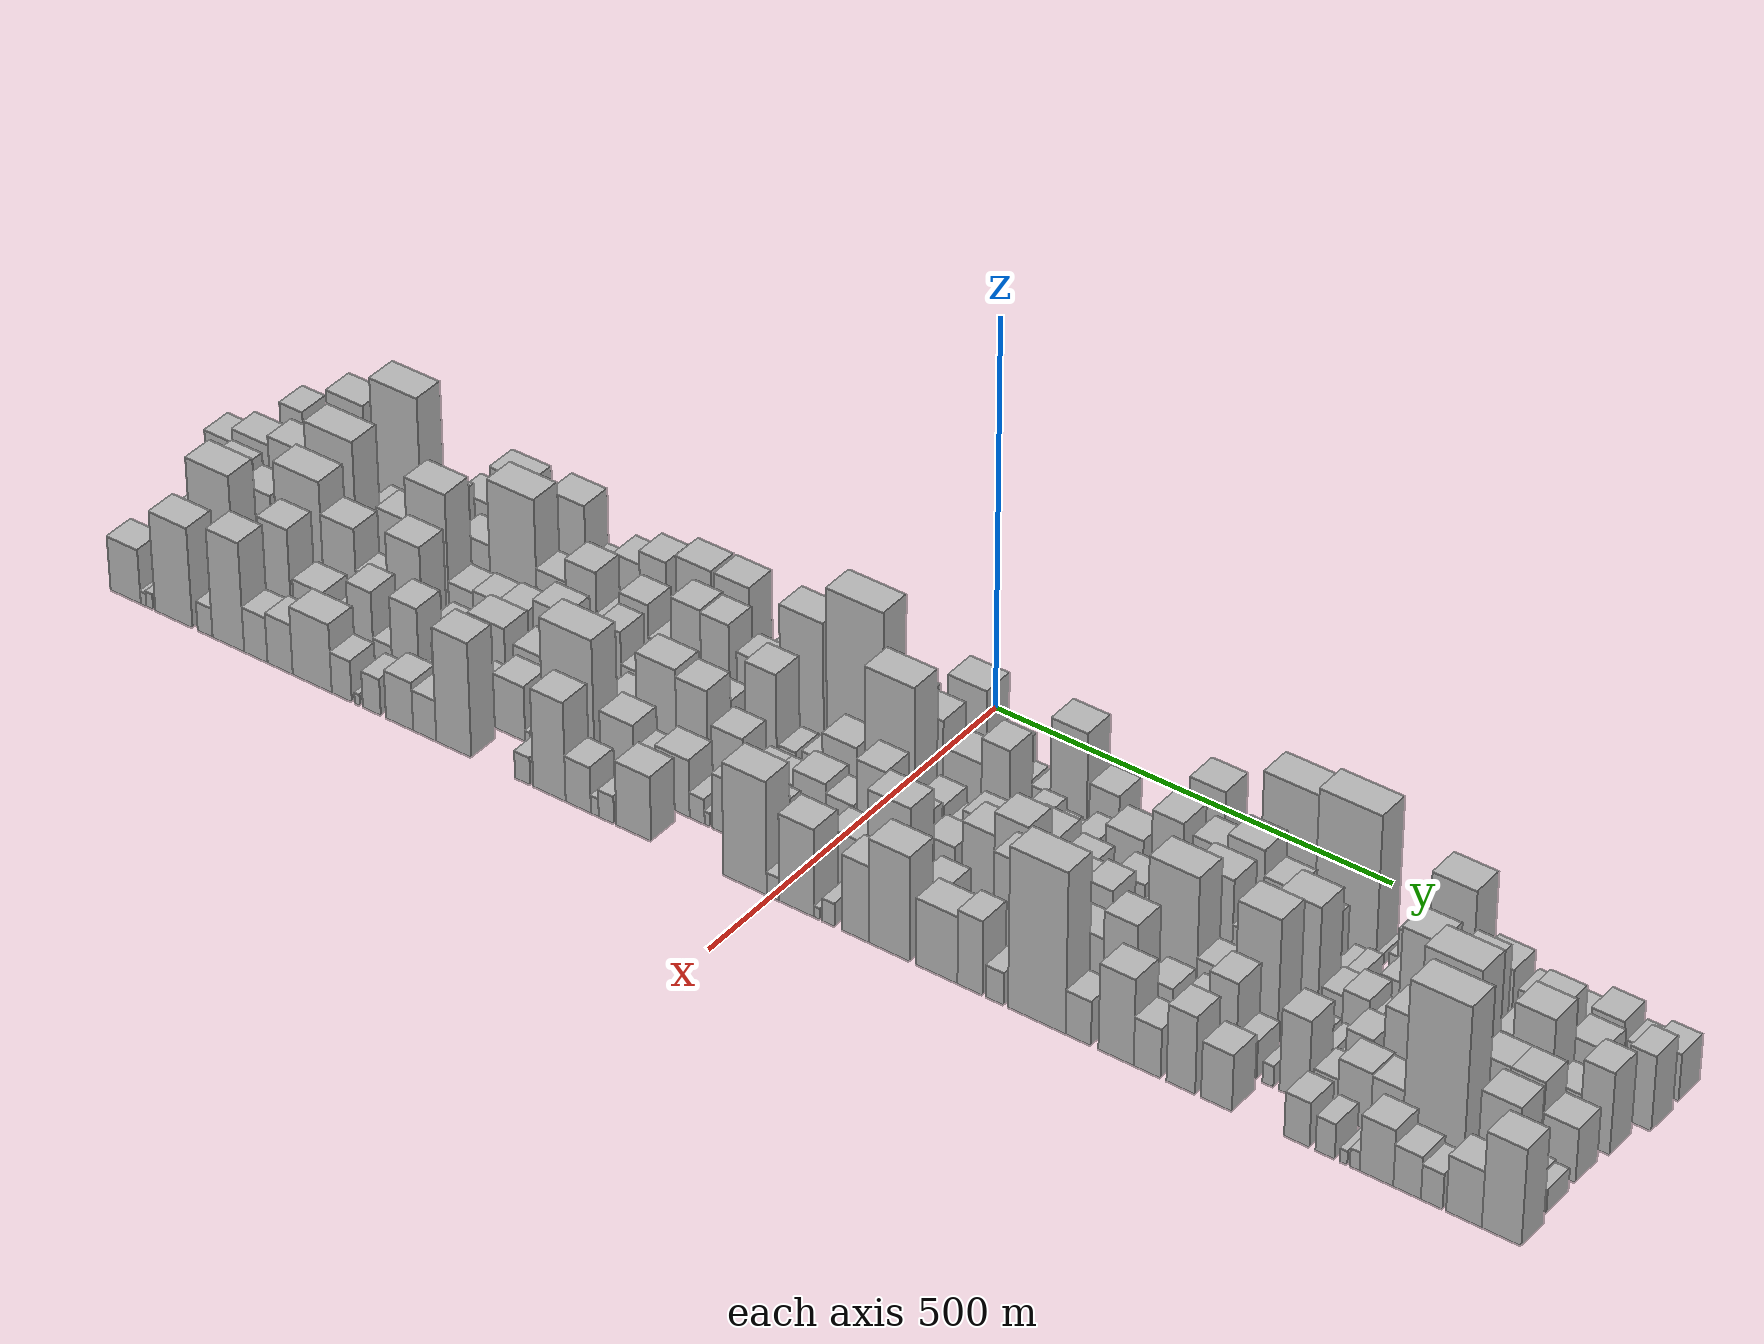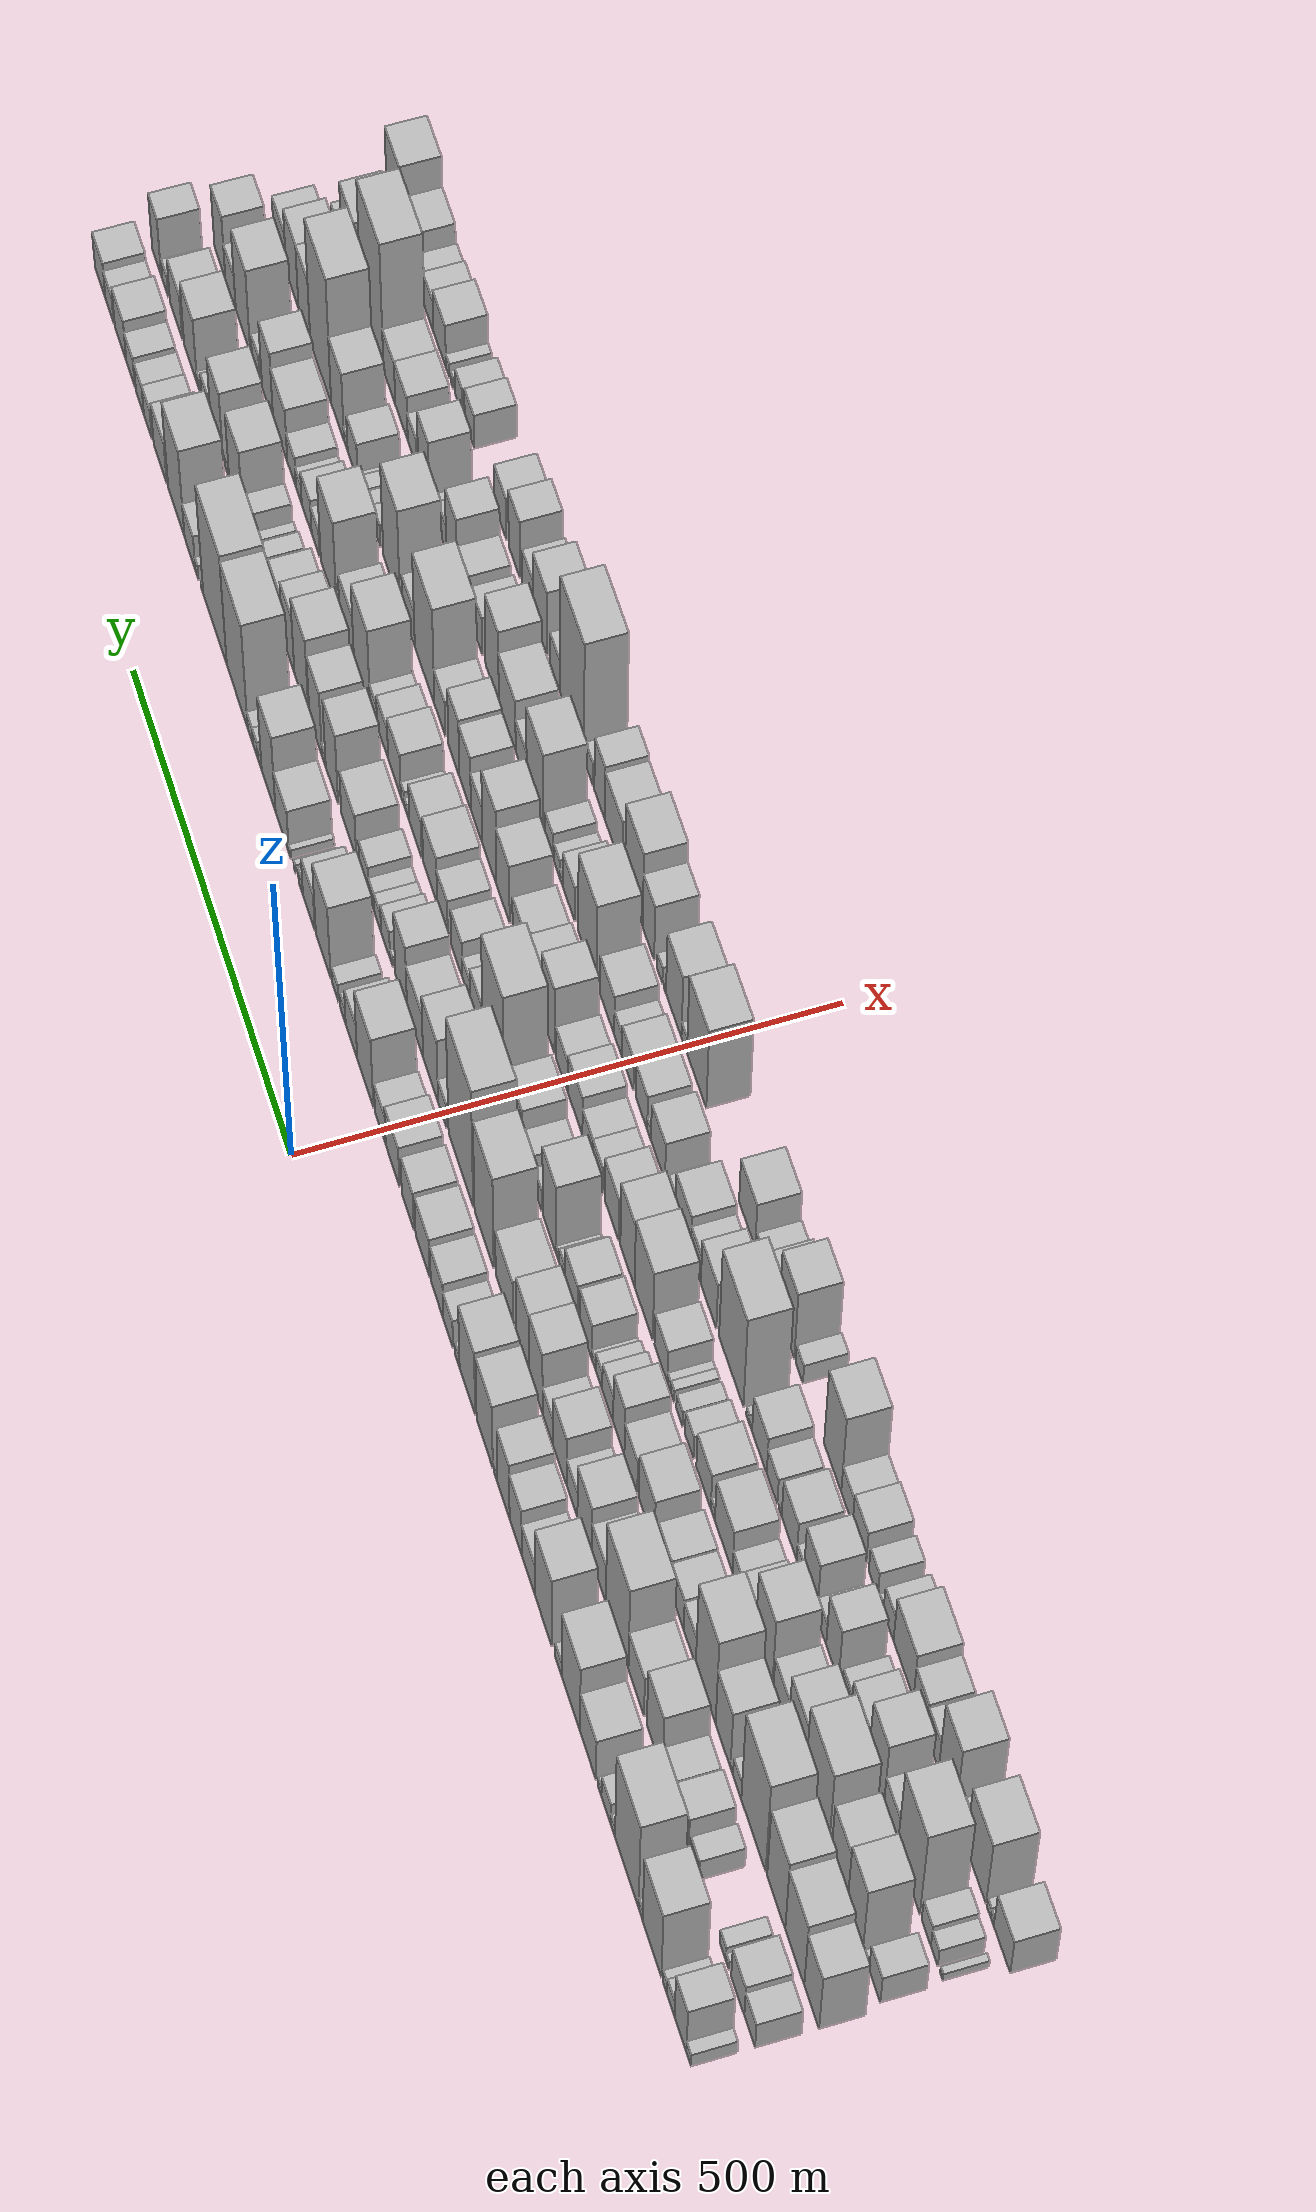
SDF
<sdf version="1.6">
 <world name="default">
  <scene>
   <sky><clouds><speed>12</speed></clouds></sky>
   <ambient>0.4 0.4 0.4 1</ambient>
   <background>0.7 0.7 0.7 1</background>
   <shadows>1</shadows>
  </scene>
  <gravity>0 0 -9.8066</gravity>
  <magnetic_field>6e-06 2.3e-05 -4.2e-05</magnetic_field>
  <physics default="0" name="default_physics" type="ode">
   <ode>
    <solver>
     <type>quick</type>
     <iters>10</iters>
     <sor>1.0</sor>
     <use_dynamic_moi_rescaling>0</use_dynamic_moi_rescaling>
    </solver>
    <constraints>
     <cfm>0</cfm>
     <erp>0.2</erp>
     <contact_max_correcting_vel>100</contact_max_correcting_vel>
     <contact_surface_layer>0.001</contact_surface_layer>
    </constraints>
   </ode>
   <max_step_size>0.004</max_step_size>
   <real_time_factor>1</real_time_factor>
   <real_time_update_rate>250</real_time_update_rate>
  </physics>
  <light name="sun" type="directional">
   <pose>0 0 10 0 0 0</pose>
   <diffuse>0.8 0.8 0.8 1</diffuse>
   <specular>0.2 0.2 0.2 1</specular>
   <attenuation>
    <range>1000</range>
    <constant>0.9</constant>
    <linear>0.01</linear>
    <quadratic>0.001</quadratic>
   </attenuation>
   <direction>-0.5 0.1 -0.9</direction>
  </light>
  <model name="building_1">
   <static>1</static>
   <pose>100.0000 -883.7648 0 0.000000 0.000000 0.000000</pose>
   <link name="link">
    <pose>0 0 13.50 0 0 0</pose>
    <collision name="collision"><geometry><box><size>40.0000 12.4704 27.0000</size></box></geometry></collision>
    <visual name="visual">
     <cast_shadows>0</cast_shadows>
     <geometry><box><size>40.0000 12.4704 27.0000</size></box></geometry>
     <material>
      <script>
       <uri>model://HANNAS_wall/materials/scripts</uri>
       <uri>model://HANNAS_wall/materials/textures</uri>
       <name>vrc/HANNAS_wall</name>
      </script>
     </material>
    </visual>
   </link>
  </model>
  <model name="building_2">
   <static>1</static>
   <pose>100.0000 -861.3541 0 0.000000 0.000000 0.000000</pose>
   <link name="link">
    <pose>0 0 48.00 0 0 0</pose>
    <collision name="collision"><geometry><box><size>40.0000 32.3509 96.0000</size></box></geometry></collision>
    <visual name="visual">
     <cast_shadows>0</cast_shadows>
     <geometry><box><size>40.0000 32.3509 96.0000</size></box></geometry>
     <material>
      <script>
       <uri>model://HANNAS_wall/materials/scripts</uri>
       <uri>model://HANNAS_wall/materials/textures</uri>
       <name>vrc/HANNAS_wall</name>
      </script>
     </material>
    </visual>
   </link>
  </model>
  <model name="building_3">
   <static>1</static>
   <pose>100.0000 -835.0464 0 0.000000 0.000000 0.000000</pose>
   <link name="link">
    <pose>0 0 18.00 0 0 0</pose>
    <collision name="collision"><geometry><box><size>40.0000 20.2645 36.0000</size></box></geometry></collision>
    <visual name="visual">
     <cast_shadows>0</cast_shadows>
     <geometry><box><size>40.0000 20.2645 36.0000</size></box></geometry>
     <material>
      <script>
       <uri>model://HANNAS_wall/materials/scripts</uri>
       <uri>model://HANNAS_wall/materials/textures</uri>
       <name>vrc/HANNAS_wall</name>
      </script>
     </material>
    </visual>
   </link>
  </model>
  <model name="building_4">
   <static>1</static>
   <pose>100.0000 -819.1044 0 0.000000 0.000000 0.000000</pose>
   <link name="link">
    <pose>0 0 13.50 0 0 0</pose>
    <collision name="collision"><geometry><box><size>40.0000 11.6194 27.0000</size></box></geometry></collision>
    <visual name="visual">
     <cast_shadows>0</cast_shadows>
     <geometry><box><size>40.0000 11.6194 27.0000</size></box></geometry>
     <material>
      <script>
       <uri>model://HANNAS_wall/materials/scripts</uri>
       <uri>model://HANNAS_wall/materials/textures</uri>
       <name>vrc/HANNAS_wall</name>
      </script>
     </material>
    </visual>
   </link>
  </model>
  <model name="building_5">
   <static>1</static>
   <pose>100.0000 -783.4198 0 0.000000 0.000000 0.000000</pose>
   <link name="link">
    <pose>0 0 70.50 0 0 0</pose>
    <collision name="collision"><geometry><box><size>40.0000 51.7498 141.0000</size></box></geometry></collision>
    <visual name="visual">
     <cast_shadows>0</cast_shadows>
     <geometry><box><size>40.0000 51.7498 141.0000</size></box></geometry>
     <material>
      <script>
       <uri>model://HANNAS_wall/materials/scripts</uri>
       <uri>model://HANNAS_wall/materials/textures</uri>
       <name>vrc/HANNAS_wall</name>
      </script>
     </material>
    </visual>
   </link>
  </model>
  <model name="building_6">
   <static>1</static>
   <pose>100.0000 -752.0764 0 0.000000 0.000000 0.000000</pose>
   <link name="link">
    <pose>0 0 12.00 0 0 0</pose>
    <collision name="collision"><geometry><box><size>40.0000 10.9372 24.0000</size></box></geometry></collision>
    <visual name="visual">
     <cast_shadows>0</cast_shadows>
     <geometry><box><size>40.0000 10.9372 24.0000</size></box></geometry>
     <material>
      <script>
       <uri>model://HANNAS_wall/materials/scripts</uri>
       <uri>model://HANNAS_wall/materials/textures</uri>
       <name>vrc/HANNAS_wall</name>
      </script>
     </material>
    </visual>
   </link>
  </model>
  <model name="building_7">
   <static>1</static>
   <pose>100.0000 -713.8888 0 0.000000 0.000000 0.000000</pose>
   <link name="link">
    <pose>0 0 91.50 0 0 0</pose>
    <collision name="collision"><geometry><box><size>40.0000 65.4380 183.0000</size></box></geometry></collision>
    <visual name="visual">
     <cast_shadows>0</cast_shadows>
     <geometry><box><size>40.0000 65.4380 183.0000</size></box></geometry>
     <material>
      <script>
       <uri>model://HANNAS_wall/materials/scripts</uri>
       <uri>model://HANNAS_wall/materials/textures</uri>
       <name>vrc/HANNAS_wall</name>
      </script>
     </material>
    </visual>
   </link>
  </model>
  <model name="building_8">
   <static>1</static>
   <pose>100.0000 -675.3168 0 0.000000 0.000000 0.000000</pose>
   <link name="link">
    <pose>0 0 12.00 0 0 0</pose>
    <collision name="collision"><geometry><box><size>40.0000 11.7061 24.0000</size></box></geometry></collision>
    <visual name="visual">
     <cast_shadows>0</cast_shadows>
     <geometry><box><size>40.0000 11.7061 24.0000</size></box></geometry>
     <material>
      <script>
       <uri>model://HANNAS_wall/materials/scripts</uri>
       <uri>model://HANNAS_wall/materials/textures</uri>
       <name>vrc/HANNAS_wall</name>
      </script>
     </material>
    </visual>
   </link>
  </model>
  <model name="building_9">
   <static>1</static>
   <pose>100.0000 -656.2395 0 0.000000 0.000000 0.000000</pose>
   <link name="link">
    <pose>0 0 22.50 0 0 0</pose>
    <collision name="collision"><geometry><box><size>40.0000 26.4486 45.0000</size></box></geometry></collision>
    <visual name="visual">
     <cast_shadows>0</cast_shadows>
     <geometry><box><size>40.0000 26.4486 45.0000</size></box></geometry>
     <material>
      <script>
       <uri>model://HANNAS_wall/materials/scripts</uri>
       <uri>model://HANNAS_wall/materials/textures</uri>
       <name>vrc/HANNAS_wall</name>
      </script>
     </material>
    </visual>
   </link>
  </model>
  <model name="building_10">
   <static>1</static>
   <pose>100.0000 -638.4105 0 0.000000 0.000000 0.000000</pose>
   <link name="link">
    <pose>0 0 10.50 0 0 0</pose>
    <collision name="collision"><geometry><box><size>40.0000 9.2094 21.0000</size></box></geometry></collision>
    <visual name="visual">
     <cast_shadows>0</cast_shadows>
     <geometry><box><size>40.0000 9.2094 21.0000</size></box></geometry>
     <material>
      <script>
       <uri>model://HANNAS_wall/materials/scripts</uri>
       <uri>model://HANNAS_wall/materials/textures</uri>
       <name>vrc/HANNAS_wall</name>
      </script>
     </material>
    </visual>
   </link>
  </model>
  <model name="building_11">
   <static>1</static>
   <pose>100.0000 -605.3665 0 0.000000 0.000000 0.000000</pose>
   <link name="link">
    <pose>0 0 42.00 0 0 0</pose>
    <collision name="collision"><geometry><box><size>40.0000 44.8785 84.0000</size></box></geometry></collision>
    <visual name="visual">
     <cast_shadows>0</cast_shadows>
     <geometry><box><size>40.0000 44.8785 84.0000</size></box></geometry>
     <material>
      <script>
       <uri>model://HANNAS_wall/materials/scripts</uri>
       <uri>model://HANNAS_wall/materials/textures</uri>
       <name>vrc/HANNAS_wall</name>
      </script>
     </material>
    </visual>
   </link>
  </model>
  <model name="building_12">
   <static>1</static>
   <pose>100.0000 -556.5885 0 0.000000 0.000000 0.000000</pose>
   <link name="link">
    <pose>0 0 67.50 0 0 0</pose>
    <collision name="collision"><geometry><box><size>40.0000 52.6775 135.0000</size></box></geometry></collision>
    <visual name="visual">
     <cast_shadows>0</cast_shadows>
     <geometry><box><size>40.0000 52.6775 135.0000</size></box></geometry>
     <material>
      <script>
       <uri>model://HANNAS_wall/materials/scripts</uri>
       <uri>model://HANNAS_wall/materials/textures</uri>
       <name>vrc/HANNAS_wall</name>
      </script>
     </material>
    </visual>
   </link>
  </model>
  <model name="building_13">
   <static>1</static>
   <pose>100.0000 -521.2551 0 0.000000 0.000000 0.000000</pose>
   <link name="link">
    <pose>0 0 15.00 0 0 0</pose>
    <collision name="collision"><geometry><box><size>40.0000 17.9893 30.0000</size></box></geometry></collision>
    <visual name="visual">
     <cast_shadows>0</cast_shadows>
     <geometry><box><size>40.0000 17.9893 30.0000</size></box></geometry>
     <material>
      <script>
       <uri>model://HANNAS_wall/materials/scripts</uri>
       <uri>model://HANNAS_wall/materials/textures</uri>
       <name>vrc/HANNAS_wall</name>
      </script>
     </material>
    </visual>
   </link>
  </model>
  <model name="building_14">
   <static>1</static>
   <pose>100.0000 -478.3073 0 0.000000 0.000000 0.000000</pose>
   <link name="link">
    <pose>0 0 69.00 0 0 0</pose>
    <collision name="collision"><geometry><box><size>40.0000 47.9061 138.0000</size></box></geometry></collision>
    <visual name="visual">
     <cast_shadows>0</cast_shadows>
     <geometry><box><size>40.0000 47.9061 138.0000</size></box></geometry>
     <material>
      <script>
       <uri>model://HANNAS_wall/materials/scripts</uri>
       <uri>model://HANNAS_wall/materials/textures</uri>
       <name>vrc/HANNAS_wall</name>
      </script>
     </material>
    </visual>
   </link>
  </model>
  <model name="building_15">
   <static>1</static>
   <pose>100.0000 -435.3478 0 0.000000 0.000000 0.000000</pose>
   <link name="link">
    <pose>0 0 33.00 0 0 0</pose>
    <collision name="collision"><geometry><box><size>40.0000 38.0129 66.0000</size></box></geometry></collision>
    <visual name="visual">
     <cast_shadows>0</cast_shadows>
     <geometry><box><size>40.0000 38.0129 66.0000</size></box></geometry>
     <material>
      <script>
       <uri>model://HANNAS_wall/materials/scripts</uri>
       <uri>model://HANNAS_wall/materials/textures</uri>
       <name>vrc/HANNAS_wall</name>
      </script>
     </material>
    </visual>
   </link>
  </model>
  <model name="building_16">
   <static>1</static>
   <pose>100.0000 -398.8219 0 0.000000 0.000000 0.000000</pose>
   <link name="link">
    <pose>0 0 46.50 0 0 0</pose>
    <collision name="collision"><geometry><box><size>40.0000 35.0389 93.0000</size></box></geometry></collision>
    <visual name="visual">
     <cast_shadows>0</cast_shadows>
     <geometry><box><size>40.0000 35.0389 93.0000</size></box></geometry>
     <material>
      <script>
       <uri>model://HANNAS_wall/materials/scripts</uri>
       <uri>model://HANNAS_wall/materials/textures</uri>
       <name>vrc/HANNAS_wall</name>
      </script>
     </material>
    </visual>
   </link>
  </model>
  <model name="building_17">
   <static>1</static>
   <pose>100.0000 -363.3621 0 0.000000 0.000000 0.000000</pose>
   <link name="link">
    <pose>0 0 55.50 0 0 0</pose>
    <collision name="collision"><geometry><box><size>40.0000 35.8806 111.0000</size></box></geometry></collision>
    <visual name="visual">
     <cast_shadows>0</cast_shadows>
     <geometry><box><size>40.0000 35.8806 111.0000</size></box></geometry>
     <material>
      <script>
       <uri>model://HANNAS_wall/materials/scripts</uri>
       <uri>model://HANNAS_wall/materials/textures</uri>
       <name>vrc/HANNAS_wall</name>
      </script>
     </material>
    </visual>
   </link>
  </model>
  <model name="building_18">
   <static>1</static>
   <pose>100.0000 -340.9097 0 0.000000 0.000000 0.000000</pose>
   <link name="link">
    <pose>0 0 10.50 0 0 0</pose>
    <collision name="collision"><geometry><box><size>40.0000 9.0240 21.0000</size></box></geometry></collision>
    <visual name="visual">
     <cast_shadows>0</cast_shadows>
     <geometry><box><size>40.0000 9.0240 21.0000</size></box></geometry>
     <material>
      <script>
       <uri>model://HANNAS_wall/materials/scripts</uri>
       <uri>model://HANNAS_wall/materials/textures</uri>
       <name>vrc/HANNAS_wall</name>
      </script>
     </material>
    </visual>
   </link>
  </model>
  <model name="building_19">
   <static>1</static>
   <pose>100.0000 -308.7457 0 0.000000 0.000000 0.000000</pose>
   <link name="link">
    <pose>0 0 63.00 0 0 0</pose>
    <collision name="collision"><geometry><box><size>40.0000 47.3039 126.0000</size></box></geometry></collision>
    <visual name="visual">
     <cast_shadows>0</cast_shadows>
     <geometry><box><size>40.0000 47.3039 126.0000</size></box></geometry>
     <material>
      <script>
       <uri>model://HANNAS_wall/materials/scripts</uri>
       <uri>model://HANNAS_wall/materials/textures</uri>
       <name>vrc/HANNAS_wall</name>
      </script>
     </material>
    </visual>
   </link>
  </model>
  <model name="building_20">
   <static>1</static>
   <pose>100.0000 -258.0588 0 0.000000 0.000000 0.000000</pose>
   <link name="link">
    <pose>0 0 63.00 0 0 0</pose>
    <collision name="collision"><geometry><box><size>40.0000 46.0698 126.0000</size></box></geometry></collision>
    <visual name="visual">
     <cast_shadows>0</cast_shadows>
     <geometry><box><size>40.0000 46.0698 126.0000</size></box></geometry>
     <material>
      <script>
       <uri>model://HANNAS_wall/materials/scripts</uri>
       <uri>model://HANNAS_wall/materials/textures</uri>
       <name>vrc/HANNAS_wall</name>
      </script>
     </material>
    </visual>
   </link>
  </model>
  <model name="building_21">
   <static>1</static>
   <pose>100.0000 -228.8627 0 0.000000 0.000000 0.000000</pose>
   <link name="link">
    <pose>0 0 13.50 0 0 0</pose>
    <collision name="collision"><geometry><box><size>40.0000 12.3224 27.0000</size></box></geometry></collision>
    <visual name="visual">
     <cast_shadows>0</cast_shadows>
     <geometry><box><size>40.0000 12.3224 27.0000</size></box></geometry>
     <material>
      <script>
       <uri>model://HANNAS_wall/materials/scripts</uri>
       <uri>model://HANNAS_wall/materials/textures</uri>
       <name>vrc/HANNAS_wall</name>
      </script>
     </material>
    </visual>
   </link>
  </model>
  <model name="building_22">
   <static>1</static>
   <pose>100.0000 -201.4027 0 0.000000 0.000000 0.000000</pose>
   <link name="link">
    <pose>0 0 27.00 0 0 0</pose>
    <collision name="collision"><geometry><box><size>40.0000 28.5976 54.0000</size></box></geometry></collision>
    <visual name="visual">
     <cast_shadows>0</cast_shadows>
     <geometry><box><size>40.0000 28.5976 54.0000</size></box></geometry>
     <material>
      <script>
       <uri>model://HANNAS_wall/materials/scripts</uri>
       <uri>model://HANNAS_wall/materials/textures</uri>
       <name>vrc/HANNAS_wall</name>
      </script>
     </material>
    </visual>
   </link>
  </model>
  <model name="building_23">
   <static>1</static>
   <pose>100.0000 -168.3326 0 0.000000 0.000000 0.000000</pose>
   <link name="link">
    <pose>0 0 34.50 0 0 0</pose>
    <collision name="collision"><geometry><box><size>40.0000 37.5425 69.0000</size></box></geometry></collision>
    <visual name="visual">
     <cast_shadows>0</cast_shadows>
     <geometry><box><size>40.0000 37.5425 69.0000</size></box></geometry>
     <material>
      <script>
       <uri>model://HANNAS_wall/materials/scripts</uri>
       <uri>model://HANNAS_wall/materials/textures</uri>
       <name>vrc/HANNAS_wall</name>
      </script>
     </material>
    </visual>
   </link>
  </model>
  <model name="building_24">
   <static>1</static>
   <pose>100.0000 -125.3732 0 0.000000 0.000000 0.000000</pose>
   <link name="link">
    <pose>0 0 37.50 0 0 0</pose>
    <collision name="collision"><geometry><box><size>40.0000 42.3763 75.0000</size></box></geometry></collision>
    <visual name="visual">
     <cast_shadows>0</cast_shadows>
     <geometry><box><size>40.0000 42.3763 75.0000</size></box></geometry>
     <material>
      <script>
       <uri>model://HANNAS_wall/materials/scripts</uri>
       <uri>model://HANNAS_wall/materials/textures</uri>
       <name>vrc/HANNAS_wall</name>
      </script>
     </material>
    </visual>
   </link>
  </model>
  <model name="building_25">
   <static>1</static>
   <pose>100.0000 -81.0485 0 0.000000 0.000000 0.000000</pose>
   <link name="link">
    <pose>0 0 36.00 0 0 0</pose>
    <collision name="collision"><geometry><box><size>40.0000 36.2731 72.0000</size></box></geometry></collision>
    <visual name="visual">
     <cast_shadows>0</cast_shadows>
     <geometry><box><size>40.0000 36.2731 72.0000</size></box></geometry>
     <material>
      <script>
       <uri>model://HANNAS_wall/materials/scripts</uri>
       <uri>model://HANNAS_wall/materials/textures</uri>
       <name>vrc/HANNAS_wall</name>
      </script>
     </material>
    </visual>
   </link>
  </model>
  <model name="building_26">
   <static>1</static>
   <pose>100.0000 -35.1441 0 0.000000 0.000000 0.000000</pose>
   <link name="link">
    <pose>0 0 37.50 0 0 0</pose>
    <collision name="collision"><geometry><box><size>40.0000 41.5357 75.0000</size></box></geometry></collision>
    <visual name="visual">
     <cast_shadows>0</cast_shadows>
     <geometry><box><size>40.0000 41.5357 75.0000</size></box></geometry>
     <material>
      <script>
       <uri>model://HANNAS_wall/materials/scripts</uri>
       <uri>model://HANNAS_wall/materials/textures</uri>
       <name>vrc/HANNAS_wall</name>
      </script>
     </material>
    </visual>
   </link>
  </model>
  <model name="building_27">
   <static>1</static>
   <pose>100.0000 1.9660 0 0.000000 0.000000 0.000000</pose>
   <link name="link">
    <pose>0 0 28.50 0 0 0</pose>
    <collision name="collision"><geometry><box><size>40.0000 32.6845 57.0000</size></box></geometry></collision>
    <visual name="visual">
     <cast_shadows>0</cast_shadows>
     <geometry><box><size>40.0000 32.6845 57.0000</size></box></geometry>
     <material>
      <script>
       <uri>model://HANNAS_wall/materials/scripts</uri>
       <uri>model://HANNAS_wall/materials/textures</uri>
       <name>vrc/HANNAS_wall</name>
      </script>
     </material>
    </visual>
   </link>
  </model>
  <model name="building_28">
   <static>1</static>
   <pose>100.0000 47.9363 0 0.000000 0.000000 0.000000</pose>
   <link name="link">
    <pose>0 0 64.50 0 0 0</pose>
    <collision name="collision"><geometry><box><size>40.0000 49.2560 129.0000</size></box></geometry></collision>
    <visual name="visual">
     <cast_shadows>0</cast_shadows>
     <geometry><box><size>40.0000 49.2560 129.0000</size></box></geometry>
     <material>
      <script>
       <uri>model://HANNAS_wall/materials/scripts</uri>
       <uri>model://HANNAS_wall/materials/textures</uri>
       <name>vrc/HANNAS_wall</name>
      </script>
     </material>
    </visual>
   </link>
  </model>
  <model name="building_29">
   <static>1</static>
   <pose>100.0000 90.3240 0 0.000000 0.000000 0.000000</pose>
   <link name="link">
    <pose>0 0 33.00 0 0 0</pose>
    <collision name="collision"><geometry><box><size>40.0000 35.5196 66.0000</size></box></geometry></collision>
    <visual name="visual">
     <cast_shadows>0</cast_shadows>
     <geometry><box><size>40.0000 35.5196 66.0000</size></box></geometry>
     <material>
      <script>
       <uri>model://HANNAS_wall/materials/scripts</uri>
       <uri>model://HANNAS_wall/materials/textures</uri>
       <name>vrc/HANNAS_wall</name>
      </script>
     </material>
    </visual>
   </link>
  </model>
  <model name="building_30">
   <static>1</static>
   <pose>100.0000 116.0856 0 0.000000 0.000000 0.000000</pose>
   <link name="link">
    <pose>0 0 15.00 0 0 0</pose>
    <collision name="collision"><geometry><box><size>40.0000 16.0036 30.0000</size></box></geometry></collision>
    <visual name="visual">
     <cast_shadows>0</cast_shadows>
     <geometry><box><size>40.0000 16.0036 30.0000</size></box></geometry>
     <material>
      <script>
       <uri>model://HANNAS_wall/materials/scripts</uri>
       <uri>model://HANNAS_wall/materials/textures</uri>
       <name>vrc/HANNAS_wall</name>
      </script>
     </material>
    </visual>
   </link>
  </model>
  <model name="building_31">
   <static>1</static>
   <pose>100.0000 139.5563 0 0.000000 0.000000 0.000000</pose>
   <link name="link">
    <pose>0 0 16.50 0 0 0</pose>
    <collision name="collision"><geometry><box><size>40.0000 18.9379 33.0000</size></box></geometry></collision>
    <visual name="visual">
     <cast_shadows>0</cast_shadows>
     <geometry><box><size>40.0000 18.9379 33.0000</size></box></geometry>
     <material>
      <script>
       <uri>model://HANNAS_wall/materials/scripts</uri>
       <uri>model://HANNAS_wall/materials/textures</uri>
       <name>vrc/HANNAS_wall</name>
      </script>
     </material>
    </visual>
   </link>
  </model>
  <model name="building_32">
   <static>1</static>
   <pose>100.0000 177.0604 0 0.000000 0.000000 0.000000</pose>
   <link name="link">
    <pose>0 0 66.00 0 0 0</pose>
    <collision name="collision"><geometry><box><size>40.0000 46.0703 132.0000</size></box></geometry></collision>
    <visual name="visual">
     <cast_shadows>0</cast_shadows>
     <geometry><box><size>40.0000 46.0703 132.0000</size></box></geometry>
     <material>
      <script>
       <uri>model://HANNAS_wall/materials/scripts</uri>
       <uri>model://HANNAS_wall/materials/textures</uri>
       <name>vrc/HANNAS_wall</name>
      </script>
     </material>
    </visual>
   </link>
  </model>
  <model name="building_33">
   <static>1</static>
   <pose>100.0000 221.8283 0 0.000000 0.000000 0.000000</pose>
   <link name="link">
    <pose>0 0 34.50 0 0 0</pose>
    <collision name="collision"><geometry><box><size>40.0000 37.4654 69.0000</size></box></geometry></collision>
    <visual name="visual">
     <cast_shadows>0</cast_shadows>
     <geometry><box><size>40.0000 37.4654 69.0000</size></box></geometry>
     <material>
      <script>
       <uri>model://HANNAS_wall/materials/scripts</uri>
       <uri>model://HANNAS_wall/materials/textures</uri>
       <name>vrc/HANNAS_wall</name>
      </script>
     </material>
    </visual>
   </link>
  </model>
  <model name="building_34">
   <static>1</static>
   <pose>100.0000 247.1931 0 0.000000 0.000000 0.000000</pose>
   <link name="link">
    <pose>0 0 13.50 0 0 0</pose>
    <collision name="collision"><geometry><box><size>40.0000 13.2643 27.0000</size></box></geometry></collision>
    <visual name="visual">
     <cast_shadows>0</cast_shadows>
     <geometry><box><size>40.0000 13.2643 27.0000</size></box></geometry>
     <material>
      <script>
       <uri>model://HANNAS_wall/materials/scripts</uri>
       <uri>model://HANNAS_wall/materials/textures</uri>
       <name>vrc/HANNAS_wall</name>
      </script>
     </material>
    </visual>
   </link>
  </model>
  <model name="building_35">
   <static>1</static>
   <pose>100.0000 265.9821 0 0.000000 0.000000 0.000000</pose>
   <link name="link">
    <pose>0 0 7.50 0 0 0</pose>
    <collision name="collision"><geometry><box><size>40.0000 6.3138 15.0000</size></box></geometry></collision>
    <visual name="visual">
     <cast_shadows>0</cast_shadows>
     <geometry><box><size>40.0000 6.3138 15.0000</size></box></geometry>
     <material>
      <script>
       <uri>model://HANNAS_wall/materials/scripts</uri>
       <uri>model://HANNAS_wall/materials/textures</uri>
       <name>vrc/HANNAS_wall</name>
      </script>
     </material>
    </visual>
   </link>
  </model>
  <model name="building_36">
   <static>1</static>
   <pose>100.0000 281.3648 0 0.000000 0.000000 0.000000</pose>
   <link name="link">
    <pose>0 0 7.50 0 0 0</pose>
    <collision name="collision"><geometry><box><size>40.0000 6.4515 15.0000</size></box></geometry></collision>
    <visual name="visual">
     <cast_shadows>0</cast_shadows>
     <geometry><box><size>40.0000 6.4515 15.0000</size></box></geometry>
     <material>
      <script>
       <uri>model://HANNAS_wall/materials/scripts</uri>
       <uri>model://HANNAS_wall/materials/textures</uri>
       <name>vrc/HANNAS_wall</name>
      </script>
     </material>
    </visual>
   </link>
  </model>
  <model name="building_37">
   <static>1</static>
   <pose>100.0000 305.4700 0 0.000000 0.000000 0.000000</pose>
   <link name="link">
    <pose>0 0 37.50 0 0 0</pose>
    <collision name="collision"><geometry><box><size>40.0000 41.7590 75.0000</size></box></geometry></collision>
    <visual name="visual">
     <cast_shadows>0</cast_shadows>
     <geometry><box><size>40.0000 41.7590 75.0000</size></box></geometry>
     <material>
      <script>
       <uri>model://HANNAS_wall/materials/scripts</uri>
       <uri>model://HANNAS_wall/materials/textures</uri>
       <name>vrc/HANNAS_wall</name>
      </script>
     </material>
    </visual>
   </link>
  </model>
  <model name="building_38">
   <static>1</static>
   <pose>100.0000 348.3477 0 0.000000 0.000000 0.000000</pose>
   <link name="link">
    <pose>0 0 67.50 0 0 0</pose>
    <collision name="collision"><geometry><box><size>40.0000 43.9964 135.0000</size></box></geometry></collision>
    <visual name="visual">
     <cast_shadows>0</cast_shadows>
     <geometry><box><size>40.0000 43.9964 135.0000</size></box></geometry>
     <material>
      <script>
       <uri>model://HANNAS_wall/materials/scripts</uri>
       <uri>model://HANNAS_wall/materials/textures</uri>
       <name>vrc/HANNAS_wall</name>
      </script>
     </material>
    </visual>
   </link>
  </model>
  <model name="building_39">
   <static>1</static>
   <pose>100.0000 376.3401 0 0.000000 0.000000 0.000000</pose>
   <link name="link">
    <pose>0 0 13.50 0 0 0</pose>
    <collision name="collision"><geometry><box><size>40.0000 11.9885 27.0000</size></box></geometry></collision>
    <visual name="visual">
     <cast_shadows>0</cast_shadows>
     <geometry><box><size>40.0000 11.9885 27.0000</size></box></geometry>
     <material>
      <script>
       <uri>model://HANNAS_wall/materials/scripts</uri>
       <uri>model://HANNAS_wall/materials/textures</uri>
       <name>vrc/HANNAS_wall</name>
      </script>
     </material>
    </visual>
   </link>
  </model>
  <model name="building_40">
   <static>1</static>
   <pose>100.0000 390.2218 0 0.000000 0.000000 0.000000</pose>
   <link name="link">
    <pose>0 0 15.00 0 0 0</pose>
    <collision name="collision"><geometry><box><size>40.0000 15.7749 30.0000</size></box></geometry></collision>
    <visual name="visual">
     <cast_shadows>0</cast_shadows>
     <geometry><box><size>40.0000 15.7749 30.0000</size></box></geometry>
     <material>
      <script>
       <uri>model://HANNAS_wall/materials/scripts</uri>
       <uri>model://HANNAS_wall/materials/textures</uri>
       <name>vrc/HANNAS_wall</name>
      </script>
     </material>
    </visual>
   </link>
  </model>
  <model name="building_41">
   <static>1</static>
   <pose>100.0000 406.5665 0 0.000000 0.000000 0.000000</pose>
   <link name="link">
    <pose>0 0 15.00 0 0 0</pose>
    <collision name="collision"><geometry><box><size>40.0000 16.9144 30.0000</size></box></geometry></collision>
    <visual name="visual">
     <cast_shadows>0</cast_shadows>
     <geometry><box><size>40.0000 16.9144 30.0000</size></box></geometry>
     <material>
      <script>
       <uri>model://HANNAS_wall/materials/scripts</uri>
       <uri>model://HANNAS_wall/materials/textures</uri>
       <name>vrc/HANNAS_wall</name>
      </script>
     </material>
    </visual>
   </link>
  </model>
  <model name="building_42">
   <static>1</static>
   <pose>100.0000 448.3828 0 0.000000 0.000000 0.000000</pose>
   <link name="link">
    <pose>0 0 91.50 0 0 0</pose>
    <collision name="collision"><geometry><box><size>40.0000 66.7181 183.0000</size></box></geometry></collision>
    <visual name="visual">
     <cast_shadows>0</cast_shadows>
     <geometry><box><size>40.0000 66.7181 183.0000</size></box></geometry>
     <material>
      <script>
       <uri>model://HANNAS_wall/materials/scripts</uri>
       <uri>model://HANNAS_wall/materials/textures</uri>
       <name>vrc/HANNAS_wall</name>
      </script>
     </material>
    </visual>
   </link>
  </model>
  <model name="building_43">
   <static>1</static>
   <pose>100.0000 519.7299 0 0.000000 0.000000 0.000000</pose>
   <link name="link">
    <pose>0 0 96.00 0 0 0</pose>
    <collision name="collision"><geometry><box><size>40.0000 75.9759 192.0000</size></box></geometry></collision>
    <visual name="visual">
     <cast_shadows>0</cast_shadows>
     <geometry><box><size>40.0000 75.9759 192.0000</size></box></geometry>
     <material>
      <script>
       <uri>model://HANNAS_wall/materials/scripts</uri>
       <uri>model://HANNAS_wall/materials/textures</uri>
       <name>vrc/HANNAS_wall</name>
      </script>
     </material>
    </visual>
   </link>
  </model>
  <model name="building_44">
   <static>1</static>
   <pose>100.0000 560.9932 0 0.000000 0.000000 0.000000</pose>
   <link name="link">
    <pose>0 0 7.50 0 0 0</pose>
    <collision name="collision"><geometry><box><size>40.0000 6.5508 15.0000</size></box></geometry></collision>
    <visual name="visual">
     <cast_shadows>0</cast_shadows>
     <geometry><box><size>40.0000 6.5508 15.0000</size></box></geometry>
     <material>
      <script>
       <uri>model://HANNAS_wall/materials/scripts</uri>
       <uri>model://HANNAS_wall/materials/textures</uri>
       <name>vrc/HANNAS_wall</name>
      </script>
     </material>
    </visual>
   </link>
  </model>
  <model name="building_45">
   <static>1</static>
   <pose>100.0000 578.1978 0 0.000000 0.000000 0.000000</pose>
   <link name="link">
    <pose>0 0 12.00 0 0 0</pose>
    <collision name="collision"><geometry><box><size>40.0000 9.8584 24.0000</size></box></geometry></collision>
    <visual name="visual">
     <cast_shadows>0</cast_shadows>
     <geometry><box><size>40.0000 9.8584 24.0000</size></box></geometry>
     <material>
      <script>
       <uri>model://HANNAS_wall/materials/scripts</uri>
       <uri>model://HANNAS_wall/materials/textures</uri>
       <name>vrc/HANNAS_wall</name>
      </script>
     </material>
    </visual>
   </link>
  </model>
  <model name="building_46">
   <static>1</static>
   <pose>100.0000 600.8912 0 0.000000 0.000000 0.000000</pose>
   <link name="link">
    <pose>0 0 30.00 0 0 0</pose>
    <collision name="collision"><geometry><box><size>40.0000 35.5284 60.0000</size></box></geometry></collision>
    <visual name="visual">
     <cast_shadows>0</cast_shadows>
     <geometry><box><size>40.0000 35.5284 60.0000</size></box></geometry>
     <material>
      <script>
       <uri>model://HANNAS_wall/materials/scripts</uri>
       <uri>model://HANNAS_wall/materials/textures</uri>
       <name>vrc/HANNAS_wall</name>
      </script>
     </material>
    </visual>
   </link>
  </model>
  <model name="building_47">
   <static>1</static>
   <pose>100.0000 645.2896 0 0.000000 0.000000 0.000000</pose>
   <link name="link">
    <pose>0 0 75.00 0 0 0</pose>
    <collision name="collision"><geometry><box><size>40.0000 53.2685 150.0000</size></box></geometry></collision>
    <visual name="visual">
     <cast_shadows>0</cast_shadows>
     <geometry><box><size>40.0000 53.2685 150.0000</size></box></geometry>
     <material>
      <script>
       <uri>model://HANNAS_wall/materials/scripts</uri>
       <uri>model://HANNAS_wall/materials/textures</uri>
       <name>vrc/HANNAS_wall</name>
      </script>
     </material>
    </visual>
   </link>
  </model>
  <model name="building_48">
   <static>1</static>
   <pose>100.0000 698.4418 0 0.000000 0.000000 0.000000</pose>
   <link name="link">
    <pose>0 0 36.00 0 0 0</pose>
    <collision name="collision"><geometry><box><size>40.0000 43.0359 72.0000</size></box></geometry></collision>
    <visual name="visual">
     <cast_shadows>0</cast_shadows>
     <geometry><box><size>40.0000 43.0359 72.0000</size></box></geometry>
     <material>
      <script>
       <uri>model://HANNAS_wall/materials/scripts</uri>
       <uri>model://HANNAS_wall/materials/textures</uri>
       <name>vrc/HANNAS_wall</name>
      </script>
     </material>
    </visual>
   </link>
  </model>
  <model name="building_49">
   <static>1</static>
   <pose>100.0000 739.4240 0 0.000000 0.000000 0.000000</pose>
   <link name="link">
    <pose>0 0 25.50 0 0 0</pose>
    <collision name="collision"><geometry><box><size>40.0000 26.9285 51.0000</size></box></geometry></collision>
    <visual name="visual">
     <cast_shadows>0</cast_shadows>
     <geometry><box><size>40.0000 26.9285 51.0000</size></box></geometry>
     <material>
      <script>
       <uri>model://HANNAS_wall/materials/scripts</uri>
       <uri>model://HANNAS_wall/materials/textures</uri>
       <name>vrc/HANNAS_wall</name>
      </script>
     </material>
    </visual>
   </link>
  </model>
  <model name="building_50">
   <static>1</static>
   <pose>100.0000 766.0559 0 0.000000 0.000000 0.000000</pose>
   <link name="link">
    <pose>0 0 24.00 0 0 0</pose>
    <collision name="collision"><geometry><box><size>40.0000 26.3352 48.0000</size></box></geometry></collision>
    <visual name="visual">
     <cast_shadows>0</cast_shadows>
     <geometry><box><size>40.0000 26.3352 48.0000</size></box></geometry>
     <material>
      <script>
       <uri>model://HANNAS_wall/materials/scripts</uri>
       <uri>model://HANNAS_wall/materials/textures</uri>
       <name>vrc/HANNAS_wall</name>
      </script>
     </material>
    </visual>
   </link>
  </model>
  <model name="building_51">
   <static>1</static>
   <pose>100.0000 796.5793 0 0.000000 0.000000 0.000000</pose>
   <link name="link">
    <pose>0 0 25.50 0 0 0</pose>
    <collision name="collision"><geometry><box><size>40.0000 28.7116 51.0000</size></box></geometry></collision>
    <visual name="visual">
     <cast_shadows>0</cast_shadows>
     <geometry><box><size>40.0000 28.7116 51.0000</size></box></geometry>
     <material>
      <script>
       <uri>model://HANNAS_wall/materials/scripts</uri>
       <uri>model://HANNAS_wall/materials/textures</uri>
       <name>vrc/HANNAS_wall</name>
      </script>
     </material>
    </visual>
   </link>
  </model>
  <model name="building_52">
   <static>1</static>
   <pose>100.0000 830.1415 0 0.000000 0.000000 0.000000</pose>
   <link name="link">
    <pose>0 0 34.50 0 0 0</pose>
    <collision name="collision"><geometry><box><size>40.0000 38.4129 69.0000</size></box></geometry></collision>
    <visual name="visual">
     <cast_shadows>0</cast_shadows>
     <geometry><box><size>40.0000 38.4129 69.0000</size></box></geometry>
     <material>
      <script>
       <uri>model://HANNAS_wall/materials/scripts</uri>
       <uri>model://HANNAS_wall/materials/textures</uri>
       <name>vrc/HANNAS_wall</name>
      </script>
     </material>
    </visual>
   </link>
  </model>
  <model name="building_53">
   <static>1</static>
   <pose>100.0000 867.1216 0 0.000000 0.000000 0.000000</pose>
   <link name="link">
    <pose>0 0 24.00 0 0 0</pose>
    <collision name="collision"><geometry><box><size>40.0000 27.5473 48.0000</size></box></geometry></collision>
    <visual name="visual">
     <cast_shadows>0</cast_shadows>
     <geometry><box><size>40.0000 27.5473 48.0000</size></box></geometry>
     <material>
      <script>
       <uri>model://HANNAS_wall/materials/scripts</uri>
       <uri>model://HANNAS_wall/materials/textures</uri>
       <name>vrc/HANNAS_wall</name>
      </script>
     </material>
    </visual>
   </link>
  </model>
  <model name="building_54">
   <static>1</static>
   <pose>100.0000 898.6010 0 0.000000 0.000000 0.000000</pose>
   <link name="link">
    <pose>0 0 30.00 0 0 0</pose>
    <collision name="collision"><geometry><box><size>40.0000 35.4115 60.0000</size></box></geometry></collision>
    <visual name="visual">
     <cast_shadows>0</cast_shadows>
     <geometry><box><size>40.0000 35.4115 60.0000</size></box></geometry>
     <material>
      <script>
       <uri>model://HANNAS_wall/materials/scripts</uri>
       <uri>model://HANNAS_wall/materials/textures</uri>
       <name>vrc/HANNAS_wall</name>
      </script>
     </material>
    </visual>
   </link>
  </model>
  <model name="building_55">
   <static>1</static>
   <pose>155.0000 -875.5173 0 0.000000 0.000000 0.000000</pose>
   <link name="link">
    <pose>0 0 27.00 0 0 0</pose>
    <collision name="collision"><geometry><box><size>40.0000 28.9655 54.0000</size></box></geometry></collision>
    <visual name="visual">
     <cast_shadows>0</cast_shadows>
     <geometry><box><size>40.0000 28.9655 54.0000</size></box></geometry>
     <material>
      <script>
       <uri>model://HANNAS_wall/materials/scripts</uri>
       <uri>model://HANNAS_wall/materials/textures</uri>
       <name>vrc/HANNAS_wall</name>
      </script>
     </material>
    </visual>
   </link>
  </model>
  <model name="building_56">
   <static>1</static>
   <pose>155.0000 -843.3119 0 0.000000 0.000000 0.000000</pose>
   <link name="link">
    <pose>0 0 33.00 0 0 0</pose>
    <collision name="collision"><geometry><box><size>40.0000 35.4452 66.0000</size></box></geometry></collision>
    <visual name="visual">
     <cast_shadows>0</cast_shadows>
     <geometry><box><size>40.0000 35.4452 66.0000</size></box></geometry>
     <material>
      <script>
       <uri>model://HANNAS_wall/materials/scripts</uri>
       <uri>model://HANNAS_wall/materials/textures</uri>
       <name>vrc/HANNAS_wall</name>
      </script>
     </material>
    </visual>
   </link>
  </model>
  <model name="building_57">
   <static>1</static>
   <pose>155.0000 -815.4259 0 0.000000 0.000000 0.000000</pose>
   <link name="link">
    <pose>0 0 9.00 0 0 0</pose>
    <collision name="collision"><geometry><box><size>40.0000 8.3268 18.0000</size></box></geometry></collision>
    <visual name="visual">
     <cast_shadows>0</cast_shadows>
     <geometry><box><size>40.0000 8.3268 18.0000</size></box></geometry>
     <material>
      <script>
       <uri>model://HANNAS_wall/materials/scripts</uri>
       <uri>model://HANNAS_wall/materials/textures</uri>
       <name>vrc/HANNAS_wall</name>
      </script>
     </material>
    </visual>
   </link>
  </model>
  <model name="building_58">
   <static>1</static>
   <pose>155.0000 -802.9785 0 0.000000 0.000000 0.000000</pose>
   <link name="link">
    <pose>0 0 15.00 0 0 0</pose>
    <collision name="collision"><geometry><box><size>40.0000 16.5681 30.0000</size></box></geometry></collision>
    <visual name="visual">
     <cast_shadows>0</cast_shadows>
     <geometry><box><size>40.0000 16.5681 30.0000</size></box></geometry>
     <material>
      <script>
       <uri>model://HANNAS_wall/materials/scripts</uri>
       <uri>model://HANNAS_wall/materials/textures</uri>
       <name>vrc/HANNAS_wall</name>
      </script>
     </material>
    </visual>
   </link>
  </model>
  <model name="building_59">
   <static>1</static>
   <pose>155.0000 -725.8095 0 0.000000 0.000000 0.000000</pose>
   <link name="link">
    <pose>0 0 21.00 0 0 0</pose>
    <collision name="collision"><geometry><box><size>40.0000 23.2567 42.0000</size></box></geometry></collision>
    <visual name="visual">
     <cast_shadows>0</cast_shadows>
     <geometry><box><size>40.0000 23.2567 42.0000</size></box></geometry>
     <material>
      <script>
       <uri>model://HANNAS_wall/materials/scripts</uri>
       <uri>model://HANNAS_wall/materials/textures</uri>
       <name>vrc/HANNAS_wall</name>
      </script>
     </material>
    </visual>
   </link>
  </model>
  <model name="building_60">
   <static>1</static>
   <pose>155.0000 -691.6443 0 0.000000 0.000000 0.000000</pose>
   <link name="link">
    <pose>0 0 33.00 0 0 0</pose>
    <collision name="collision"><geometry><box><size>40.0000 35.0736 66.0000</size></box></geometry></collision>
    <visual name="visual">
     <cast_shadows>0</cast_shadows>
     <geometry><box><size>40.0000 35.0736 66.0000</size></box></geometry>
     <material>
      <script>
       <uri>model://HANNAS_wall/materials/scripts</uri>
       <uri>model://HANNAS_wall/materials/textures</uri>
       <name>vrc/HANNAS_wall</name>
      </script>
     </material>
    </visual>
   </link>
  </model>
  <model name="building_61">
   <static>1</static>
   <pose>155.0000 -653.0417 0 0.000000 0.000000 0.000000</pose>
   <link name="link">
    <pose>0 0 27.00 0 0 0</pose>
    <collision name="collision"><geometry><box><size>40.0000 32.1316 54.0000</size></box></geometry></collision>
    <visual name="visual">
     <cast_shadows>0</cast_shadows>
     <geometry><box><size>40.0000 32.1316 54.0000</size></box></geometry>
     <material>
      <script>
       <uri>model://HANNAS_wall/materials/scripts</uri>
       <uri>model://HANNAS_wall/materials/textures</uri>
       <name>vrc/HANNAS_wall</name>
      </script>
     </material>
    </visual>
   </link>
  </model>
  <model name="building_62">
   <static>1</static>
   <pose>155.0000 -615.1147 0 0.000000 0.000000 0.000000</pose>
   <link name="link">
    <pose>0 0 58.50 0 0 0</pose>
    <collision name="collision"><geometry><box><size>40.0000 43.7225 117.0000</size></box></geometry></collision>
    <visual name="visual">
     <cast_shadows>0</cast_shadows>
     <geometry><box><size>40.0000 43.7225 117.0000</size></box></geometry>
     <material>
      <script>
       <uri>model://HANNAS_wall/materials/scripts</uri>
       <uri>model://HANNAS_wall/materials/textures</uri>
       <name>vrc/HANNAS_wall</name>
      </script>
     </material>
    </visual>
   </link>
  </model>
  <model name="building_63">
   <static>1</static>
   <pose>155.0000 -563.4851 0 0.000000 0.000000 0.000000</pose>
   <link name="link">
    <pose>0 0 40.50 0 0 0</pose>
    <collision name="collision"><geometry><box><size>40.0000 43.5367 81.0000</size></box></geometry></collision>
    <visual name="visual">
     <cast_shadows>0</cast_shadows>
     <geometry><box><size>40.0000 43.5367 81.0000</size></box></geometry>
     <material>
      <script>
       <uri>model://HANNAS_wall/materials/scripts</uri>
       <uri>model://HANNAS_wall/materials/textures</uri>
       <name>vrc/HANNAS_wall</name>
      </script>
     </material>
    </visual>
   </link>
  </model>
  <model name="building_64">
   <static>1</static>
   <pose>155.0000 -509.9571 0 0.000000 0.000000 0.000000</pose>
   <link name="link">
    <pose>0 0 84.00 0 0 0</pose>
    <collision name="collision"><geometry><box><size>40.0000 63.5192 168.0000</size></box></geometry></collision>
    <visual name="visual">
     <cast_shadows>0</cast_shadows>
     <geometry><box><size>40.0000 63.5192 168.0000</size></box></geometry>
     <material>
      <script>
       <uri>model://HANNAS_wall/materials/scripts</uri>
       <uri>model://HANNAS_wall/materials/textures</uri>
       <name>vrc/HANNAS_wall</name>
      </script>
     </material>
    </visual>
   </link>
  </model>
  <model name="building_65">
   <static>1</static>
   <pose>155.0000 -458.1483 0 0.000000 0.000000 0.000000</pose>
   <link name="link">
    <pose>0 0 39.00 0 0 0</pose>
    <collision name="collision"><geometry><box><size>40.0000 40.0985 78.0000</size></box></geometry></collision>
    <visual name="visual">
     <cast_shadows>0</cast_shadows>
     <geometry><box><size>40.0000 40.0985 78.0000</size></box></geometry>
     <material>
      <script>
       <uri>model://HANNAS_wall/materials/scripts</uri>
       <uri>model://HANNAS_wall/materials/textures</uri>
       <name>vrc/HANNAS_wall</name>
      </script>
     </material>
    </visual>
   </link>
  </model>
  <model name="building_66">
   <static>1</static>
   <pose>155.0000 -417.5650 0 0.000000 0.000000 0.000000</pose>
   <link name="link">
    <pose>0 0 54.00 0 0 0</pose>
    <collision name="collision"><geometry><box><size>40.0000 41.0680 108.0000</size></box></geometry></collision>
    <visual name="visual">
     <cast_shadows>0</cast_shadows>
     <geometry><box><size>40.0000 41.0680 108.0000</size></box></geometry>
     <material>
      <script>
       <uri>model://HANNAS_wall/materials/scripts</uri>
       <uri>model://HANNAS_wall/materials/textures</uri>
       <name>vrc/HANNAS_wall</name>
      </script>
     </material>
    </visual>
   </link>
  </model>
  <model name="building_67">
   <static>1</static>
   <pose>155.0000 -381.4643 0 0.000000 0.000000 0.000000</pose>
   <link name="link">
    <pose>0 0 27.00 0 0 0</pose>
    <collision name="collision"><geometry><box><size>40.0000 31.1333 54.0000</size></box></geometry></collision>
    <visual name="visual">
     <cast_shadows>0</cast_shadows>
     <geometry><box><size>40.0000 31.1333 54.0000</size></box></geometry>
     <material>
      <script>
       <uri>model://HANNAS_wall/materials/scripts</uri>
       <uri>model://HANNAS_wall/materials/textures</uri>
       <name>vrc/HANNAS_wall</name>
      </script>
     </material>
    </visual>
   </link>
  </model>
  <model name="building_68">
   <static>1</static>
   <pose>155.0000 -346.7210 0 0.000000 0.000000 0.000000</pose>
   <link name="link">
    <pose>0 0 48.00 0 0 0</pose>
    <collision name="collision"><geometry><box><size>40.0000 38.3533 96.0000</size></box></geometry></collision>
    <visual name="visual">
     <cast_shadows>0</cast_shadows>
     <geometry><box><size>40.0000 38.3533 96.0000</size></box></geometry>
     <material>
      <script>
       <uri>model://HANNAS_wall/materials/scripts</uri>
       <uri>model://HANNAS_wall/materials/textures</uri>
       <name>vrc/HANNAS_wall</name>
      </script>
     </material>
    </visual>
   </link>
  </model>
  <model name="building_69">
   <static>1</static>
   <pose>155.0000 -312.1057 0 0.000000 0.000000 0.000000</pose>
   <link name="link">
    <pose>0 0 27.00 0 0 0</pose>
    <collision name="collision"><geometry><box><size>40.0000 30.8774 54.0000</size></box></geometry></collision>
    <visual name="visual">
     <cast_shadows>0</cast_shadows>
     <geometry><box><size>40.0000 30.8774 54.0000</size></box></geometry>
     <material>
      <script>
       <uri>model://HANNAS_wall/materials/scripts</uri>
       <uri>model://HANNAS_wall/materials/textures</uri>
       <name>vrc/HANNAS_wall</name>
      </script>
     </material>
    </visual>
   </link>
  </model>
  <model name="building_70">
   <static>1</static>
   <pose>155.0000 -277.3150 0 0.000000 0.000000 0.000000</pose>
   <link name="link">
    <pose>0 0 60.00 0 0 0</pose>
    <collision name="collision"><geometry><box><size>40.0000 38.7040 120.0000</size></box></geometry></collision>
    <visual name="visual">
     <cast_shadows>0</cast_shadows>
     <geometry><box><size>40.0000 38.7040 120.0000</size></box></geometry>
     <material>
      <script>
       <uri>model://HANNAS_wall/materials/scripts</uri>
       <uri>model://HANNAS_wall/materials/textures</uri>
       <name>vrc/HANNAS_wall</name>
      </script>
     </material>
    </visual>
   </link>
  </model>
  <model name="building_71">
   <static>1</static>
   <pose>155.0000 -239.2753 0 0.000000 0.000000 0.000000</pose>
   <link name="link">
    <pose>0 0 58.50 0 0 0</pose>
    <collision name="collision"><geometry><box><size>40.0000 37.3753 117.0000</size></box></geometry></collision>
    <visual name="visual">
     <cast_shadows>0</cast_shadows>
     <geometry><box><size>40.0000 37.3753 117.0000</size></box></geometry>
     <material>
      <script>
       <uri>model://HANNAS_wall/materials/scripts</uri>
       <uri>model://HANNAS_wall/materials/textures</uri>
       <name>vrc/HANNAS_wall</name>
      </script>
     </material>
    </visual>
   </link>
  </model>
  <model name="building_72">
   <static>1</static>
   <pose>155.0000 -185.1789 0 0.000000 0.000000 0.000000</pose>
   <link name="link">
    <pose>0 0 43.50 0 0 0</pose>
    <collision name="collision"><geometry><box><size>40.0000 50.8176 87.0000</size></box></geometry></collision>
    <visual name="visual">
     <cast_shadows>0</cast_shadows>
     <geometry><box><size>40.0000 50.8176 87.0000</size></box></geometry>
     <material>
      <script>
       <uri>model://HANNAS_wall/materials/scripts</uri>
       <uri>model://HANNAS_wall/materials/textures</uri>
       <name>vrc/HANNAS_wall</name>
      </script>
     </material>
    </visual>
   </link>
  </model>
  <model name="building_73">
   <static>1</static>
   <pose>155.0000 -125.4176 0 0.000000 0.000000 0.000000</pose>
   <link name="link">
    <pose>0 0 87.00 0 0 0</pose>
    <collision name="collision"><geometry><box><size>40.0000 56.7050 174.0000</size></box></geometry></collision>
    <visual name="visual">
     <cast_shadows>0</cast_shadows>
     <geometry><box><size>40.0000 56.7050 174.0000</size></box></geometry>
     <material>
      <script>
       <uri>model://HANNAS_wall/materials/scripts</uri>
       <uri>model://HANNAS_wall/materials/textures</uri>
       <name>vrc/HANNAS_wall</name>
      </script>
     </material>
    </visual>
   </link>
  </model>
  <model name="building_74">
   <static>1</static>
   <pose>155.0000 -56.3924 0 0.000000 0.000000 0.000000</pose>
   <link name="link">
    <pose>0 0 111.00 0 0 0</pose>
    <collision name="collision"><geometry><box><size>40.0000 73.3453 222.0000</size></box></geometry></collision>
    <visual name="visual">
     <cast_shadows>0</cast_shadows>
     <geometry><box><size>40.0000 73.3453 222.0000</size></box></geometry>
     <material>
      <script>
       <uri>model://HANNAS_wall/materials/scripts</uri>
       <uri>model://HANNAS_wall/materials/textures</uri>
       <name>vrc/HANNAS_wall</name>
      </script>
     </material>
    </visual>
   </link>
  </model>
  <model name="building_75">
   <static>1</static>
   <pose>155.0000 -0.9667 0 0.000000 0.000000 0.000000</pose>
   <link name="link">
    <pose>0 0 22.50 0 0 0</pose>
    <collision name="collision"><geometry><box><size>40.0000 25.5061 45.0000</size></box></geometry></collision>
    <visual name="visual">
     <cast_shadows>0</cast_shadows>
     <geometry><box><size>40.0000 25.5061 45.0000</size></box></geometry>
     <material>
      <script>
       <uri>model://HANNAS_wall/materials/scripts</uri>
       <uri>model://HANNAS_wall/materials/textures</uri>
       <name>vrc/HANNAS_wall</name>
      </script>
     </material>
    </visual>
   </link>
  </model>
  <model name="building_76">
   <static>1</static>
   <pose>155.0000 34.3568 0 0.000000 0.000000 0.000000</pose>
   <link name="link">
    <pose>0 0 58.50 0 0 0</pose>
    <collision name="collision"><geometry><box><size>40.0000 45.1409 117.0000</size></box></geometry></collision>
    <visual name="visual">
     <cast_shadows>0</cast_shadows>
     <geometry><box><size>40.0000 45.1409 117.0000</size></box></geometry>
     <material>
      <script>
       <uri>model://HANNAS_wall/materials/scripts</uri>
       <uri>model://HANNAS_wall/materials/textures</uri>
       <name>vrc/HANNAS_wall</name>
      </script>
     </material>
    </visual>
   </link>
  </model>
  <model name="building_77">
   <static>1</static>
   <pose>155.0000 81.2284 0 0.000000 0.000000 0.000000</pose>
   <link name="link">
    <pose>0 0 42.00 0 0 0</pose>
    <collision name="collision"><geometry><box><size>40.0000 48.6025 84.0000</size></box></geometry></collision>
    <visual name="visual">
     <cast_shadows>0</cast_shadows>
     <geometry><box><size>40.0000 48.6025 84.0000</size></box></geometry>
     <material>
      <script>
       <uri>model://HANNAS_wall/materials/scripts</uri>
       <uri>model://HANNAS_wall/materials/textures</uri>
       <name>vrc/HANNAS_wall</name>
      </script>
     </material>
    </visual>
   </link>
  </model>
  <model name="building_78">
   <static>1</static>
   <pose>155.0000 123.5292 0 0.000000 0.000000 0.000000</pose>
   <link name="link">
    <pose>0 0 58.50 0 0 0</pose>
    <collision name="collision"><geometry><box><size>40.0000 35.9991 117.0000</size></box></geometry></collision>
    <visual name="visual">
     <cast_shadows>0</cast_shadows>
     <geometry><box><size>40.0000 35.9991 117.0000</size></box></geometry>
     <material>
      <script>
       <uri>model://HANNAS_wall/materials/scripts</uri>
       <uri>model://HANNAS_wall/materials/textures</uri>
       <name>vrc/HANNAS_wall</name>
      </script>
     </material>
    </visual>
   </link>
  </model>
  <model name="building_79">
   <static>1</static>
   <pose>155.0000 153.4789 0 0.000000 0.000000 0.000000</pose>
   <link name="link">
    <pose>0 0 9.00 0 0 0</pose>
    <collision name="collision"><geometry><box><size>40.0000 7.9003 18.0000</size></box></geometry></collision>
    <visual name="visual">
     <cast_shadows>0</cast_shadows>
     <geometry><box><size>40.0000 7.9003 18.0000</size></box></geometry>
     <material>
      <script>
       <uri>model://HANNAS_wall/materials/scripts</uri>
       <uri>model://HANNAS_wall/materials/textures</uri>
       <name>vrc/HANNAS_wall</name>
      </script>
     </material>
    </visual>
   </link>
  </model>
  <model name="building_80">
   <static>1</static>
   <pose>155.0000 171.3089 0 0.000000 0.000000 0.000000</pose>
   <link name="link">
    <pose>0 0 25.50 0 0 0</pose>
    <collision name="collision"><geometry><box><size>40.0000 27.7598 51.0000</size></box></geometry></collision>
    <visual name="visual">
     <cast_shadows>0</cast_shadows>
     <geometry><box><size>40.0000 27.7598 51.0000</size></box></geometry>
     <material>
      <script>
       <uri>model://HANNAS_wall/materials/scripts</uri>
       <uri>model://HANNAS_wall/materials/textures</uri>
       <name>vrc/HANNAS_wall</name>
      </script>
     </material>
    </visual>
   </link>
  </model>
  <model name="building_81">
   <static>1</static>
   <pose>155.0000 195.3613 0 0.000000 0.000000 0.000000</pose>
   <link name="link">
    <pose>0 0 18.00 0 0 0</pose>
    <collision name="collision"><geometry><box><size>40.0000 20.3450 36.0000</size></box></geometry></collision>
    <visual name="visual">
     <cast_shadows>0</cast_shadows>
     <geometry><box><size>40.0000 20.3450 36.0000</size></box></geometry>
     <material>
      <script>
       <uri>model://HANNAS_wall/materials/scripts</uri>
       <uri>model://HANNAS_wall/materials/textures</uri>
       <name>vrc/HANNAS_wall</name>
      </script>
     </material>
    </visual>
   </link>
  </model>
  <model name="building_82">
   <static>1</static>
   <pose>155.0000 214.4098 0 0.000000 0.000000 0.000000</pose>
   <link name="link">
    <pose>0 0 16.50 0 0 0</pose>
    <collision name="collision"><geometry><box><size>40.0000 17.7520 33.0000</size></box></geometry></collision>
    <visual name="visual">
     <cast_shadows>0</cast_shadows>
     <geometry><box><size>40.0000 17.7520 33.0000</size></box></geometry>
     <material>
      <script>
       <uri>model://HANNAS_wall/materials/scripts</uri>
       <uri>model://HANNAS_wall/materials/textures</uri>
       <name>vrc/HANNAS_wall</name>
      </script>
     </material>
    </visual>
   </link>
  </model>
  <model name="building_83">
   <static>1</static>
   <pose>155.0000 237.5512 0 0.000000 0.000000 0.000000</pose>
   <link name="link">
    <pose>0 0 25.50 0 0 0</pose>
    <collision name="collision"><geometry><box><size>40.0000 28.5307 51.0000</size></box></geometry></collision>
    <visual name="visual">
     <cast_shadows>0</cast_shadows>
     <geometry><box><size>40.0000 28.5307 51.0000</size></box></geometry>
     <material>
      <script>
       <uri>model://HANNAS_wall/materials/scripts</uri>
       <uri>model://HANNAS_wall/materials/textures</uri>
       <name>vrc/HANNAS_wall</name>
      </script>
     </material>
    </visual>
   </link>
  </model>
  <model name="building_84">
   <static>1</static>
   <pose>155.0000 285.0950 0 0.000000 0.000000 0.000000</pose>
   <link name="link">
    <pose>0 0 39.00 0 0 0</pose>
    <collision name="collision"><geometry><box><size>40.0000 46.5569 78.0000</size></box></geometry></collision>
    <visual name="visual">
     <cast_shadows>0</cast_shadows>
     <geometry><box><size>40.0000 46.5569 78.0000</size></box></geometry>
     <material>
      <script>
       <uri>model://HANNAS_wall/materials/scripts</uri>
       <uri>model://HANNAS_wall/materials/textures</uri>
       <name>vrc/HANNAS_wall</name>
      </script>
     </material>
    </visual>
   </link>
  </model>
  <model name="building_85">
   <static>1</static>
   <pose>155.0000 337.7202 0 0.000000 0.000000 0.000000</pose>
   <link name="link">
    <pose>0 0 61.50 0 0 0</pose>
    <collision name="collision"><geometry><box><size>40.0000 38.6936 123.0000</size></box></geometry></collision>
    <visual name="visual">
     <cast_shadows>0</cast_shadows>
     <geometry><box><size>40.0000 38.6936 123.0000</size></box></geometry>
     <material>
      <script>
       <uri>model://HANNAS_wall/materials/scripts</uri>
       <uri>model://HANNAS_wall/materials/textures</uri>
       <name>vrc/HANNAS_wall</name>
      </script>
     </material>
    </visual>
   </link>
  </model>
  <model name="building_86">
   <static>1</static>
   <pose>155.0000 362.7837 0 0.000000 0.000000 0.000000</pose>
   <link name="link">
    <pose>0 0 12.00 0 0 0</pose>
    <collision name="collision"><geometry><box><size>40.0000 11.4334 24.0000</size></box></geometry></collision>
    <visual name="visual">
     <cast_shadows>0</cast_shadows>
     <geometry><box><size>40.0000 11.4334 24.0000</size></box></geometry>
     <material>
      <script>
       <uri>model://HANNAS_wall/materials/scripts</uri>
       <uri>model://HANNAS_wall/materials/textures</uri>
       <name>vrc/HANNAS_wall</name>
      </script>
     </material>
    </visual>
   </link>
  </model>
  <model name="building_87">
   <static>1</static>
   <pose>155.0000 388.0872 0 0.000000 0.000000 0.000000</pose>
   <link name="link">
    <pose>0 0 57.00 0 0 0</pose>
    <collision name="collision"><geometry><box><size>40.0000 39.1735 114.0000</size></box></geometry></collision>
    <visual name="visual">
     <cast_shadows>0</cast_shadows>
     <geometry><box><size>40.0000 39.1735 114.0000</size></box></geometry>
     <material>
      <script>
       <uri>model://HANNAS_wall/materials/scripts</uri>
       <uri>model://HANNAS_wall/materials/textures</uri>
       <name>vrc/HANNAS_wall</name>
      </script>
     </material>
    </visual>
   </link>
  </model>
  <model name="building_88">
   <static>1</static>
   <pose>155.0000 433.1110 0 0.000000 0.000000 0.000000</pose>
   <link name="link">
    <pose>0 0 67.50 0 0 0</pose>
    <collision name="collision"><geometry><box><size>40.0000 44.8740 135.0000</size></box></geometry></collision>
    <visual name="visual">
     <cast_shadows>0</cast_shadows>
     <geometry><box><size>40.0000 44.8740 135.0000</size></box></geometry>
     <material>
      <script>
       <uri>model://HANNAS_wall/materials/scripts</uri>
       <uri>model://HANNAS_wall/materials/textures</uri>
       <name>vrc/HANNAS_wall</name>
      </script>
     </material>
    </visual>
   </link>
  </model>
  <model name="building_89">
   <static>1</static>
   <pose>155.0000 474.1898 0 0.000000 0.000000 0.000000</pose>
   <link name="link">
    <pose>0 0 51.00 0 0 0</pose>
    <collision name="collision"><geometry><box><size>40.0000 37.2837 102.0000</size></box></geometry></collision>
    <visual name="visual">
     <cast_shadows>0</cast_shadows>
     <geometry><box><size>40.0000 37.2837 102.0000</size></box></geometry>
     <material>
      <script>
       <uri>model://HANNAS_wall/materials/scripts</uri>
       <uri>model://HANNAS_wall/materials/textures</uri>
       <name>vrc/HANNAS_wall</name>
      </script>
     </material>
    </visual>
   </link>
  </model>
  <model name="building_90">
   <static>1</static>
   <pose>155.0000 512.9101 0 0.000000 0.000000 0.000000</pose>
   <link name="link">
    <pose>0 0 37.50 0 0 0</pose>
    <collision name="collision"><geometry><box><size>40.0000 40.1569 75.0000</size></box></geometry></collision>
    <visual name="visual">
     <cast_shadows>0</cast_shadows>
     <geometry><box><size>40.0000 40.1569 75.0000</size></box></geometry>
     <material>
      <script>
       <uri>model://HANNAS_wall/materials/scripts</uri>
       <uri>model://HANNAS_wall/materials/textures</uri>
       <name>vrc/HANNAS_wall</name>
      </script>
     </material>
    </visual>
   </link>
  </model>
  <model name="building_91">
   <static>1</static>
   <pose>155.0000 550.0552 0 0.000000 0.000000 0.000000</pose>
   <link name="link">
    <pose>0 0 15.00 0 0 0</pose>
    <collision name="collision"><geometry><box><size>40.0000 16.1334 30.0000</size></box></geometry></collision>
    <visual name="visual">
     <cast_shadows>0</cast_shadows>
     <geometry><box><size>40.0000 16.1334 30.0000</size></box></geometry>
     <material>
      <script>
       <uri>model://HANNAS_wall/materials/scripts</uri>
       <uri>model://HANNAS_wall/materials/textures</uri>
       <name>vrc/HANNAS_wall</name>
      </script>
     </material>
    </visual>
   </link>
  </model>
  <model name="building_92">
   <static>1</static>
   <pose>155.0000 567.1289 0 0.000000 0.000000 0.000000</pose>
   <link name="link">
    <pose>0 0 16.50 0 0 0</pose>
    <collision name="collision"><geometry><box><size>40.0000 18.0139 33.0000</size></box></geometry></collision>
    <visual name="visual">
     <cast_shadows>0</cast_shadows>
     <geometry><box><size>40.0000 18.0139 33.0000</size></box></geometry>
     <material>
      <script>
       <uri>model://HANNAS_wall/materials/scripts</uri>
       <uri>model://HANNAS_wall/materials/textures</uri>
       <name>vrc/HANNAS_wall</name>
      </script>
     </material>
    </visual>
   </link>
  </model>
  <model name="building_93">
   <static>1</static>
   <pose>155.0000 589.1931 0 0.000000 0.000000 0.000000</pose>
   <link name="link">
    <pose>0 0 10.50 0 0 0</pose>
    <collision name="collision"><geometry><box><size>40.0000 10.1146 21.0000</size></box></geometry></collision>
    <visual name="visual">
     <cast_shadows>0</cast_shadows>
     <geometry><box><size>40.0000 10.1146 21.0000</size></box></geometry>
     <material>
      <script>
       <uri>model://HANNAS_wall/materials/scripts</uri>
       <uri>model://HANNAS_wall/materials/textures</uri>
       <name>vrc/HANNAS_wall</name>
      </script>
     </material>
    </visual>
   </link>
  </model>
  <model name="building_94">
   <static>1</static>
   <pose>155.0000 609.5684 0 0.000000 0.000000 0.000000</pose>
   <link name="link">
    <pose>0 0 22.50 0 0 0</pose>
    <collision name="collision"><geometry><box><size>40.0000 22.6360 45.0000</size></box></geometry></collision>
    <visual name="visual">
     <cast_shadows>0</cast_shadows>
     <geometry><box><size>40.0000 22.6360 45.0000</size></box></geometry>
     <material>
      <script>
       <uri>model://HANNAS_wall/materials/scripts</uri>
       <uri>model://HANNAS_wall/materials/textures</uri>
       <name>vrc/HANNAS_wall</name>
      </script>
     </material>
    </visual>
   </link>
  </model>
  <model name="building_95">
   <static>1</static>
   <pose>155.0000 643.2905 0 0.000000 0.000000 0.000000</pose>
   <link name="link">
    <pose>0 0 58.50 0 0 0</pose>
    <collision name="collision"><geometry><box><size>40.0000 44.8080 117.0000</size></box></geometry></collision>
    <visual name="visual">
     <cast_shadows>0</cast_shadows>
     <geometry><box><size>40.0000 44.8080 117.0000</size></box></geometry>
     <material>
      <script>
       <uri>model://HANNAS_wall/materials/scripts</uri>
       <uri>model://HANNAS_wall/materials/textures</uri>
       <name>vrc/HANNAS_wall</name>
      </script>
     </material>
    </visual>
   </link>
  </model>
  <model name="building_96">
   <static>1</static>
   <pose>155.0000 671.6743 0 0.000000 0.000000 0.000000</pose>
   <link name="link">
    <pose>0 0 13.50 0 0 0</pose>
    <collision name="collision"><geometry><box><size>40.0000 11.9597 27.0000</size></box></geometry></collision>
    <visual name="visual">
     <cast_shadows>0</cast_shadows>
     <geometry><box><size>40.0000 11.9597 27.0000</size></box></geometry>
     <material>
      <script>
       <uri>model://HANNAS_wall/materials/scripts</uri>
       <uri>model://HANNAS_wall/materials/textures</uri>
       <name>vrc/HANNAS_wall</name>
      </script>
     </material>
    </visual>
   </link>
  </model>
  <model name="building_97">
   <static>1</static>
   <pose>155.0000 704.5367 0 0.000000 0.000000 0.000000</pose>
   <link name="link">
    <pose>0 0 58.50 0 0 0</pose>
    <collision name="collision"><geometry><box><size>40.0000 39.7651 117.0000</size></box></geometry></collision>
    <visual name="visual">
     <cast_shadows>0</cast_shadows>
     <geometry><box><size>40.0000 39.7651 117.0000</size></box></geometry>
     <material>
      <script>
       <uri>model://HANNAS_wall/materials/scripts</uri>
       <uri>model://HANNAS_wall/materials/textures</uri>
       <name>vrc/HANNAS_wall</name>
      </script>
     </material>
    </visual>
   </link>
  </model>
  <model name="building_98">
   <static>1</static>
   <pose>155.0000 743.6605 0 0.000000 0.000000 0.000000</pose>
   <link name="link">
    <pose>0 0 21.00 0 0 0</pose>
    <collision name="collision"><geometry><box><size>40.0000 22.4826 42.0000</size></box></geometry></collision>
    <visual name="visual">
     <cast_shadows>0</cast_shadows>
     <geometry><box><size>40.0000 22.4826 42.0000</size></box></geometry>
     <material>
      <script>
       <uri>model://HANNAS_wall/materials/scripts</uri>
       <uri>model://HANNAS_wall/materials/textures</uri>
       <name>vrc/HANNAS_wall</name>
      </script>
     </material>
    </visual>
   </link>
  </model>
  <model name="building_99">
   <static>1</static>
   <pose>155.0000 765.6775 0 0.000000 0.000000 0.000000</pose>
   <link name="link">
    <pose>0 0 10.50 0 0 0</pose>
    <collision name="collision"><geometry><box><size>40.0000 9.5513 21.0000</size></box></geometry></collision>
    <visual name="visual">
     <cast_shadows>0</cast_shadows>
     <geometry><box><size>40.0000 9.5513 21.0000</size></box></geometry>
     <material>
      <script>
       <uri>model://HANNAS_wall/materials/scripts</uri>
       <uri>model://HANNAS_wall/materials/textures</uri>
       <name>vrc/HANNAS_wall</name>
      </script>
     </material>
    </visual>
   </link>
  </model>
  <model name="building_100">
   <static>1</static>
   <pose>155.0000 791.6637 0 0.000000 0.000000 0.000000</pose>
   <link name="link">
    <pose>0 0 54.00 0 0 0</pose>
    <collision name="collision"><geometry><box><size>40.0000 42.4212 108.0000</size></box></geometry></collision>
    <visual name="visual">
     <cast_shadows>0</cast_shadows>
     <geometry><box><size>40.0000 42.4212 108.0000</size></box></geometry>
     <material>
      <script>
       <uri>model://HANNAS_wall/materials/scripts</uri>
       <uri>model://HANNAS_wall/materials/textures</uri>
       <name>vrc/HANNAS_wall</name>
      </script>
     </material>
    </visual>
   </link>
  </model>
  <model name="building_101">
   <static>1</static>
   <pose>155.0000 839.4511 0 0.000000 0.000000 0.000000</pose>
   <link name="link">
    <pose>0 0 37.50 0 0 0</pose>
    <collision name="collision"><geometry><box><size>40.0000 41.1534 75.0000</size></box></geometry></collision>
    <visual name="visual">
     <cast_shadows>0</cast_shadows>
     <geometry><box><size>40.0000 41.1534 75.0000</size></box></geometry>
     <material>
      <script>
       <uri>model://HANNAS_wall/materials/scripts</uri>
       <uri>model://HANNAS_wall/materials/textures</uri>
       <name>vrc/HANNAS_wall</name>
      </script>
     </material>
    </visual>
   </link>
  </model>
  <model name="building_102">
   <static>1</static>
   <pose>155.0000 875.5806 0 0.000000 0.000000 0.000000</pose>
   <link name="link">
    <pose>0 0 18.00 0 0 0</pose>
    <collision name="collision"><geometry><box><size>40.0000 19.1056 36.0000</size></box></geometry></collision>
    <visual name="visual">
     <cast_shadows>0</cast_shadows>
     <geometry><box><size>40.0000 19.1056 36.0000</size></box></geometry>
     <material>
      <script>
       <uri>model://HANNAS_wall/materials/scripts</uri>
       <uri>model://HANNAS_wall/materials/textures</uri>
       <name>vrc/HANNAS_wall</name>
      </script>
     </material>
    </visual>
   </link>
  </model>
  <model name="building_103">
   <static>1</static>
   <pose>155.0000 903.9660 0 0.000000 0.000000 0.000000</pose>
   <link name="link">
    <pose>0 0 48.00 0 0 0</pose>
    <collision name="collision"><geometry><box><size>40.0000 29.6651 96.0000</size></box></geometry></collision>
    <visual name="visual">
     <cast_shadows>0</cast_shadows>
     <geometry><box><size>40.0000 29.6651 96.0000</size></box></geometry>
     <material>
      <script>
       <uri>model://HANNAS_wall/materials/scripts</uri>
       <uri>model://HANNAS_wall/materials/textures</uri>
       <name>vrc/HANNAS_wall</name>
      </script>
     </material>
    </visual>
   </link>
  </model>
  <model name="building_104">
   <static>1</static>
   <pose>210.0000 -870.1935 0 0.000000 0.000000 0.000000</pose>
   <link name="link">
    <pose>0 0 58.50 0 0 0</pose>
    <collision name="collision"><geometry><box><size>40.0000 39.6129 117.0000</size></box></geometry></collision>
    <visual name="visual">
     <cast_shadows>0</cast_shadows>
     <geometry><box><size>40.0000 39.6129 117.0000</size></box></geometry>
     <material>
      <script>
       <uri>model://HANNAS_wall/materials/scripts</uri>
       <uri>model://HANNAS_wall/materials/textures</uri>
       <name>vrc/HANNAS_wall</name>
      </script>
     </material>
    </visual>
   </link>
  </model>
  <model name="building_105">
   <static>1</static>
   <pose>210.0000 -824.9096 0 0.000000 0.000000 0.000000</pose>
   <link name="link">
    <pose>0 0 67.50 0 0 0</pose>
    <collision name="collision"><geometry><box><size>40.0000 50.9550 135.0000</size></box></geometry></collision>
    <visual name="visual">
     <cast_shadows>0</cast_shadows>
     <geometry><box><size>40.0000 50.9550 135.0000</size></box></geometry>
     <material>
      <script>
       <uri>model://HANNAS_wall/materials/scripts</uri>
       <uri>model://HANNAS_wall/materials/textures</uri>
       <name>vrc/HANNAS_wall</name>
      </script>
     </material>
    </visual>
   </link>
  </model>
  <model name="building_106">
   <static>1</static>
   <pose>210.0000 -774.9024 0 0.000000 0.000000 0.000000</pose>
   <link name="link">
    <pose>0 0 73.50 0 0 0</pose>
    <collision name="collision"><geometry><box><size>40.0000 49.0593 147.0000</size></box></geometry></collision>
    <visual name="visual">
     <cast_shadows>0</cast_shadows>
     <geometry><box><size>40.0000 49.0593 147.0000</size></box></geometry>
     <material>
      <script>
       <uri>model://HANNAS_wall/materials/scripts</uri>
       <uri>model://HANNAS_wall/materials/textures</uri>
       <name>vrc/HANNAS_wall</name>
      </script>
     </material>
    </visual>
   </link>
  </model>
  <model name="building_107">
   <static>1</static>
   <pose>210.0000 -713.2337 0 0.000000 0.000000 0.000000</pose>
   <link name="link">
    <pose>0 0 94.50 0 0 0</pose>
    <collision name="collision"><geometry><box><size>40.0000 66.2782 189.0000</size></box></geometry></collision>
    <visual name="visual">
     <cast_shadows>0</cast_shadows>
     <geometry><box><size>40.0000 66.2782 189.0000</size></box></geometry>
     <material>
      <script>
       <uri>model://HANNAS_wall/materials/scripts</uri>
       <uri>model://HANNAS_wall/materials/textures</uri>
       <name>vrc/HANNAS_wall</name>
      </script>
     </material>
    </visual>
   </link>
  </model>
  <model name="building_108">
   <static>1</static>
   <pose>210.0000 -668.7282 0 0.000000 0.000000 0.000000</pose>
   <link name="link">
    <pose>0 0 19.50 0 0 0</pose>
    <collision name="collision"><geometry><box><size>40.0000 22.7329 39.0000</size></box></geometry></collision>
    <visual name="visual">
     <cast_shadows>0</cast_shadows>
     <geometry><box><size>40.0000 22.7329 39.0000</size></box></geometry>
     <material>
      <script>
       <uri>model://HANNAS_wall/materials/scripts</uri>
       <uri>model://HANNAS_wall/materials/textures</uri>
       <name>vrc/HANNAS_wall</name>
      </script>
     </material>
    </visual>
   </link>
  </model>
  <model name="building_109">
   <static>1</static>
   <pose>210.0000 -653.8431 0 0.000000 0.000000 0.000000</pose>
   <link name="link">
    <pose>0 0 7.50 0 0 0</pose>
    <collision name="collision"><geometry><box><size>40.0000 7.0373 15.0000</size></box></geometry></collision>
    <visual name="visual">
     <cast_shadows>0</cast_shadows>
     <geometry><box><size>40.0000 7.0373 15.0000</size></box></geometry>
     <material>
      <script>
       <uri>model://HANNAS_wall/materials/scripts</uri>
       <uri>model://HANNAS_wall/materials/textures</uri>
       <name>vrc/HANNAS_wall</name>
      </script>
     </material>
    </visual>
   </link>
  </model>
  <model name="building_110">
   <static>1</static>
   <pose>210.0000 -629.8048 0 0.000000 0.000000 0.000000</pose>
   <link name="link">
    <pose>0 0 58.50 0 0 0</pose>
    <collision name="collision"><geometry><box><size>40.0000 41.0392 117.0000</size></box></geometry></collision>
    <visual name="visual">
     <cast_shadows>0</cast_shadows>
     <geometry><box><size>40.0000 41.0392 117.0000</size></box></geometry>
     <material>
      <script>
       <uri>model://HANNAS_wall/materials/scripts</uri>
       <uri>model://HANNAS_wall/materials/textures</uri>
       <name>vrc/HANNAS_wall</name>
      </script>
     </material>
    </visual>
   </link>
  </model>
  <model name="building_111">
   <static>1</static>
   <pose>210.0000 -581.8648 0 0.000000 0.000000 0.000000</pose>
   <link name="link">
    <pose>0 0 87.00 0 0 0</pose>
    <collision name="collision"><geometry><box><size>40.0000 54.8408 174.0000</size></box></geometry></collision>
    <visual name="visual">
     <cast_shadows>0</cast_shadows>
     <geometry><box><size>40.0000 54.8408 174.0000</size></box></geometry>
     <material>
      <script>
       <uri>model://HANNAS_wall/materials/scripts</uri>
       <uri>model://HANNAS_wall/materials/textures</uri>
       <name>vrc/HANNAS_wall</name>
      </script>
     </material>
    </visual>
   </link>
  </model>
  <model name="building_112">
   <static>1</static>
   <pose>210.0000 -537.6299 0 0.000000 0.000000 0.000000</pose>
   <link name="link">
    <pose>0 0 30.00 0 0 0</pose>
    <collision name="collision"><geometry><box><size>40.0000 33.6290 60.0000</size></box></geometry></collision>
    <visual name="visual">
     <cast_shadows>0</cast_shadows>
     <geometry><box><size>40.0000 33.6290 60.0000</size></box></geometry>
     <material>
      <script>
       <uri>model://HANNAS_wall/materials/scripts</uri>
       <uri>model://HANNAS_wall/materials/textures</uri>
       <name>vrc/HANNAS_wall</name>
      </script>
     </material>
    </visual>
   </link>
  </model>
  <model name="building_113">
   <static>1</static>
   <pose>210.0000 -503.1320 0 0.000000 0.000000 0.000000</pose>
   <link name="link">
    <pose>0 0 31.50 0 0 0</pose>
    <collision name="collision"><geometry><box><size>40.0000 35.3669 63.0000</size></box></geometry></collision>
    <visual name="visual">
     <cast_shadows>0</cast_shadows>
     <geometry><box><size>40.0000 35.3669 63.0000</size></box></geometry>
     <material>
      <script>
       <uri>model://HANNAS_wall/materials/scripts</uri>
       <uri>model://HANNAS_wall/materials/textures</uri>
       <name>vrc/HANNAS_wall</name>
      </script>
     </material>
    </visual>
   </link>
  </model>
  <model name="building_114">
   <static>1</static>
   <pose>210.0000 -466.6781 0 0.000000 0.000000 0.000000</pose>
   <link name="link">
    <pose>0 0 33.00 0 0 0</pose>
    <collision name="collision"><geometry><box><size>40.0000 37.5409 66.0000</size></box></geometry></collision>
    <visual name="visual">
     <cast_shadows>0</cast_shadows>
     <geometry><box><size>40.0000 37.5409 66.0000</size></box></geometry>
     <material>
      <script>
       <uri>model://HANNAS_wall/materials/scripts</uri>
       <uri>model://HANNAS_wall/materials/textures</uri>
       <name>vrc/HANNAS_wall</name>
      </script>
     </material>
    </visual>
   </link>
  </model>
  <model name="building_115">
   <static>1</static>
   <pose>210.0000 -443.4358 0 0.000000 0.000000 0.000000</pose>
   <link name="link">
    <pose>0 0 9.00 0 0 0</pose>
    <collision name="collision"><geometry><box><size>40.0000 8.9438 18.0000</size></box></geometry></collision>
    <visual name="visual">
     <cast_shadows>0</cast_shadows>
     <geometry><box><size>40.0000 8.9438 18.0000</size></box></geometry>
     <material>
      <script>
       <uri>model://HANNAS_wall/materials/scripts</uri>
       <uri>model://HANNAS_wall/materials/textures</uri>
       <name>vrc/HANNAS_wall</name>
      </script>
     </material>
    </visual>
   </link>
  </model>
  <model name="building_116">
   <static>1</static>
   <pose>210.0000 -416.4797 0 0.000000 0.000000 0.000000</pose>
   <link name="link">
    <pose>0 0 43.50 0 0 0</pose>
    <collision name="collision"><geometry><box><size>40.0000 44.9684 87.0000</size></box></geometry></collision>
    <visual name="visual">
     <cast_shadows>0</cast_shadows>
     <geometry><box><size>40.0000 44.9684 87.0000</size></box></geometry>
     <material>
      <script>
       <uri>model://HANNAS_wall/materials/scripts</uri>
       <uri>model://HANNAS_wall/materials/textures</uri>
       <name>vrc/HANNAS_wall</name>
      </script>
     </material>
    </visual>
   </link>
  </model>
  <model name="building_117">
   <static>1</static>
   <pose>210.0000 -371.8417 0 0.000000 0.000000 0.000000</pose>
   <link name="link">
    <pose>0 0 33.00 0 0 0</pose>
    <collision name="collision"><geometry><box><size>40.0000 36.3078 66.0000</size></box></geometry></collision>
    <visual name="visual">
     <cast_shadows>0</cast_shadows>
     <geometry><box><size>40.0000 36.3078 66.0000</size></box></geometry>
     <material>
      <script>
       <uri>model://HANNAS_wall/materials/scripts</uri>
       <uri>model://HANNAS_wall/materials/textures</uri>
       <name>vrc/HANNAS_wall</name>
      </script>
     </material>
    </visual>
   </link>
  </model>
  <model name="building_118">
   <static>1</static>
   <pose>210.0000 -337.6138 0 0.000000 0.000000 0.000000</pose>
   <link name="link">
    <pose>0 0 48.00 0 0 0</pose>
    <collision name="collision"><geometry><box><size>40.0000 32.1480 96.0000</size></box></geometry></collision>
    <visual name="visual">
     <cast_shadows>0</cast_shadows>
     <geometry><box><size>40.0000 32.1480 96.0000</size></box></geometry>
     <material>
      <script>
       <uri>model://HANNAS_wall/materials/scripts</uri>
       <uri>model://HANNAS_wall/materials/textures</uri>
       <name>vrc/HANNAS_wall</name>
      </script>
     </material>
    </visual>
   </link>
  </model>
  <model name="building_119">
   <static>1</static>
   <pose>210.0000 -305.9781 0 0.000000 0.000000 0.000000</pose>
   <link name="link">
    <pose>0 0 27.00 0 0 0</pose>
    <collision name="collision"><geometry><box><size>40.0000 31.1232 54.0000</size></box></geometry></collision>
    <visual name="visual">
     <cast_shadows>0</cast_shadows>
     <geometry><box><size>40.0000 31.1232 54.0000</size></box></geometry>
     <material>
      <script>
       <uri>model://HANNAS_wall/materials/scripts</uri>
       <uri>model://HANNAS_wall/materials/textures</uri>
       <name>vrc/HANNAS_wall</name>
      </script>
     </material>
    </visual>
   </link>
  </model>
  <model name="building_120">
   <static>1</static>
   <pose>210.0000 -280.8136 0 0.000000 0.000000 0.000000</pose>
   <link name="link">
    <pose>0 0 18.00 0 0 0</pose>
    <collision name="collision"><geometry><box><size>40.0000 19.2058 36.0000</size></box></geometry></collision>
    <visual name="visual">
     <cast_shadows>0</cast_shadows>
     <geometry><box><size>40.0000 19.2058 36.0000</size></box></geometry>
     <material>
      <script>
       <uri>model://HANNAS_wall/materials/scripts</uri>
       <uri>model://HANNAS_wall/materials/textures</uri>
       <name>vrc/HANNAS_wall</name>
      </script>
     </material>
    </visual>
   </link>
  </model>
  <model name="building_121">
   <static>1</static>
   <pose>210.0000 -266.2237 0 0.000000 0.000000 0.000000</pose>
   <link name="link">
    <pose>0 0 10.50 0 0 0</pose>
    <collision name="collision"><geometry><box><size>40.0000 9.9741 21.0000</size></box></geometry></collision>
    <visual name="visual">
     <cast_shadows>0</cast_shadows>
     <geometry><box><size>40.0000 9.9741 21.0000</size></box></geometry>
     <material>
      <script>
       <uri>model://HANNAS_wall/materials/scripts</uri>
       <uri>model://HANNAS_wall/materials/textures</uri>
       <name>vrc/HANNAS_wall</name>
      </script>
     </material>
    </visual>
   </link>
  </model>
  <model name="building_122">
   <static>1</static>
   <pose>210.0000 -242.9032 0 0.000000 0.000000 0.000000</pose>
   <link name="link">
    <pose>0 0 34.50 0 0 0</pose>
    <collision name="collision"><geometry><box><size>40.0000 36.6669 69.0000</size></box></geometry></collision>
    <visual name="visual">
     <cast_shadows>0</cast_shadows>
     <geometry><box><size>40.0000 36.6669 69.0000</size></box></geometry>
     <material>
      <script>
       <uri>model://HANNAS_wall/materials/scripts</uri>
       <uri>model://HANNAS_wall/materials/textures</uri>
       <name>vrc/HANNAS_wall</name>
      </script>
     </material>
    </visual>
   </link>
  </model>
  <model name="building_123">
   <static>1</static>
   <pose>210.0000 -201.0195 0 0.000000 0.000000 0.000000</pose>
   <link name="link">
    <pose>0 0 31.50 0 0 0</pose>
    <collision name="collision"><geometry><box><size>40.0000 37.1005 63.0000</size></box></geometry></collision>
    <visual name="visual">
     <cast_shadows>0</cast_shadows>
     <geometry><box><size>40.0000 37.1005 63.0000</size></box></geometry>
     <material>
      <script>
       <uri>model://HANNAS_wall/materials/scripts</uri>
       <uri>model://HANNAS_wall/materials/textures</uri>
       <name>vrc/HANNAS_wall</name>
      </script>
     </material>
    </visual>
   </link>
  </model>
  <model name="building_124">
   <static>1</static>
   <pose>210.0000 -174.3472 0 0.000000 0.000000 0.000000</pose>
   <link name="link">
    <pose>0 0 15.00 0 0 0</pose>
    <collision name="collision"><geometry><box><size>40.0000 16.2441 30.0000</size></box></geometry></collision>
    <visual name="visual">
     <cast_shadows>0</cast_shadows>
     <geometry><box><size>40.0000 16.2441 30.0000</size></box></geometry>
     <material>
      <script>
       <uri>model://HANNAS_wall/materials/scripts</uri>
       <uri>model://HANNAS_wall/materials/textures</uri>
       <name>vrc/HANNAS_wall</name>
      </script>
     </material>
    </visual>
   </link>
  </model>
  <model name="building_125">
   <static>1</static>
   <pose>210.0000 -161.7989 0 0.000000 0.000000 0.000000</pose>
   <link name="link">
    <pose>0 0 9.00 0 0 0</pose>
    <collision name="collision"><geometry><box><size>40.0000 8.8524 18.0000</size></box></geometry></collision>
    <visual name="visual">
     <cast_shadows>0</cast_shadows>
     <geometry><box><size>40.0000 8.8524 18.0000</size></box></geometry>
     <material>
      <script>
       <uri>model://HANNAS_wall/materials/scripts</uri>
       <uri>model://HANNAS_wall/materials/textures</uri>
       <name>vrc/HANNAS_wall</name>
      </script>
     </material>
    </visual>
   </link>
  </model>
  <model name="building_126">
   <static>1</static>
   <pose>210.0000 -137.2783 0 0.000000 0.000000 0.000000</pose>
   <link name="link">
    <pose>0 0 66.00 0 0 0</pose>
    <collision name="collision"><geometry><box><size>40.0000 40.1889 132.0000</size></box></geometry></collision>
    <visual name="visual">
     <cast_shadows>0</cast_shadows>
     <geometry><box><size>40.0000 40.1889 132.0000</size></box></geometry>
     <material>
      <script>
       <uri>model://HANNAS_wall/materials/scripts</uri>
       <uri>model://HANNAS_wall/materials/textures</uri>
       <name>vrc/HANNAS_wall</name>
      </script>
     </material>
    </visual>
   </link>
  </model>
  <model name="building_127">
   <static>1</static>
   <pose>210.0000 -103.2284 0 0.000000 0.000000 0.000000</pose>
   <link name="link">
    <pose>0 0 21.00 0 0 0</pose>
    <collision name="collision"><geometry><box><size>40.0000 21.9109 42.0000</size></box></geometry></collision>
    <visual name="visual">
     <cast_shadows>0</cast_shadows>
     <geometry><box><size>40.0000 21.9109 42.0000</size></box></geometry>
     <material>
      <script>
       <uri>model://HANNAS_wall/materials/scripts</uri>
       <uri>model://HANNAS_wall/materials/textures</uri>
       <name>vrc/HANNAS_wall</name>
      </script>
     </material>
    </visual>
   </link>
  </model>
  <model name="building_128">
   <static>1</static>
   <pose>210.0000 -70.9032 0 0.000000 0.000000 0.000000</pose>
   <link name="link">
    <pose>0 0 24.00 0 0 0</pose>
    <collision name="collision"><geometry><box><size>40.0000 26.7395 48.0000</size></box></geometry></collision>
    <visual name="visual">
     <cast_shadows>0</cast_shadows>
     <geometry><box><size>40.0000 26.7395 48.0000</size></box></geometry>
     <material>
      <script>
       <uri>model://HANNAS_wall/materials/scripts</uri>
       <uri>model://HANNAS_wall/materials/textures</uri>
       <name>vrc/HANNAS_wall</name>
      </script>
     </material>
    </visual>
   </link>
  </model>
  <model name="building_129">
   <static>1</static>
   <pose>210.0000 -35.4199 0 0.000000 0.000000 0.000000</pose>
   <link name="link">
    <pose>0 0 42.00 0 0 0</pose>
    <collision name="collision"><geometry><box><size>40.0000 44.2271 84.0000</size></box></geometry></collision>
    <visual name="visual">
     <cast_shadows>0</cast_shadows>
     <geometry><box><size>40.0000 44.2271 84.0000</size></box></geometry>
     <material>
      <script>
       <uri>model://HANNAS_wall/materials/scripts</uri>
       <uri>model://HANNAS_wall/materials/textures</uri>
       <name>vrc/HANNAS_wall</name>
      </script>
     </material>
    </visual>
   </link>
  </model>
  <model name="building_130">
   <static>1</static>
   <pose>210.0000 28.4545 0 0.000000 0.000000 0.000000</pose>
   <link name="link">
    <pose>0 0 97.50 0 0 0</pose>
    <collision name="collision"><geometry><box><size>40.0000 63.5218 195.0000</size></box></geometry></collision>
    <visual name="visual">
     <cast_shadows>0</cast_shadows>
     <geometry><box><size>40.0000 63.5218 195.0000</size></box></geometry>
     <material>
      <script>
       <uri>model://HANNAS_wall/materials/scripts</uri>
       <uri>model://HANNAS_wall/materials/textures</uri>
       <name>vrc/HANNAS_wall</name>
      </script>
     </material>
    </visual>
   </link>
  </model>
  <model name="building_131">
   <static>1</static>
   <pose>210.0000 81.2528 0 0.000000 0.000000 0.000000</pose>
   <link name="link">
    <pose>0 0 30.00 0 0 0</pose>
    <collision name="collision"><geometry><box><size>40.0000 34.0748 60.0000</size></box></geometry></collision>
    <visual name="visual">
     <cast_shadows>0</cast_shadows>
     <geometry><box><size>40.0000 34.0748 60.0000</size></box></geometry>
     <material>
      <script>
       <uri>model://HANNAS_wall/materials/scripts</uri>
       <uri>model://HANNAS_wall/materials/textures</uri>
       <name>vrc/HANNAS_wall</name>
      </script>
     </material>
    </visual>
   </link>
  </model>
  <model name="building_132">
   <static>1</static>
   <pose>210.0000 109.8791 0 0.000000 0.000000 0.000000</pose>
   <link name="link">
    <pose>0 0 19.50 0 0 0</pose>
    <collision name="collision"><geometry><box><size>40.0000 23.1778 39.0000</size></box></geometry></collision>
    <visual name="visual">
     <cast_shadows>0</cast_shadows>
     <geometry><box><size>40.0000 23.1778 39.0000</size></box></geometry>
     <material>
      <script>
       <uri>model://HANNAS_wall/materials/scripts</uri>
       <uri>model://HANNAS_wall/materials/textures</uri>
       <name>vrc/HANNAS_wall</name>
      </script>
     </material>
    </visual>
   </link>
  </model>
  <model name="building_133">
   <static>1</static>
   <pose>210.0000 138.4727 0 0.000000 0.000000 0.000000</pose>
   <link name="link">
    <pose>0 0 33.00 0 0 0</pose>
    <collision name="collision"><geometry><box><size>40.0000 34.0093 66.0000</size></box></geometry></collision>
    <visual name="visual">
     <cast_shadows>0</cast_shadows>
     <geometry><box><size>40.0000 34.0093 66.0000</size></box></geometry>
     <material>
      <script>
       <uri>model://HANNAS_wall/materials/scripts</uri>
       <uri>model://HANNAS_wall/materials/textures</uri>
       <name>vrc/HANNAS_wall</name>
      </script>
     </material>
    </visual>
   </link>
  </model>
  <model name="building_134">
   <static>1</static>
   <pose>210.0000 181.6205 0 0.000000 0.000000 0.000000</pose>
   <link name="link">
    <pose>0 0 31.50 0 0 0</pose>
    <collision name="collision"><geometry><box><size>40.0000 32.2865 63.0000</size></box></geometry></collision>
    <visual name="visual">
     <cast_shadows>0</cast_shadows>
     <geometry><box><size>40.0000 32.2865 63.0000</size></box></geometry>
     <material>
      <script>
       <uri>model://HANNAS_wall/materials/scripts</uri>
       <uri>model://HANNAS_wall/materials/textures</uri>
       <name>vrc/HANNAS_wall</name>
      </script>
     </material>
    </visual>
   </link>
  </model>
  <model name="building_135">
   <static>1</static>
   <pose>210.0000 219.2897 0 0.000000 0.000000 0.000000</pose>
   <link name="link">
    <pose>0 0 42.00 0 0 0</pose>
    <collision name="collision"><geometry><box><size>40.0000 43.0519 84.0000</size></box></geometry></collision>
    <visual name="visual">
     <cast_shadows>0</cast_shadows>
     <geometry><box><size>40.0000 43.0519 84.0000</size></box></geometry>
     <material>
      <script>
       <uri>model://HANNAS_wall/materials/scripts</uri>
       <uri>model://HANNAS_wall/materials/textures</uri>
       <name>vrc/HANNAS_wall</name>
      </script>
     </material>
    </visual>
   </link>
  </model>
  <model name="building_136">
   <static>1</static>
   <pose>210.0000 263.9357 0 0.000000 0.000000 0.000000</pose>
   <link name="link">
    <pose>0 0 34.50 0 0 0</pose>
    <collision name="collision"><geometry><box><size>40.0000 38.2401 69.0000</size></box></geometry></collision>
    <visual name="visual">
     <cast_shadows>0</cast_shadows>
     <geometry><box><size>40.0000 38.2401 69.0000</size></box></geometry>
     <material>
      <script>
       <uri>model://HANNAS_wall/materials/scripts</uri>
       <uri>model://HANNAS_wall/materials/textures</uri>
       <name>vrc/HANNAS_wall</name>
      </script>
     </material>
    </visual>
   </link>
  </model>
  <model name="building_137">
   <static>1</static>
   <pose>210.0000 286.6817 0 0.000000 0.000000 0.000000</pose>
   <link name="link">
    <pose>0 0 7.50 0 0 0</pose>
    <collision name="collision"><geometry><box><size>40.0000 7.2519 15.0000</size></box></geometry></collision>
    <visual name="visual">
     <cast_shadows>0</cast_shadows>
     <geometry><box><size>40.0000 7.2519 15.0000</size></box></geometry>
     <material>
      <script>
       <uri>model://HANNAS_wall/materials/scripts</uri>
       <uri>model://HANNAS_wall/materials/textures</uri>
       <name>vrc/HANNAS_wall</name>
      </script>
     </material>
    </visual>
   </link>
  </model>
  <model name="building_138">
   <static>1</static>
   <pose>210.0000 294.2300 0 0.000000 0.000000 0.000000</pose>
   <link name="link">
    <pose>0 0 9.00 0 0 0</pose>
    <collision name="collision"><geometry><box><size>40.0000 7.8448 18.0000</size></box></geometry></collision>
    <visual name="visual">
     <cast_shadows>0</cast_shadows>
     <geometry><box><size>40.0000 7.8448 18.0000</size></box></geometry>
     <material>
      <script>
       <uri>model://HANNAS_wall/materials/scripts</uri>
       <uri>model://HANNAS_wall/materials/textures</uri>
       <name>vrc/HANNAS_wall</name>
      </script>
     </material>
    </visual>
   </link>
  </model>
  <model name="building_139">
   <static>1</static>
   <pose>210.0000 303.7725 0 0.000000 0.000000 0.000000</pose>
   <link name="link">
    <pose>0 0 13.50 0 0 0</pose>
    <collision name="collision"><geometry><box><size>40.0000 11.2402 27.0000</size></box></geometry></collision>
    <visual name="visual">
     <cast_shadows>0</cast_shadows>
     <geometry><box><size>40.0000 11.2402 27.0000</size></box></geometry>
     <material>
      <script>
       <uri>model://HANNAS_wall/materials/scripts</uri>
       <uri>model://HANNAS_wall/materials/textures</uri>
       <name>vrc/HANNAS_wall</name>
      </script>
     </material>
    </visual>
   </link>
  </model>
  <model name="building_140">
   <static>1</static>
   <pose>210.0000 328.9687 0 0.000000 0.000000 0.000000</pose>
   <link name="link">
    <pose>0 0 37.50 0 0 0</pose>
    <collision name="collision"><geometry><box><size>40.0000 39.1522 75.0000</size></box></geometry></collision>
    <visual name="visual">
     <cast_shadows>0</cast_shadows>
     <geometry><box><size>40.0000 39.1522 75.0000</size></box></geometry>
     <material>
      <script>
       <uri>model://HANNAS_wall/materials/scripts</uri>
       <uri>model://HANNAS_wall/materials/textures</uri>
       <name>vrc/HANNAS_wall</name>
      </script>
     </material>
    </visual>
   </link>
  </model>
  <model name="building_141">
   <static>1</static>
   <pose>210.0000 365.5946 0 0.000000 0.000000 0.000000</pose>
   <link name="link">
    <pose>0 0 28.50 0 0 0</pose>
    <collision name="collision"><geometry><box><size>40.0000 34.0996 57.0000</size></box></geometry></collision>
    <visual name="visual">
     <cast_shadows>0</cast_shadows>
     <geometry><box><size>40.0000 34.0996 57.0000</size></box></geometry>
     <material>
      <script>
       <uri>model://HANNAS_wall/materials/scripts</uri>
       <uri>model://HANNAS_wall/materials/textures</uri>
       <name>vrc/HANNAS_wall</name>
      </script>
     </material>
    </visual>
   </link>
  </model>
  <model name="building_142">
   <static>1</static>
   <pose>210.0000 394.0105 0 0.000000 0.000000 0.000000</pose>
   <link name="link">
    <pose>0 0 19.50 0 0 0</pose>
    <collision name="collision"><geometry><box><size>40.0000 22.7321 39.0000</size></box></geometry></collision>
    <visual name="visual">
     <cast_shadows>0</cast_shadows>
     <geometry><box><size>40.0000 22.7321 39.0000</size></box></geometry>
     <material>
      <script>
       <uri>model://HANNAS_wall/materials/scripts</uri>
       <uri>model://HANNAS_wall/materials/textures</uri>
       <name>vrc/HANNAS_wall</name>
      </script>
     </material>
    </visual>
   </link>
  </model>
  <model name="building_143">
   <static>1</static>
   <pose>210.0000 430.5073 0 0.000000 0.000000 0.000000</pose>
   <link name="link">
    <pose>0 0 66.00 0 0 0</pose>
    <collision name="collision"><geometry><box><size>40.0000 50.2616 132.0000</size></box></geometry></collision>
    <visual name="visual">
     <cast_shadows>0</cast_shadows>
     <geometry><box><size>40.0000 50.2616 132.0000</size></box></geometry>
     <material>
      <script>
       <uri>model://HANNAS_wall/materials/scripts</uri>
       <uri>model://HANNAS_wall/materials/textures</uri>
       <name>vrc/HANNAS_wall</name>
      </script>
     </material>
    </visual>
   </link>
  </model>
  <model name="building_144">
   <static>1</static>
   <pose>210.0000 477.9719 0 0.000000 0.000000 0.000000</pose>
   <link name="link">
    <pose>0 0 37.50 0 0 0</pose>
    <collision name="collision"><geometry><box><size>40.0000 44.6677 75.0000</size></box></geometry></collision>
    <visual name="visual">
     <cast_shadows>0</cast_shadows>
     <geometry><box><size>40.0000 44.6677 75.0000</size></box></geometry>
     <material>
      <script>
       <uri>model://HANNAS_wall/materials/scripts</uri>
       <uri>model://HANNAS_wall/materials/textures</uri>
       <name>vrc/HANNAS_wall</name>
      </script>
     </material>
    </visual>
   </link>
  </model>
  <model name="building_145">
   <static>1</static>
   <pose>210.0000 535.1512 0 0.000000 0.000000 0.000000</pose>
   <link name="link">
    <pose>0 0 73.50 0 0 0</pose>
    <collision name="collision"><geometry><box><size>40.0000 49.6908 147.0000</size></box></geometry></collision>
    <visual name="visual">
     <cast_shadows>0</cast_shadows>
     <geometry><box><size>40.0000 49.6908 147.0000</size></box></geometry>
     <material>
      <script>
       <uri>model://HANNAS_wall/materials/scripts</uri>
       <uri>model://HANNAS_wall/materials/textures</uri>
       <name>vrc/HANNAS_wall</name>
      </script>
     </material>
    </visual>
   </link>
  </model>
  <model name="building_146">
   <static>1</static>
   <pose>210.0000 576.7149 0 0.000000 0.000000 0.000000</pose>
   <link name="link">
    <pose>0 0 24.00 0 0 0</pose>
    <collision name="collision"><geometry><box><size>40.0000 25.4367 48.0000</size></box></geometry></collision>
    <visual name="visual">
     <cast_shadows>0</cast_shadows>
     <geometry><box><size>40.0000 25.4367 48.0000</size></box></geometry>
     <material>
      <script>
       <uri>model://HANNAS_wall/materials/scripts</uri>
       <uri>model://HANNAS_wall/materials/textures</uri>
       <name>vrc/HANNAS_wall</name>
      </script>
     </material>
    </visual>
   </link>
  </model>
  <model name="building_147">
   <static>1</static>
   <pose>210.0000 605.2131 0 0.000000 0.000000 0.000000</pose>
   <link name="link">
    <pose>0 0 28.50 0 0 0</pose>
    <collision name="collision"><geometry><box><size>40.0000 31.5597 57.0000</size></box></geometry></collision>
    <visual name="visual">
     <cast_shadows>0</cast_shadows>
     <geometry><box><size>40.0000 31.5597 57.0000</size></box></geometry>
     <material>
      <script>
       <uri>model://HANNAS_wall/materials/scripts</uri>
       <uri>model://HANNAS_wall/materials/textures</uri>
       <name>vrc/HANNAS_wall</name>
      </script>
     </material>
    </visual>
   </link>
  </model>
  <model name="building_148">
   <static>1</static>
   <pose>210.0000 630.2211 0 0.000000 0.000000 0.000000</pose>
   <link name="link">
    <pose>0 0 18.00 0 0 0</pose>
    <collision name="collision"><geometry><box><size>40.0000 18.4562 36.0000</size></box></geometry></collision>
    <visual name="visual">
     <cast_shadows>0</cast_shadows>
     <geometry><box><size>40.0000 18.4562 36.0000</size></box></geometry>
     <material>
      <script>
       <uri>model://HANNAS_wall/materials/scripts</uri>
       <uri>model://HANNAS_wall/materials/textures</uri>
       <name>vrc/HANNAS_wall</name>
      </script>
     </material>
    </visual>
   </link>
  </model>
  <model name="building_149">
   <static>1</static>
   <pose>210.0000 653.2217 0 0.000000 0.000000 0.000000</pose>
   <link name="link">
    <pose>0 0 25.50 0 0 0</pose>
    <collision name="collision"><geometry><box><size>40.0000 27.5450 51.0000</size></box></geometry></collision>
    <visual name="visual">
     <cast_shadows>0</cast_shadows>
     <geometry><box><size>40.0000 27.5450 51.0000</size></box></geometry>
     <material>
      <script>
       <uri>model://HANNAS_wall/materials/scripts</uri>
       <uri>model://HANNAS_wall/materials/textures</uri>
       <name>vrc/HANNAS_wall</name>
      </script>
     </material>
    </visual>
   </link>
  </model>
  <model name="building_150">
   <static>1</static>
   <pose>210.0000 689.9725 0 0.000000 0.000000 0.000000</pose>
   <link name="link">
    <pose>0 0 45.00 0 0 0</pose>
    <collision name="collision"><geometry><box><size>40.0000 45.9565 90.0000</size></box></geometry></collision>
    <visual name="visual">
     <cast_shadows>0</cast_shadows>
     <geometry><box><size>40.0000 45.9565 90.0000</size></box></geometry>
     <material>
      <script>
       <uri>model://HANNAS_wall/materials/scripts</uri>
       <uri>model://HANNAS_wall/materials/textures</uri>
       <name>vrc/HANNAS_wall</name>
      </script>
     </material>
    </visual>
   </link>
  </model>
  <model name="building_151">
   <static>1</static>
   <pose>210.0000 730.8962 0 0.000000 0.000000 0.000000</pose>
   <link name="link">
    <pose>0 0 57.00 0 0 0</pose>
    <collision name="collision"><geometry><box><size>40.0000 35.8911 114.0000</size></box></geometry></collision>
    <visual name="visual">
     <cast_shadows>0</cast_shadows>
     <geometry><box><size>40.0000 35.8911 114.0000</size></box></geometry>
     <material>
      <script>
       <uri>model://HANNAS_wall/materials/scripts</uri>
       <uri>model://HANNAS_wall/materials/textures</uri>
       <name>vrc/HANNAS_wall</name>
      </script>
     </material>
    </visual>
   </link>
  </model>
  <model name="building_152">
   <static>1</static>
   <pose>210.0000 769.1868 0 0.000000 0.000000 0.000000</pose>
   <link name="link">
    <pose>0 0 21.00 0 0 0</pose>
    <collision name="collision"><geometry><box><size>40.0000 24.6900 42.0000</size></box></geometry></collision>
    <visual name="visual">
     <cast_shadows>0</cast_shadows>
     <geometry><box><size>40.0000 24.6900 42.0000</size></box></geometry>
     <material>
      <script>
       <uri>model://HANNAS_wall/materials/scripts</uri>
       <uri>model://HANNAS_wall/materials/textures</uri>
       <name>vrc/HANNAS_wall</name>
      </script>
     </material>
    </visual>
   </link>
  </model>
  <model name="building_153">
   <static>1</static>
   <pose>210.0000 811.1720 0 0.000000 0.000000 0.000000</pose>
   <link name="link">
    <pose>0 0 69.00 0 0 0</pose>
    <collision name="collision"><geometry><box><size>40.0000 47.2804 138.0000</size></box></geometry></collision>
    <visual name="visual">
     <cast_shadows>0</cast_shadows>
     <geometry><box><size>40.0000 47.2804 138.0000</size></box></geometry>
     <material>
      <script>
       <uri>model://HANNAS_wall/materials/scripts</uri>
       <uri>model://HANNAS_wall/materials/textures</uri>
       <name>vrc/HANNAS_wall</name>
      </script>
     </material>
    </visual>
   </link>
  </model>
  <model name="building_154">
   <static>1</static>
   <pose>210.0000 851.9884 0 0.000000 0.000000 0.000000</pose>
   <link name="link">
    <pose>0 0 30.00 0 0 0</pose>
    <collision name="collision"><geometry><box><size>40.0000 34.3523 60.0000</size></box></geometry></collision>
    <visual name="visual">
     <cast_shadows>0</cast_shadows>
     <geometry><box><size>40.0000 34.3523 60.0000</size></box></geometry>
     <material>
      <script>
       <uri>model://HANNAS_wall/materials/scripts</uri>
       <uri>model://HANNAS_wall/materials/textures</uri>
       <name>vrc/HANNAS_wall</name>
      </script>
     </material>
    </visual>
   </link>
  </model>
  <model name="building_155">
   <static>1</static>
   <pose>210.0000 887.0490 0 0.000000 0.000000 0.000000</pose>
   <link name="link">
    <pose>0 0 52.50 0 0 0</pose>
    <collision name="collision"><geometry><box><size>40.0000 35.7690 105.0000</size></box></geometry></collision>
    <visual name="visual">
     <cast_shadows>0</cast_shadows>
     <geometry><box><size>40.0000 35.7690 105.0000</size></box></geometry>
     <material>
      <script>
       <uri>model://HANNAS_wall/materials/scripts</uri>
       <uri>model://HANNAS_wall/materials/textures</uri>
       <name>vrc/HANNAS_wall</name>
      </script>
     </material>
    </visual>
   </link>
  </model>
  <model name="building_156">
   <static>1</static>
   <pose>265.0000 -868.2908 0 0.000000 0.000000 0.000000</pose>
   <link name="link">
    <pose>0 0 28.50 0 0 0</pose>
    <collision name="collision"><geometry><box><size>40.0000 29.4184 57.0000</size></box></geometry></collision>
    <visual name="visual">
     <cast_shadows>0</cast_shadows>
     <geometry><box><size>40.0000 29.4184 57.0000</size></box></geometry>
     <material>
      <script>
       <uri>model://HANNAS_wall/materials/scripts</uri>
       <uri>model://HANNAS_wall/materials/textures</uri>
       <name>vrc/HANNAS_wall</name>
      </script>
     </material>
    </visual>
   </link>
  </model>
  <model name="building_157">
   <static>1</static>
   <pose>265.0000 -845.6279 0 0.000000 0.000000 0.000000</pose>
   <link name="link">
    <pose>0 0 9.00 0 0 0</pose>
    <collision name="collision"><geometry><box><size>40.0000 7.9073 18.0000</size></box></geometry></collision>
    <visual name="visual">
     <cast_shadows>0</cast_shadows>
     <geometry><box><size>40.0000 7.9073 18.0000</size></box></geometry>
     <material>
      <script>
       <uri>model://HANNAS_wall/materials/scripts</uri>
       <uri>model://HANNAS_wall/materials/textures</uri>
       <name>vrc/HANNAS_wall</name>
      </script>
     </material>
    </visual>
   </link>
  </model>
  <model name="building_158">
   <static>1</static>
   <pose>265.0000 -815.8304 0 0.000000 0.000000 0.000000</pose>
   <link name="link">
    <pose>0 0 67.50 0 0 0</pose>
    <collision name="collision"><geometry><box><size>40.0000 41.6878 135.0000</size></box></geometry></collision>
    <visual name="visual">
     <cast_shadows>0</cast_shadows>
     <geometry><box><size>40.0000 41.6878 135.0000</size></box></geometry>
     <material>
      <script>
       <uri>model://HANNAS_wall/materials/scripts</uri>
       <uri>model://HANNAS_wall/materials/textures</uri>
       <name>vrc/HANNAS_wall</name>
      </script>
     </material>
    </visual>
   </link>
  </model>
  <model name="building_159">
   <static>1</static>
   <pose>265.0000 -773.1624 0 0.000000 0.000000 0.000000</pose>
   <link name="link">
    <pose>0 0 60.00 0 0 0</pose>
    <collision name="collision"><geometry><box><size>40.0000 43.6480 120.0000</size></box></geometry></collision>
    <visual name="visual">
     <cast_shadows>0</cast_shadows>
     <geometry><box><size>40.0000 43.6480 120.0000</size></box></geometry>
     <material>
      <script>
       <uri>model://HANNAS_wall/materials/scripts</uri>
       <uri>model://HANNAS_wall/materials/textures</uri>
       <name>vrc/HANNAS_wall</name>
      </script>
     </material>
    </visual>
   </link>
  </model>
  <model name="building_160">
   <static>1</static>
   <pose>265.0000 -748.2103 0 0.000000 0.000000 0.000000</pose>
   <link name="link">
    <pose>0 0 7.50 0 0 0</pose>
    <collision name="collision"><geometry><box><size>40.0000 6.2563 15.0000</size></box></geometry></collision>
    <visual name="visual">
     <cast_shadows>0</cast_shadows>
     <geometry><box><size>40.0000 6.2563 15.0000</size></box></geometry>
     <material>
      <script>
       <uri>model://HANNAS_wall/materials/scripts</uri>
       <uri>model://HANNAS_wall/materials/textures</uri>
       <name>vrc/HANNAS_wall</name>
      </script>
     </material>
    </visual>
   </link>
  </model>
  <model name="building_161">
   <static>1</static>
   <pose>265.0000 -713.4798 0 0.000000 0.000000 0.000000</pose>
   <link name="link">
    <pose>0 0 84.00 0 0 0</pose>
    <collision name="collision"><geometry><box><size>40.0000 63.2047 168.0000</size></box></geometry></collision>
    <visual name="visual">
     <cast_shadows>0</cast_shadows>
     <geometry><box><size>40.0000 63.2047 168.0000</size></box></geometry>
     <material>
      <script>
       <uri>model://HANNAS_wall/materials/scripts</uri>
       <uri>model://HANNAS_wall/materials/textures</uri>
       <name>vrc/HANNAS_wall</name>
      </script>
     </material>
    </visual>
   </link>
  </model>
  <model name="building_162">
   <static>1</static>
   <pose>265.0000 -658.9999 0 0.000000 0.000000 0.000000</pose>
   <link name="link">
    <pose>0 0 63.00 0 0 0</pose>
    <collision name="collision"><geometry><box><size>40.0000 45.7551 126.0000</size></box></geometry></collision>
    <visual name="visual">
     <cast_shadows>0</cast_shadows>
     <geometry><box><size>40.0000 45.7551 126.0000</size></box></geometry>
     <material>
      <script>
       <uri>model://HANNAS_wall/materials/scripts</uri>
       <uri>model://HANNAS_wall/materials/textures</uri>
       <name>vrc/HANNAS_wall</name>
      </script>
     </material>
    </visual>
   </link>
  </model>
  <model name="building_163">
   <static>1</static>
   <pose>265.0000 -615.6955 0 0.000000 0.000000 0.000000</pose>
   <link name="link">
    <pose>0 0 36.00 0 0 0</pose>
    <collision name="collision"><geometry><box><size>40.0000 40.8537 72.0000</size></box></geometry></collision>
    <visual name="visual">
     <cast_shadows>0</cast_shadows>
     <geometry><box><size>40.0000 40.8537 72.0000</size></box></geometry>
     <material>
      <script>
       <uri>model://HANNAS_wall/materials/scripts</uri>
       <uri>model://HANNAS_wall/materials/textures</uri>
       <name>vrc/HANNAS_wall</name>
      </script>
     </material>
    </visual>
   </link>
  </model>
  <model name="building_164">
   <static>1</static>
   <pose>265.0000 -569.0585 0 0.000000 0.000000 0.000000</pose>
   <link name="link">
    <pose>0 0 70.50 0 0 0</pose>
    <collision name="collision"><geometry><box><size>40.0000 46.4203 141.0000</size></box></geometry></collision>
    <visual name="visual">
     <cast_shadows>0</cast_shadows>
     <geometry><box><size>40.0000 46.4203 141.0000</size></box></geometry>
     <material>
      <script>
       <uri>model://HANNAS_wall/materials/scripts</uri>
       <uri>model://HANNAS_wall/materials/textures</uri>
       <name>vrc/HANNAS_wall</name>
      </script>
     </material>
    </visual>
   </link>
  </model>
  <model name="building_165">
   <static>1</static>
   <pose>265.0000 -540.6428 0 0.000000 0.000000 0.000000</pose>
   <link name="link">
    <pose>0 0 10.50 0 0 0</pose>
    <collision name="collision"><geometry><box><size>40.0000 10.4110 21.0000</size></box></geometry></collision>
    <visual name="visual">
     <cast_shadows>0</cast_shadows>
     <geometry><box><size>40.0000 10.4110 21.0000</size></box></geometry>
     <material>
      <script>
       <uri>model://HANNAS_wall/materials/scripts</uri>
       <uri>model://HANNAS_wall/materials/textures</uri>
       <name>vrc/HANNAS_wall</name>
      </script>
     </material>
    </visual>
   </link>
  </model>
  <model name="building_166">
   <static>1</static>
   <pose>265.0000 -520.6123 0 0.000000 0.000000 0.000000</pose>
   <link name="link">
    <pose>0 0 25.50 0 0 0</pose>
    <collision name="collision"><geometry><box><size>40.0000 29.6501 51.0000</size></box></geometry></collision>
    <visual name="visual">
     <cast_shadows>0</cast_shadows>
     <geometry><box><size>40.0000 29.6501 51.0000</size></box></geometry>
     <material>
      <script>
       <uri>model://HANNAS_wall/materials/scripts</uri>
       <uri>model://HANNAS_wall/materials/textures</uri>
       <name>vrc/HANNAS_wall</name>
      </script>
     </material>
    </visual>
   </link>
  </model>
  <model name="building_167">
   <static>1</static>
   <pose>265.0000 -494.3901 0 0.000000 0.000000 0.000000</pose>
   <link name="link">
    <pose>0 0 22.50 0 0 0</pose>
    <collision name="collision"><geometry><box><size>40.0000 22.7942 45.0000</size></box></geometry></collision>
    <visual name="visual">
     <cast_shadows>0</cast_shadows>
     <geometry><box><size>40.0000 22.7942 45.0000</size></box></geometry>
     <material>
      <script>
       <uri>model://HANNAS_wall/materials/scripts</uri>
       <uri>model://HANNAS_wall/materials/textures</uri>
       <name>vrc/HANNAS_wall</name>
      </script>
     </material>
    </visual>
   </link>
  </model>
  <model name="building_168">
   <static>1</static>
   <pose>265.0000 -458.4212 0 0.000000 0.000000 0.000000</pose>
   <link name="link">
    <pose>0 0 42.00 0 0 0</pose>
    <collision name="collision"><geometry><box><size>40.0000 49.1436 84.0000</size></box></geometry></collision>
    <visual name="visual">
     <cast_shadows>0</cast_shadows>
     <geometry><box><size>40.0000 49.1436 84.0000</size></box></geometry>
     <material>
      <script>
       <uri>model://HANNAS_wall/materials/scripts</uri>
       <uri>model://HANNAS_wall/materials/textures</uri>
       <name>vrc/HANNAS_wall</name>
      </script>
     </material>
    </visual>
   </link>
  </model>
  <model name="building_169">
   <static>1</static>
   <pose>265.0000 -428.0779 0 0.000000 0.000000 0.000000</pose>
   <link name="link">
    <pose>0 0 12.00 0 0 0</pose>
    <collision name="collision"><geometry><box><size>40.0000 11.5430 24.0000</size></box></geometry></collision>
    <visual name="visual">
     <cast_shadows>0</cast_shadows>
     <geometry><box><size>40.0000 11.5430 24.0000</size></box></geometry>
     <material>
      <script>
       <uri>model://HANNAS_wall/materials/scripts</uri>
       <uri>model://HANNAS_wall/materials/textures</uri>
       <name>vrc/HANNAS_wall</name>
      </script>
     </material>
    </visual>
   </link>
  </model>
  <model name="building_170">
   <static>1</static>
   <pose>265.0000 -402.0557 0 0.000000 0.000000 0.000000</pose>
   <link name="link">
    <pose>0 0 34.50 0 0 0</pose>
    <collision name="collision"><geometry><box><size>40.0000 40.5013 69.0000</size></box></geometry></collision>
    <visual name="visual">
     <cast_shadows>0</cast_shadows>
     <geometry><box><size>40.0000 40.5013 69.0000</size></box></geometry>
     <material>
      <script>
       <uri>model://HANNAS_wall/materials/scripts</uri>
       <uri>model://HANNAS_wall/materials/textures</uri>
       <name>vrc/HANNAS_wall</name>
      </script>
     </material>
    </visual>
   </link>
  </model>
  <model name="building_171">
   <static>1</static>
   <pose>265.0000 -361.8185 0 0.000000 0.000000 0.000000</pose>
   <link name="link">
    <pose>0 0 22.50 0 0 0</pose>
    <collision name="collision"><geometry><box><size>40.0000 23.9730 45.0000</size></box></geometry></collision>
    <visual name="visual">
     <cast_shadows>0</cast_shadows>
     <geometry><box><size>40.0000 23.9730 45.0000</size></box></geometry>
     <material>
      <script>
       <uri>model://HANNAS_wall/materials/scripts</uri>
       <uri>model://HANNAS_wall/materials/textures</uri>
       <name>vrc/HANNAS_wall</name>
      </script>
     </material>
    </visual>
   </link>
  </model>
  <model name="building_172">
   <static>1</static>
   <pose>265.0000 -334.0863 0 0.000000 0.000000 0.000000</pose>
   <link name="link">
    <pose>0 0 15.00 0 0 0</pose>
    <collision name="collision"><geometry><box><size>40.0000 17.4915 30.0000</size></box></geometry></collision>
    <visual name="visual">
     <cast_shadows>0</cast_shadows>
     <geometry><box><size>40.0000 17.4915 30.0000</size></box></geometry>
     <material>
      <script>
       <uri>model://HANNAS_wall/materials/scripts</uri>
       <uri>model://HANNAS_wall/materials/textures</uri>
       <name>vrc/HANNAS_wall</name>
      </script>
     </material>
    </visual>
   </link>
  </model>
  <model name="building_173">
   <static>1</static>
   <pose>265.0000 -314.4627 0 0.000000 0.000000 0.000000</pose>
   <link name="link">
    <pose>0 0 12.00 0 0 0</pose>
    <collision name="collision"><geometry><box><size>40.0000 9.7557 24.0000</size></box></geometry></collision>
    <visual name="visual">
     <cast_shadows>0</cast_shadows>
     <geometry><box><size>40.0000 9.7557 24.0000</size></box></geometry>
     <material>
      <script>
       <uri>model://HANNAS_wall/materials/scripts</uri>
       <uri>model://HANNAS_wall/materials/textures</uri>
       <name>vrc/HANNAS_wall</name>
      </script>
     </material>
    </visual>
   </link>
  </model>
  <model name="building_174">
   <static>1</static>
   <pose>265.0000 -304.9108 0 0.000000 0.000000 0.000000</pose>
   <link name="link">
    <pose>0 0 10.50 0 0 0</pose>
    <collision name="collision"><geometry><box><size>40.0000 9.3481 21.0000</size></box></geometry></collision>
    <visual name="visual">
     <cast_shadows>0</cast_shadows>
     <geometry><box><size>40.0000 9.3481 21.0000</size></box></geometry>
     <material>
      <script>
       <uri>model://HANNAS_wall/materials/scripts</uri>
       <uri>model://HANNAS_wall/materials/textures</uri>
       <name>vrc/HANNAS_wall</name>
      </script>
     </material>
    </visual>
   </link>
  </model>
  <model name="building_175">
   <static>1</static>
   <pose>265.0000 -281.7078 0 0.000000 0.000000 0.000000</pose>
   <link name="link">
    <pose>0 0 31.50 0 0 0</pose>
    <collision name="collision"><geometry><box><size>40.0000 37.0578 63.0000</size></box></geometry></collision>
    <visual name="visual">
     <cast_shadows>0</cast_shadows>
     <geometry><box><size>40.0000 37.0578 63.0000</size></box></geometry>
     <material>
      <script>
       <uri>model://HANNAS_wall/materials/scripts</uri>
       <uri>model://HANNAS_wall/materials/textures</uri>
       <name>vrc/HANNAS_wall</name>
      </script>
     </material>
    </visual>
   </link>
  </model>
  <model name="building_176">
   <static>1</static>
   <pose>265.0000 -232.1723 0 0.000000 0.000000 0.000000</pose>
   <link name="link">
    <pose>0 0 66.00 0 0 0</pose>
    <collision name="collision"><geometry><box><size>40.0000 52.0132 132.0000</size></box></geometry></collision>
    <visual name="visual">
     <cast_shadows>0</cast_shadows>
     <geometry><box><size>40.0000 52.0132 132.0000</size></box></geometry>
     <material>
      <script>
       <uri>model://HANNAS_wall/materials/scripts</uri>
       <uri>model://HANNAS_wall/materials/textures</uri>
       <name>vrc/HANNAS_wall</name>
      </script>
     </material>
    </visual>
   </link>
  </model>
  <model name="building_177">
   <static>1</static>
   <pose>265.0000 -185.7038 0 0.000000 0.000000 0.000000</pose>
   <link name="link">
    <pose>0 0 61.50 0 0 0</pose>
    <collision name="collision"><geometry><box><size>40.0000 40.9237 123.0000</size></box></geometry></collision>
    <visual name="visual">
     <cast_shadows>0</cast_shadows>
     <geometry><box><size>40.0000 40.9237 123.0000</size></box></geometry>
     <material>
      <script>
       <uri>model://HANNAS_wall/materials/scripts</uri>
       <uri>model://HANNAS_wall/materials/textures</uri>
       <name>vrc/HANNAS_wall</name>
      </script>
     </material>
    </visual>
   </link>
  </model>
  <model name="building_178">
   <static>1</static>
   <pose>265.0000 -139.8502 0 0.000000 0.000000 0.000000</pose>
   <link name="link">
    <pose>0 0 40.50 0 0 0</pose>
    <collision name="collision"><geometry><box><size>40.0000 40.7836 81.0000</size></box></geometry></collision>
    <visual name="visual">
     <cast_shadows>0</cast_shadows>
     <geometry><box><size>40.0000 40.7836 81.0000</size></box></geometry>
     <material>
      <script>
       <uri>model://HANNAS_wall/materials/scripts</uri>
       <uri>model://HANNAS_wall/materials/textures</uri>
       <name>vrc/HANNAS_wall</name>
      </script>
     </material>
    </visual>
   </link>
  </model>
  <model name="building_179">
   <static>1</static>
   <pose>265.0000 -99.2414 0 0.000000 0.000000 0.000000</pose>
   <link name="link">
    <pose>0 0 25.50 0 0 0</pose>
    <collision name="collision"><geometry><box><size>40.0000 28.4341 51.0000</size></box></geometry></collision>
    <visual name="visual">
     <cast_shadows>0</cast_shadows>
     <geometry><box><size>40.0000 28.4341 51.0000</size></box></geometry>
     <material>
      <script>
       <uri>model://HANNAS_wall/materials/scripts</uri>
       <uri>model://HANNAS_wall/materials/textures</uri>
       <name>vrc/HANNAS_wall</name>
      </script>
     </material>
    </visual>
   </link>
  </model>
  <model name="building_180">
   <static>1</static>
   <pose>265.0000 -70.0135 0 0.000000 0.000000 0.000000</pose>
   <link name="link">
    <pose>0 0 25.50 0 0 0</pose>
    <collision name="collision"><geometry><box><size>40.0000 30.0217 51.0000</size></box></geometry></collision>
    <visual name="visual">
     <cast_shadows>0</cast_shadows>
     <geometry><box><size>40.0000 30.0217 51.0000</size></box></geometry>
     <material>
      <script>
       <uri>model://HANNAS_wall/materials/scripts</uri>
       <uri>model://HANNAS_wall/materials/textures</uri>
       <name>vrc/HANNAS_wall</name>
      </script>
     </material>
    </visual>
   </link>
  </model>
  <model name="building_181">
   <static>1</static>
   <pose>265.0000 -33.7156 0 0.000000 0.000000 0.000000</pose>
   <link name="link">
    <pose>0 0 36.00 0 0 0</pose>
    <collision name="collision"><geometry><box><size>40.0000 42.5743 72.0000</size></box></geometry></collision>
    <visual name="visual">
     <cast_shadows>0</cast_shadows>
     <geometry><box><size>40.0000 42.5743 72.0000</size></box></geometry>
     <material>
      <script>
       <uri>model://HANNAS_wall/materials/scripts</uri>
       <uri>model://HANNAS_wall/materials/textures</uri>
       <name>vrc/HANNAS_wall</name>
      </script>
     </material>
    </visual>
   </link>
  </model>
  <model name="building_182">
   <static>1</static>
   <pose>265.0000 5.3606 0 0.000000 0.000000 0.000000</pose>
   <link name="link">
    <pose>0 0 30.00 0 0 0</pose>
    <collision name="collision"><geometry><box><size>40.0000 35.5782 60.0000</size></box></geometry></collision>
    <visual name="visual">
     <cast_shadows>0</cast_shadows>
     <geometry><box><size>40.0000 35.5782 60.0000</size></box></geometry>
     <material>
      <script>
       <uri>model://HANNAS_wall/materials/scripts</uri>
       <uri>model://HANNAS_wall/materials/textures</uri>
       <name>vrc/HANNAS_wall</name>
      </script>
     </material>
    </visual>
   </link>
  </model>
  <model name="building_183">
   <static>1</static>
   <pose>265.0000 45.8746 0 0.000000 0.000000 0.000000</pose>
   <link name="link">
    <pose>0 0 61.50 0 0 0</pose>
    <collision name="collision"><geometry><box><size>40.0000 37.4498 123.0000</size></box></geometry></collision>
    <visual name="visual">
     <cast_shadows>0</cast_shadows>
     <geometry><box><size>40.0000 37.4498 123.0000</size></box></geometry>
     <material>
      <script>
       <uri>model://HANNAS_wall/materials/scripts</uri>
       <uri>model://HANNAS_wall/materials/textures</uri>
       <name>vrc/HANNAS_wall</name>
      </script>
     </material>
    </visual>
   </link>
  </model>
  <model name="building_184">
   <static>1</static>
   <pose>265.0000 85.6235 0 0.000000 0.000000 0.000000</pose>
   <link name="link">
    <pose>0 0 39.00 0 0 0</pose>
    <collision name="collision"><geometry><box><size>40.0000 42.0480 78.0000</size></box></geometry></collision>
    <visual name="visual">
     <cast_shadows>0</cast_shadows>
     <geometry><box><size>40.0000 42.0480 78.0000</size></box></geometry>
     <material>
      <script>
       <uri>model://HANNAS_wall/materials/scripts</uri>
       <uri>model://HANNAS_wall/materials/textures</uri>
       <name>vrc/HANNAS_wall</name>
      </script>
     </material>
    </visual>
   </link>
  </model>
  <model name="building_185">
   <static>1</static>
   <pose>265.0000 132.1703 0 0.000000 0.000000 0.000000</pose>
   <link name="link">
    <pose>0 0 33.00 0 0 0</pose>
    <collision name="collision"><geometry><box><size>40.0000 39.0456 66.0000</size></box></geometry></collision>
    <visual name="visual">
     <cast_shadows>0</cast_shadows>
     <geometry><box><size>40.0000 39.0456 66.0000</size></box></geometry>
     <material>
      <script>
       <uri>model://HANNAS_wall/materials/scripts</uri>
       <uri>model://HANNAS_wall/materials/textures</uri>
       <name>vrc/HANNAS_wall</name>
      </script>
     </material>
    </visual>
   </link>
  </model>
  <model name="building_186">
   <static>1</static>
   <pose>265.0000 180.6248 0 0.000000 0.000000 0.000000</pose>
   <link name="link">
    <pose>0 0 52.50 0 0 0</pose>
    <collision name="collision"><geometry><box><size>40.0000 39.8634 105.0000</size></box></geometry></collision>
    <visual name="visual">
     <cast_shadows>0</cast_shadows>
     <geometry><box><size>40.0000 39.8634 105.0000</size></box></geometry>
     <material>
      <script>
       <uri>model://HANNAS_wall/materials/scripts</uri>
       <uri>model://HANNAS_wall/materials/textures</uri>
       <name>vrc/HANNAS_wall</name>
      </script>
     </material>
    </visual>
   </link>
  </model>
  <model name="building_187">
   <static>1</static>
   <pose>265.0000 221.6848 0 0.000000 0.000000 0.000000</pose>
   <link name="link">
    <pose>0 0 67.50 0 0 0</pose>
    <collision name="collision"><geometry><box><size>40.0000 42.2566 135.0000</size></box></geometry></collision>
    <visual name="visual">
     <cast_shadows>0</cast_shadows>
     <geometry><box><size>40.0000 42.2566 135.0000</size></box></geometry>
     <material>
      <script>
       <uri>model://HANNAS_wall/materials/scripts</uri>
       <uri>model://HANNAS_wall/materials/textures</uri>
       <name>vrc/HANNAS_wall</name>
      </script>
     </material>
    </visual>
   </link>
  </model>
  <model name="building_188">
   <static>1</static>
   <pose>265.0000 260.2987 0 0.000000 0.000000 0.000000</pose>
   <link name="link">
    <pose>0 0 34.50 0 0 0</pose>
    <collision name="collision"><geometry><box><size>40.0000 34.9712 69.0000</size></box></geometry></collision>
    <visual name="visual">
     <cast_shadows>0</cast_shadows>
     <geometry><box><size>40.0000 34.9712 69.0000</size></box></geometry>
     <material>
      <script>
       <uri>model://HANNAS_wall/materials/scripts</uri>
       <uri>model://HANNAS_wall/materials/textures</uri>
       <name>vrc/HANNAS_wall</name>
      </script>
     </material>
    </visual>
   </link>
  </model>
  <model name="building_189">
   <static>1</static>
   <pose>265.0000 295.3701 0 0.000000 0.000000 0.000000</pose>
   <link name="link">
    <pose>0 0 48.00 0 0 0</pose>
    <collision name="collision"><geometry><box><size>40.0000 35.1716 96.0000</size></box></geometry></collision>
    <visual name="visual">
     <cast_shadows>0</cast_shadows>
     <geometry><box><size>40.0000 35.1716 96.0000</size></box></geometry>
     <material>
      <script>
       <uri>model://HANNAS_wall/materials/scripts</uri>
       <uri>model://HANNAS_wall/materials/textures</uri>
       <name>vrc/HANNAS_wall</name>
      </script>
     </material>
    </visual>
   </link>
  </model>
  <model name="building_190">
   <static>1</static>
   <pose>265.0000 329.8560 0 0.000000 0.000000 0.000000</pose>
   <link name="link">
    <pose>0 0 51.00 0 0 0</pose>
    <collision name="collision"><geometry><box><size>40.0000 33.8002 102.0000</size></box></geometry></collision>
    <visual name="visual">
     <cast_shadows>0</cast_shadows>
     <geometry><box><size>40.0000 33.8002 102.0000</size></box></geometry>
     <material>
      <script>
       <uri>model://HANNAS_wall/materials/scripts</uri>
       <uri>model://HANNAS_wall/materials/textures</uri>
       <name>vrc/HANNAS_wall</name>
      </script>
     </material>
    </visual>
   </link>
  </model>
  <model name="building_191">
   <static>1</static>
   <pose>265.0000 372.7354 0 0.000000 0.000000 0.000000</pose>
   <link name="link">
    <pose>0 0 31.50 0 0 0</pose>
    <collision name="collision"><geometry><box><size>40.0000 33.9587 63.0000</size></box></geometry></collision>
    <visual name="visual">
     <cast_shadows>0</cast_shadows>
     <geometry><box><size>40.0000 33.9587 63.0000</size></box></geometry>
     <material>
      <script>
       <uri>model://HANNAS_wall/materials/scripts</uri>
       <uri>model://HANNAS_wall/materials/textures</uri>
       <name>vrc/HANNAS_wall</name>
      </script>
     </material>
    </visual>
   </link>
  </model>
  <model name="building_192">
   <static>1</static>
   <pose>265.0000 420.0521 0 0.000000 0.000000 0.000000</pose>
   <link name="link">
    <pose>0 0 84.00 0 0 0</pose>
    <collision name="collision"><geometry><box><size>40.0000 60.6746 168.0000</size></box></geometry></collision>
    <visual name="visual">
     <cast_shadows>0</cast_shadows>
     <geometry><box><size>40.0000 60.6746 168.0000</size></box></geometry>
     <material>
      <script>
       <uri>model://HANNAS_wall/materials/scripts</uri>
       <uri>model://HANNAS_wall/materials/textures</uri>
       <name>vrc/HANNAS_wall</name>
      </script>
     </material>
    </visual>
   </link>
  </model>
  <model name="building_193">
   <static>1</static>
   <pose>265.0000 469.5610 0 0.000000 0.000000 0.000000</pose>
   <link name="link">
    <pose>0 0 33.00 0 0 0</pose>
    <collision name="collision"><geometry><box><size>40.0000 38.3431 66.0000</size></box></geometry></collision>
    <visual name="visual">
     <cast_shadows>0</cast_shadows>
     <geometry><box><size>40.0000 38.3431 66.0000</size></box></geometry>
     <material>
      <script>
       <uri>model://HANNAS_wall/materials/scripts</uri>
       <uri>model://HANNAS_wall/materials/textures</uri>
       <name>vrc/HANNAS_wall</name>
      </script>
     </material>
    </visual>
   </link>
  </model>
  <model name="building_194">
   <static>1</static>
   <pose>265.0000 522.7734 0 0.000000 0.000000 0.000000</pose>
   <link name="link">
    <pose>0 0 81.00 0 0 0</pose>
    <collision name="collision"><geometry><box><size>40.0000 52.0817 162.0000</size></box></geometry></collision>
    <visual name="visual">
     <cast_shadows>0</cast_shadows>
     <geometry><box><size>40.0000 52.0817 162.0000</size></box></geometry>
     <material>
      <script>
       <uri>model://HANNAS_wall/materials/scripts</uri>
       <uri>model://HANNAS_wall/materials/textures</uri>
       <name>vrc/HANNAS_wall</name>
      </script>
     </material>
    </visual>
   </link>
  </model>
  <model name="building_195">
   <static>1</static>
   <pose>265.0000 568.9908 0 0.000000 0.000000 0.000000</pose>
   <link name="link">
    <pose>0 0 19.50 0 0 0</pose>
    <collision name="collision"><geometry><box><size>40.0000 22.3531 39.0000</size></box></geometry></collision>
    <visual name="visual">
     <cast_shadows>0</cast_shadows>
     <geometry><box><size>40.0000 22.3531 39.0000</size></box></geometry>
     <material>
      <script>
       <uri>model://HANNAS_wall/materials/scripts</uri>
       <uri>model://HANNAS_wall/materials/textures</uri>
       <name>vrc/HANNAS_wall</name>
      </script>
     </material>
    </visual>
   </link>
  </model>
  <model name="building_196">
   <static>1</static>
   <pose>265.0000 589.3257 0 0.000000 0.000000 0.000000</pose>
   <link name="link">
    <pose>0 0 16.50 0 0 0</pose>
    <collision name="collision"><geometry><box><size>40.0000 18.3167 33.0000</size></box></geometry></collision>
    <visual name="visual">
     <cast_shadows>0</cast_shadows>
     <geometry><box><size>40.0000 18.3167 33.0000</size></box></geometry>
     <material>
      <script>
       <uri>model://HANNAS_wall/materials/scripts</uri>
       <uri>model://HANNAS_wall/materials/textures</uri>
       <name>vrc/HANNAS_wall</name>
      </script>
     </material>
    </visual>
   </link>
  </model>
  <model name="building_197">
   <static>1</static>
   <pose>265.0000 609.4988 0 0.000000 0.000000 0.000000</pose>
   <link name="link">
    <pose>0 0 15.00 0 0 0</pose>
    <collision name="collision"><geometry><box><size>40.0000 16.0295 30.0000</size></box></geometry></collision>
    <visual name="visual">
     <cast_shadows>0</cast_shadows>
     <geometry><box><size>40.0000 16.0295 30.0000</size></box></geometry>
     <material>
      <script>
       <uri>model://HANNAS_wall/materials/scripts</uri>
       <uri>model://HANNAS_wall/materials/textures</uri>
       <name>vrc/HANNAS_wall</name>
      </script>
     </material>
    </visual>
   </link>
  </model>
  <model name="building_198">
   <static>1</static>
   <pose>265.0000 622.0461 0 0.000000 0.000000 0.000000</pose>
   <link name="link">
    <pose>0 0 10.50 0 0 0</pose>
    <collision name="collision"><geometry><box><size>40.0000 9.0651 21.0000</size></box></geometry></collision>
    <visual name="visual">
     <cast_shadows>0</cast_shadows>
     <geometry><box><size>40.0000 9.0651 21.0000</size></box></geometry>
     <material>
      <script>
       <uri>model://HANNAS_wall/materials/scripts</uri>
       <uri>model://HANNAS_wall/materials/textures</uri>
       <name>vrc/HANNAS_wall</name>
      </script>
     </material>
    </visual>
   </link>
  </model>
  <model name="building_199">
   <static>1</static>
   <pose>265.0000 645.7452 0 0.000000 0.000000 0.000000</pose>
   <link name="link">
    <pose>0 0 31.50 0 0 0</pose>
    <collision name="collision"><geometry><box><size>40.0000 32.3332 63.0000</size></box></geometry></collision>
    <visual name="visual">
     <cast_shadows>0</cast_shadows>
     <geometry><box><size>40.0000 32.3332 63.0000</size></box></geometry>
     <material>
      <script>
       <uri>model://HANNAS_wall/materials/scripts</uri>
       <uri>model://HANNAS_wall/materials/textures</uri>
       <name>vrc/HANNAS_wall</name>
      </script>
     </material>
    </visual>
   </link>
  </model>
  <model name="building_200">
   <static>1</static>
   <pose>265.0000 667.7221 0 0.000000 0.000000 0.000000</pose>
   <link name="link">
    <pose>0 0 12.00 0 0 0</pose>
    <collision name="collision"><geometry><box><size>40.0000 11.6206 24.0000</size></box></geometry></collision>
    <visual name="visual">
     <cast_shadows>0</cast_shadows>
     <geometry><box><size>40.0000 11.6206 24.0000</size></box></geometry>
     <material>
      <script>
       <uri>model://HANNAS_wall/materials/scripts</uri>
       <uri>model://HANNAS_wall/materials/textures</uri>
       <name>vrc/HANNAS_wall</name>
      </script>
     </material>
    </visual>
   </link>
  </model>
  <model name="building_201">
   <static>1</static>
   <pose>265.0000 694.0253 0 0.000000 0.000000 0.000000</pose>
   <link name="link">
    <pose>0 0 57.00 0 0 0</pose>
    <collision name="collision"><geometry><box><size>40.0000 40.9858 114.0000</size></box></geometry></collision>
    <visual name="visual">
     <cast_shadows>0</cast_shadows>
     <geometry><box><size>40.0000 40.9858 114.0000</size></box></geometry>
     <material>
      <script>
       <uri>model://HANNAS_wall/materials/scripts</uri>
       <uri>model://HANNAS_wall/materials/textures</uri>
       <name>vrc/HANNAS_wall</name>
      </script>
     </material>
    </visual>
   </link>
  </model>
  <model name="building_202">
   <static>1</static>
   <pose>265.0000 747.9610 0 0.000000 0.000000 0.000000</pose>
   <link name="link">
    <pose>0 0 105.00 0 0 0</pose>
    <collision name="collision"><geometry><box><size>40.0000 66.8857 210.0000</size></box></geometry></collision>
    <visual name="visual">
     <cast_shadows>0</cast_shadows>
     <geometry><box><size>40.0000 66.8857 210.0000</size></box></geometry>
     <material>
      <script>
       <uri>model://HANNAS_wall/materials/scripts</uri>
       <uri>model://HANNAS_wall/materials/textures</uri>
       <name>vrc/HANNAS_wall</name>
      </script>
     </material>
    </visual>
   </link>
  </model>
  <model name="building_203">
   <static>1</static>
   <pose>265.0000 800.6106 0 0.000000 0.000000 0.000000</pose>
   <link name="link">
    <pose>0 0 54.00 0 0 0</pose>
    <collision name="collision"><geometry><box><size>40.0000 38.4134 108.0000</size></box></geometry></collision>
    <visual name="visual">
     <cast_shadows>0</cast_shadows>
     <geometry><box><size>40.0000 38.4134 108.0000</size></box></geometry>
     <material>
      <script>
       <uri>model://HANNAS_wall/materials/scripts</uri>
       <uri>model://HANNAS_wall/materials/textures</uri>
       <name>vrc/HANNAS_wall</name>
      </script>
     </material>
    </visual>
   </link>
  </model>
  <model name="building_204">
   <static>1</static>
   <pose>265.0000 839.6689 0 0.000000 0.000000 0.000000</pose>
   <link name="link">
    <pose>0 0 54.00 0 0 0</pose>
    <collision name="collision"><geometry><box><size>40.0000 39.7031 108.0000</size></box></geometry></collision>
    <visual name="visual">
     <cast_shadows>0</cast_shadows>
     <geometry><box><size>40.0000 39.7031 108.0000</size></box></geometry>
     <material>
      <script>
       <uri>model://HANNAS_wall/materials/scripts</uri>
       <uri>model://HANNAS_wall/materials/textures</uri>
       <name>vrc/HANNAS_wall</name>
      </script>
     </material>
    </visual>
   </link>
  </model>
  <model name="building_205">
   <static>1</static>
   <pose>265.0000 879.8198 0 0.000000 0.000000 0.000000</pose>
   <link name="link">
    <pose>0 0 34.50 0 0 0</pose>
    <collision name="collision"><geometry><box><size>40.0000 40.5987 69.0000</size></box></geometry></collision>
    <visual name="visual">
     <cast_shadows>0</cast_shadows>
     <geometry><box><size>40.0000 40.5987 69.0000</size></box></geometry>
     <material>
      <script>
       <uri>model://HANNAS_wall/materials/scripts</uri>
       <uri>model://HANNAS_wall/materials/textures</uri>
       <name>vrc/HANNAS_wall</name>
      </script>
     </material>
    </visual>
   </link>
  </model>
  <model name="building_206">
   <static>1</static>
   <pose>320.0000 -876.3824 0 0.000000 0.000000 0.000000</pose>
   <link name="link">
    <pose>0 0 7.50 0 0 0</pose>
    <collision name="collision"><geometry><box><size>40.0000 7.2353 15.0000</size></box></geometry></collision>
    <visual name="visual">
     <cast_shadows>0</cast_shadows>
     <geometry><box><size>40.0000 7.2353 15.0000</size></box></geometry>
     <material>
      <script>
       <uri>model://HANNAS_wall/materials/scripts</uri>
       <uri>model://HANNAS_wall/materials/textures</uri>
       <name>vrc/HANNAS_wall</name>
      </script>
     </material>
    </visual>
   </link>
  </model>
  <model name="building_207">
   <static>1</static>
   <pose>320.0000 -857.7135 0 0.000000 0.000000 0.000000</pose>
   <link name="link">
    <pose>0 0 18.00 0 0 0</pose>
    <collision name="collision"><geometry><box><size>40.0000 18.1024 36.0000</size></box></geometry></collision>
    <visual name="visual">
     <cast_shadows>0</cast_shadows>
     <geometry><box><size>40.0000 18.1024 36.0000</size></box></geometry>
     <material>
      <script>
       <uri>model://HANNAS_wall/materials/scripts</uri>
       <uri>model://HANNAS_wall/materials/textures</uri>
       <name>vrc/HANNAS_wall</name>
      </script>
     </material>
    </visual>
   </link>
  </model>
  <model name="building_208">
   <static>1</static>
   <pose>320.0000 -836.5728 0 0.000000 0.000000 0.000000</pose>
   <link name="link">
    <pose>0 0 22.50 0 0 0</pose>
    <collision name="collision"><geometry><box><size>40.0000 24.1791 45.0000</size></box></geometry></collision>
    <visual name="visual">
     <cast_shadows>0</cast_shadows>
     <geometry><box><size>40.0000 24.1791 45.0000</size></box></geometry>
     <material>
      <script>
       <uri>model://HANNAS_wall/materials/scripts</uri>
       <uri>model://HANNAS_wall/materials/textures</uri>
       <name>vrc/HANNAS_wall</name>
      </script>
     </material>
    </visual>
   </link>
  </model>
  <model name="building_209">
   <static>1</static>
   <pose>320.0000 -789.8288 0 0.000000 0.000000 0.000000</pose>
   <link name="link">
    <pose>0 0 87.00 0 0 0</pose>
    <collision name="collision"><geometry><box><size>40.0000 59.3088 174.0000</size></box></geometry></collision>
    <visual name="visual">
     <cast_shadows>0</cast_shadows>
     <geometry><box><size>40.0000 59.3088 174.0000</size></box></geometry>
     <material>
      <script>
       <uri>model://HANNAS_wall/materials/scripts</uri>
       <uri>model://HANNAS_wall/materials/textures</uri>
       <name>vrc/HANNAS_wall</name>
      </script>
     </material>
    </visual>
   </link>
  </model>
  <model name="building_210">
   <static>1</static>
   <pose>320.0000 -741.5971 0 0.000000 0.000000 0.000000</pose>
   <link name="link">
    <pose>0 0 36.00 0 0 0</pose>
    <collision name="collision"><geometry><box><size>40.0000 37.1547 72.0000</size></box></geometry></collision>
    <visual name="visual">
     <cast_shadows>0</cast_shadows>
     <geometry><box><size>40.0000 37.1547 72.0000</size></box></geometry>
     <material>
      <script>
       <uri>model://HANNAS_wall/materials/scripts</uri>
       <uri>model://HANNAS_wall/materials/textures</uri>
       <name>vrc/HANNAS_wall</name>
      </script>
     </material>
    </visual>
   </link>
  </model>
  <model name="building_211">
   <static>1</static>
   <pose>320.0000 -702.3172 0 0.000000 0.000000 0.000000</pose>
   <link name="link">
    <pose>0 0 69.00 0 0 0</pose>
    <collision name="collision"><geometry><box><size>40.0000 41.4053 138.0000</size></box></geometry></collision>
    <visual name="visual">
     <cast_shadows>0</cast_shadows>
     <geometry><box><size>40.0000 41.4053 138.0000</size></box></geometry>
     <material>
      <script>
       <uri>model://HANNAS_wall/materials/scripts</uri>
       <uri>model://HANNAS_wall/materials/textures</uri>
       <name>vrc/HANNAS_wall</name>
      </script>
     </material>
    </visual>
   </link>
  </model>
  <model name="building_212">
   <static>1</static>
   <pose>320.0000 -656.6233 0 0.000000 0.000000 0.000000</pose>
   <link name="link">
    <pose>0 0 37.50 0 0 0</pose>
    <collision name="collision"><geometry><box><size>40.0000 41.9824 75.0000</size></box></geometry></collision>
    <visual name="visual">
     <cast_shadows>0</cast_shadows>
     <geometry><box><size>40.0000 41.9824 75.0000</size></box></geometry>
     <material>
      <script>
       <uri>model://HANNAS_wall/materials/scripts</uri>
       <uri>model://HANNAS_wall/materials/textures</uri>
       <name>vrc/HANNAS_wall</name>
      </script>
     </material>
    </visual>
   </link>
  </model>
  <model name="building_213">
   <static>1</static>
   <pose>320.0000 -623.6018 0 0.000000 0.000000 0.000000</pose>
   <link name="link">
    <pose>0 0 24.00 0 0 0</pose>
    <collision name="collision"><geometry><box><size>40.0000 24.0606 48.0000</size></box></geometry></collision>
    <visual name="visual">
     <cast_shadows>0</cast_shadows>
     <geometry><box><size>40.0000 24.0606 48.0000</size></box></geometry>
     <material>
      <script>
       <uri>model://HANNAS_wall/materials/scripts</uri>
       <uri>model://HANNAS_wall/materials/textures</uri>
       <name>vrc/HANNAS_wall</name>
      </script>
     </material>
    </visual>
   </link>
  </model>
  <model name="building_214">
   <static>1</static>
   <pose>320.0000 -585.6541 0 0.000000 0.000000 0.000000</pose>
   <link name="link">
    <pose>0 0 52.50 0 0 0</pose>
    <collision name="collision"><geometry><box><size>40.0000 33.8347 105.0000</size></box></geometry></collision>
    <visual name="visual">
     <cast_shadows>0</cast_shadows>
     <geometry><box><size>40.0000 33.8347 105.0000</size></box></geometry>
     <material>
      <script>
       <uri>model://HANNAS_wall/materials/scripts</uri>
       <uri>model://HANNAS_wall/materials/textures</uri>
       <name>vrc/HANNAS_wall</name>
      </script>
     </material>
    </visual>
   </link>
  </model>
  <model name="building_215">
   <static>1</static>
   <pose>320.0000 -556.0959 0 0.000000 0.000000 0.000000</pose>
   <link name="link">
    <pose>0 0 22.50 0 0 0</pose>
    <collision name="collision"><geometry><box><size>40.0000 25.2817 45.0000</size></box></geometry></collision>
    <visual name="visual">
     <cast_shadows>0</cast_shadows>
     <geometry><box><size>40.0000 25.2817 45.0000</size></box></geometry>
     <material>
      <script>
       <uri>model://HANNAS_wall/materials/scripts</uri>
       <uri>model://HANNAS_wall/materials/textures</uri>
       <name>vrc/HANNAS_wall</name>
      </script>
     </material>
    </visual>
   </link>
  </model>
  <model name="building_216">
   <static>1</static>
   <pose>320.0000 -524.9639 0 0.000000 0.000000 0.000000</pose>
   <link name="link">
    <pose>0 0 55.50 0 0 0</pose>
    <collision name="collision"><geometry><box><size>40.0000 36.9824 111.0000</size></box></geometry></collision>
    <visual name="visual">
     <cast_shadows>0</cast_shadows>
     <geometry><box><size>40.0000 36.9824 111.0000</size></box></geometry>
     <material>
      <script>
       <uri>model://HANNAS_wall/materials/scripts</uri>
       <uri>model://HANNAS_wall/materials/textures</uri>
       <name>vrc/HANNAS_wall</name>
      </script>
     </material>
    </visual>
   </link>
  </model>
  <model name="building_217">
   <static>1</static>
   <pose>320.0000 -497.1641 0 0.000000 0.000000 0.000000</pose>
   <link name="link">
    <pose>0 0 16.50 0 0 0</pose>
    <collision name="collision"><geometry><box><size>40.0000 18.6172 33.0000</size></box></geometry></collision>
    <visual name="visual">
     <cast_shadows>0</cast_shadows>
     <geometry><box><size>40.0000 18.6172 33.0000</size></box></geometry>
     <material>
      <script>
       <uri>model://HANNAS_wall/materials/scripts</uri>
       <uri>model://HANNAS_wall/materials/textures</uri>
       <name>vrc/HANNAS_wall</name>
      </script>
     </material>
    </visual>
   </link>
  </model>
  <model name="building_218">
   <static>1</static>
   <pose>320.0000 -467.2439 0 0.000000 0.000000 0.000000</pose>
   <link name="link">
    <pose>0 0 37.50 0 0 0</pose>
    <collision name="collision"><geometry><box><size>40.0000 41.2232 75.0000</size></box></geometry></collision>
    <visual name="visual">
     <cast_shadows>0</cast_shadows>
     <geometry><box><size>40.0000 41.2232 75.0000</size></box></geometry>
     <material>
      <script>
       <uri>model://HANNAS_wall/materials/scripts</uri>
       <uri>model://HANNAS_wall/materials/textures</uri>
       <name>vrc/HANNAS_wall</name>
      </script>
     </material>
    </visual>
   </link>
  </model>
  <model name="building_219">
   <static>1</static>
   <pose>320.0000 -443.1892 0 0.000000 0.000000 0.000000</pose>
   <link name="link">
    <pose>0 0 7.50 0 0 0</pose>
    <collision name="collision"><geometry><box><size>40.0000 6.8862 15.0000</size></box></geometry></collision>
    <visual name="visual">
     <cast_shadows>0</cast_shadows>
     <geometry><box><size>40.0000 6.8862 15.0000</size></box></geometry>
     <material>
      <script>
       <uri>model://HANNAS_wall/materials/scripts</uri>
       <uri>model://HANNAS_wall/materials/textures</uri>
       <name>vrc/HANNAS_wall</name>
      </script>
     </material>
    </visual>
   </link>
  </model>
  <model name="building_220">
   <static>1</static>
   <pose>320.0000 -420.0707 0 0.000000 0.000000 0.000000</pose>
   <link name="link">
    <pose>0 0 25.50 0 0 0</pose>
    <collision name="collision"><geometry><box><size>40.0000 29.3509 51.0000</size></box></geometry></collision>
    <visual name="visual">
     <cast_shadows>0</cast_shadows>
     <geometry><box><size>40.0000 29.3509 51.0000</size></box></geometry>
     <material>
      <script>
       <uri>model://HANNAS_wall/materials/scripts</uri>
       <uri>model://HANNAS_wall/materials/textures</uri>
       <name>vrc/HANNAS_wall</name>
      </script>
     </material>
    </visual>
   </link>
  </model>
  <model name="building_221">
   <static>1</static>
   <pose>320.0000 -384.9803 0 0.000000 0.000000 0.000000</pose>
   <link name="link">
    <pose>0 0 36.00 0 0 0</pose>
    <collision name="collision"><geometry><box><size>40.0000 40.8298 72.0000</size></box></geometry></collision>
    <visual name="visual">
     <cast_shadows>0</cast_shadows>
     <geometry><box><size>40.0000 40.8298 72.0000</size></box></geometry>
     <material>
      <script>
       <uri>model://HANNAS_wall/materials/scripts</uri>
       <uri>model://HANNAS_wall/materials/textures</uri>
       <name>vrc/HANNAS_wall</name>
      </script>
     </material>
    </visual>
   </link>
  </model>
  <model name="building_222">
   <static>1</static>
   <pose>320.0000 -360.9556 0 0.000000 0.000000 0.000000</pose>
   <link name="link">
    <pose>0 0 7.50 0 0 0</pose>
    <collision name="collision"><geometry><box><size>40.0000 7.2195 15.0000</size></box></geometry></collision>
    <visual name="visual">
     <cast_shadows>0</cast_shadows>
     <geometry><box><size>40.0000 7.2195 15.0000</size></box></geometry>
     <material>
      <script>
       <uri>model://HANNAS_wall/materials/scripts</uri>
       <uri>model://HANNAS_wall/materials/textures</uri>
       <name>vrc/HANNAS_wall</name>
      </script>
     </material>
    </visual>
   </link>
  </model>
  <model name="building_223">
   <static>1</static>
   <pose>320.0000 -352.8975 0 0.000000 0.000000 0.000000</pose>
   <link name="link">
    <pose>0 0 9.00 0 0 0</pose>
    <collision name="collision"><geometry><box><size>40.0000 8.8968 18.0000</size></box></geometry></collision>
    <visual name="visual">
     <cast_shadows>0</cast_shadows>
     <geometry><box><size>40.0000 8.8968 18.0000</size></box></geometry>
     <material>
      <script>
       <uri>model://HANNAS_wall/materials/scripts</uri>
       <uri>model://HANNAS_wall/materials/textures</uri>
       <name>vrc/HANNAS_wall</name>
      </script>
     </material>
    </visual>
   </link>
  </model>
  <model name="building_224">
   <static>1</static>
   <pose>320.0000 -306.2033 0 0.000000 0.000000 0.000000</pose>
   <link name="link">
    <pose>0 0 87.00 0 0 0</pose>
    <collision name="collision"><geometry><box><size>40.0000 68.4915 174.0000</size></box></geometry></collision>
    <visual name="visual">
     <cast_shadows>0</cast_shadows>
     <geometry><box><size>40.0000 68.4915 174.0000</size></box></geometry>
     <material>
      <script>
       <uri>model://HANNAS_wall/materials/scripts</uri>
       <uri>model://HANNAS_wall/materials/textures</uri>
       <name>vrc/HANNAS_wall</name>
      </script>
     </material>
    </visual>
   </link>
  </model>
  <model name="building_225">
   <static>1</static>
   <pose>320.0000 -242.0491 0 0.000000 0.000000 0.000000</pose>
   <link name="link">
    <pose>0 0 43.50 0 0 0</pose>
    <collision name="collision"><geometry><box><size>40.0000 43.8169 87.0000</size></box></geometry></collision>
    <visual name="visual">
     <cast_shadows>0</cast_shadows>
     <geometry><box><size>40.0000 43.8169 87.0000</size></box></geometry>
     <material>
      <script>
       <uri>model://HANNAS_wall/materials/scripts</uri>
       <uri>model://HANNAS_wall/materials/textures</uri>
       <name>vrc/HANNAS_wall</name>
      </script>
     </material>
    </visual>
   </link>
  </model>
  <model name="building_226">
   <static>1</static>
   <pose>320.0000 -205.7776 0 0.000000 0.000000 0.000000</pose>
   <link name="link">
    <pose>0 0 28.50 0 0 0</pose>
    <collision name="collision"><geometry><box><size>40.0000 28.7263 57.0000</size></box></geometry></collision>
    <visual name="visual">
     <cast_shadows>0</cast_shadows>
     <geometry><box><size>40.0000 28.7263 57.0000</size></box></geometry>
     <material>
      <script>
       <uri>model://HANNAS_wall/materials/scripts</uri>
       <uri>model://HANNAS_wall/materials/textures</uri>
       <name>vrc/HANNAS_wall</name>
      </script>
     </material>
    </visual>
   </link>
  </model>
  <model name="building_227">
   <static>1</static>
   <pose>320.0000 -169.4992 0 0.000000 0.000000 0.000000</pose>
   <link name="link">
    <pose>0 0 37.50 0 0 0</pose>
    <collision name="collision"><geometry><box><size>40.0000 43.8304 75.0000</size></box></geometry></collision>
    <visual name="visual">
     <cast_shadows>0</cast_shadows>
     <geometry><box><size>40.0000 43.8304 75.0000</size></box></geometry>
     <material>
      <script>
       <uri>model://HANNAS_wall/materials/scripts</uri>
       <uri>model://HANNAS_wall/materials/textures</uri>
       <name>vrc/HANNAS_wall</name>
      </script>
     </material>
    </visual>
   </link>
  </model>
  <model name="building_228">
   <static>1</static>
   <pose>320.0000 -137.8124 0 0.000000 0.000000 0.000000</pose>
   <link name="link">
    <pose>0 0 16.50 0 0 0</pose>
    <collision name="collision"><geometry><box><size>40.0000 19.5433 33.0000</size></box></geometry></collision>
    <visual name="visual">
     <cast_shadows>0</cast_shadows>
     <geometry><box><size>40.0000 19.5433 33.0000</size></box></geometry>
     <material>
      <script>
       <uri>model://HANNAS_wall/materials/scripts</uri>
       <uri>model://HANNAS_wall/materials/textures</uri>
       <name>vrc/HANNAS_wall</name>
      </script>
     </material>
    </visual>
   </link>
  </model>
  <model name="building_229">
   <static>1</static>
   <pose>320.0000 -124.4296 0 0.000000 0.000000 0.000000</pose>
   <link name="link">
    <pose>0 0 9.00 0 0 0</pose>
    <collision name="collision"><geometry><box><size>40.0000 7.2221 18.0000</size></box></geometry></collision>
    <visual name="visual">
     <cast_shadows>0</cast_shadows>
     <geometry><box><size>40.0000 7.2221 18.0000</size></box></geometry>
     <material>
      <script>
       <uri>model://HANNAS_wall/materials/scripts</uri>
       <uri>model://HANNAS_wall/materials/textures</uri>
       <name>vrc/HANNAS_wall</name>
      </script>
     </material>
    </visual>
   </link>
  </model>
  <model name="building_230">
   <static>1</static>
   <pose>320.0000 -97.5780 0 0.000000 0.000000 0.000000</pose>
   <link name="link">
    <pose>0 0 36.00 0 0 0</pose>
    <collision name="collision"><geometry><box><size>40.0000 40.4811 72.0000</size></box></geometry></collision>
    <visual name="visual">
     <cast_shadows>0</cast_shadows>
     <geometry><box><size>40.0000 40.4811 72.0000</size></box></geometry>
     <material>
      <script>
       <uri>model://HANNAS_wall/materials/scripts</uri>
       <uri>model://HANNAS_wall/materials/textures</uri>
       <name>vrc/HANNAS_wall</name>
      </script>
     </material>
    </visual>
   </link>
  </model>
  <model name="building_231">
   <static>1</static>
   <pose>320.0000 -71.8600 0 0.000000 0.000000 0.000000</pose>
   <link name="link">
    <pose>0 0 12.00 0 0 0</pose>
    <collision name="collision"><geometry><box><size>40.0000 10.9549 24.0000</size></box></geometry></collision>
    <visual name="visual">
     <cast_shadows>0</cast_shadows>
     <geometry><box><size>40.0000 10.9549 24.0000</size></box></geometry>
     <material>
      <script>
       <uri>model://HANNAS_wall/materials/scripts</uri>
       <uri>model://HANNAS_wall/materials/textures</uri>
       <name>vrc/HANNAS_wall</name>
      </script>
     </material>
    </visual>
   </link>
  </model>
  <model name="building_232">
   <static>1</static>
   <pose>320.0000 -49.9002 0 0.000000 0.000000 0.000000</pose>
   <link name="link">
    <pose>0 0 31.50 0 0 0</pose>
    <collision name="collision"><geometry><box><size>40.0000 32.9649 63.0000</size></box></geometry></collision>
    <visual name="visual">
     <cast_shadows>0</cast_shadows>
     <geometry><box><size>40.0000 32.9649 63.0000</size></box></geometry>
     <material>
      <script>
       <uri>model://HANNAS_wall/materials/scripts</uri>
       <uri>model://HANNAS_wall/materials/textures</uri>
       <name>vrc/HANNAS_wall</name>
      </script>
     </material>
    </visual>
   </link>
  </model>
  <model name="building_233">
   <static>1</static>
   <pose>320.0000 -9.7291 0 0.000000 0.000000 0.000000</pose>
   <link name="link">
    <pose>0 0 30.00 0 0 0</pose>
    <collision name="collision"><geometry><box><size>40.0000 33.3773 60.0000</size></box></geometry></collision>
    <visual name="visual">
     <cast_shadows>0</cast_shadows>
     <geometry><box><size>40.0000 33.3773 60.0000</size></box></geometry>
     <material>
      <script>
       <uri>model://HANNAS_wall/materials/scripts</uri>
       <uri>model://HANNAS_wall/materials/textures</uri>
       <name>vrc/HANNAS_wall</name>
      </script>
     </material>
    </visual>
   </link>
  </model>
  <model name="building_234">
   <static>1</static>
   <pose>320.0000 18.2611 0 0.000000 0.000000 0.000000</pose>
   <link name="link">
    <pose>0 0 22.50 0 0 0</pose>
    <collision name="collision"><geometry><box><size>40.0000 22.6030 45.0000</size></box></geometry></collision>
    <visual name="visual">
     <cast_shadows>0</cast_shadows>
     <geometry><box><size>40.0000 22.6030 45.0000</size></box></geometry>
     <material>
      <script>
       <uri>model://HANNAS_wall/materials/scripts</uri>
       <uri>model://HANNAS_wall/materials/textures</uri>
       <name>vrc/HANNAS_wall</name>
      </script>
     </material>
    </visual>
   </link>
  </model>
  <model name="building_235">
   <static>1</static>
   <pose>320.0000 50.5598 0 0.000000 0.000000 0.000000</pose>
   <link name="link">
    <pose>0 0 36.00 0 0 0</pose>
    <collision name="collision"><geometry><box><size>40.0000 41.9944 72.0000</size></box></geometry></collision>
    <visual name="visual">
     <cast_shadows>0</cast_shadows>
     <geometry><box><size>40.0000 41.9944 72.0000</size></box></geometry>
     <material>
      <script>
       <uri>model://HANNAS_wall/materials/scripts</uri>
       <uri>model://HANNAS_wall/materials/textures</uri>
       <name>vrc/HANNAS_wall</name>
      </script>
     </material>
    </visual>
   </link>
  </model>
  <model name="building_236">
   <static>1</static>
   <pose>320.0000 108.7193 0 0.000000 0.000000 0.000000</pose>
   <link name="link">
    <pose>0 0 72.00 0 0 0</pose>
    <collision name="collision"><geometry><box><size>40.0000 54.3248 144.0000</size></box></geometry></collision>
    <visual name="visual">
     <cast_shadows>0</cast_shadows>
     <geometry><box><size>40.0000 54.3248 144.0000</size></box></geometry>
     <material>
      <script>
       <uri>model://HANNAS_wall/materials/scripts</uri>
       <uri>model://HANNAS_wall/materials/textures</uri>
       <name>vrc/HANNAS_wall</name>
      </script>
     </material>
    </visual>
   </link>
  </model>
  <model name="building_237">
   <static>1</static>
   <pose>320.0000 163.9532 0 0.000000 0.000000 0.000000</pose>
   <link name="link">
    <pose>0 0 31.50 0 0 0</pose>
    <collision name="collision"><geometry><box><size>40.0000 36.1428 63.0000</size></box></geometry></collision>
    <visual name="visual">
     <cast_shadows>0</cast_shadows>
     <geometry><box><size>40.0000 36.1428 63.0000</size></box></geometry>
     <material>
      <script>
       <uri>model://HANNAS_wall/materials/scripts</uri>
       <uri>model://HANNAS_wall/materials/textures</uri>
       <name>vrc/HANNAS_wall</name>
      </script>
     </material>
    </visual>
   </link>
  </model>
  <model name="building_238">
   <static>1</static>
   <pose>320.0000 186.1406 0 0.000000 0.000000 0.000000</pose>
   <link name="link">
    <pose>0 0 9.00 0 0 0</pose>
    <collision name="collision"><geometry><box><size>40.0000 8.2321 18.0000</size></box></geometry></collision>
    <visual name="visual">
     <cast_shadows>0</cast_shadows>
     <geometry><box><size>40.0000 8.2321 18.0000</size></box></geometry>
     <material>
      <script>
       <uri>model://HANNAS_wall/materials/scripts</uri>
       <uri>model://HANNAS_wall/materials/textures</uri>
       <name>vrc/HANNAS_wall</name>
      </script>
     </material>
    </visual>
   </link>
  </model>
  <model name="building_239">
   <static>1</static>
   <pose>320.0000 199.0475 0 0.000000 0.000000 0.000000</pose>
   <link name="link">
    <pose>0 0 16.50 0 0 0</pose>
    <collision name="collision"><geometry><box><size>40.0000 17.5816 33.0000</size></box></geometry></collision>
    <visual name="visual">
     <cast_shadows>0</cast_shadows>
     <geometry><box><size>40.0000 17.5816 33.0000</size></box></geometry>
     <material>
      <script>
       <uri>model://HANNAS_wall/materials/scripts</uri>
       <uri>model://HANNAS_wall/materials/textures</uri>
       <name>vrc/HANNAS_wall</name>
      </script>
     </material>
    </visual>
   </link>
  </model>
  <model name="building_240">
   <static>1</static>
   <pose>320.0000 222.5209 0 0.000000 0.000000 0.000000</pose>
   <link name="link">
    <pose>0 0 22.50 0 0 0</pose>
    <collision name="collision"><geometry><box><size>40.0000 23.3652 45.0000</size></box></geometry></collision>
    <visual name="visual">
     <cast_shadows>0</cast_shadows>
     <geometry><box><size>40.0000 23.3652 45.0000</size></box></geometry>
     <material>
      <script>
       <uri>model://HANNAS_wall/materials/scripts</uri>
       <uri>model://HANNAS_wall/materials/textures</uri>
       <name>vrc/HANNAS_wall</name>
      </script>
     </material>
    </visual>
   </link>
  </model>
  <model name="building_241">
   <static>1</static>
   <pose>320.0000 264.5369 0 0.000000 0.000000 0.000000</pose>
   <link name="link">
    <pose>0 0 69.00 0 0 0</pose>
    <collision name="collision"><geometry><box><size>40.0000 50.6669 138.0000</size></box></geometry></collision>
    <visual name="visual">
     <cast_shadows>0</cast_shadows>
     <geometry><box><size>40.0000 50.6669 138.0000</size></box></geometry>
     <material>
      <script>
       <uri>model://HANNAS_wall/materials/scripts</uri>
       <uri>model://HANNAS_wall/materials/textures</uri>
       <name>vrc/HANNAS_wall</name>
      </script>
     </material>
    </visual>
   </link>
  </model>
  <model name="building_242">
   <static>1</static>
   <pose>320.0000 306.5579 0 0.000000 0.000000 0.000000</pose>
   <link name="link">
    <pose>0 0 28.50 0 0 0</pose>
    <collision name="collision"><geometry><box><size>40.0000 33.3750 57.0000</size></box></geometry></collision>
    <visual name="visual">
     <cast_shadows>0</cast_shadows>
     <geometry><box><size>40.0000 33.3750 57.0000</size></box></geometry>
     <material>
      <script>
       <uri>model://HANNAS_wall/materials/scripts</uri>
       <uri>model://HANNAS_wall/materials/textures</uri>
       <name>vrc/HANNAS_wall</name>
      </script>
     </material>
    </visual>
   </link>
  </model>
  <model name="building_243">
   <static>1</static>
   <pose>320.0000 348.8252 0 0.000000 0.000000 0.000000</pose>
   <link name="link">
    <pose>0 0 45.00 0 0 0</pose>
    <collision name="collision"><geometry><box><size>40.0000 51.1597 90.0000</size></box></geometry></collision>
    <visual name="visual">
     <cast_shadows>0</cast_shadows>
     <geometry><box><size>40.0000 51.1597 90.0000</size></box></geometry>
     <material>
      <script>
       <uri>model://HANNAS_wall/materials/scripts</uri>
       <uri>model://HANNAS_wall/materials/textures</uri>
       <name>vrc/HANNAS_wall</name>
      </script>
     </material>
    </visual>
   </link>
  </model>
  <model name="building_244">
   <static>1</static>
   <pose>320.0000 394.7625 0 0.000000 0.000000 0.000000</pose>
   <link name="link">
    <pose>0 0 63.00 0 0 0</pose>
    <collision name="collision"><geometry><box><size>40.0000 40.7149 126.0000</size></box></geometry></collision>
    <visual name="visual">
     <cast_shadows>0</cast_shadows>
     <geometry><box><size>40.0000 40.7149 126.0000</size></box></geometry>
     <material>
      <script>
       <uri>model://HANNAS_wall/materials/scripts</uri>
       <uri>model://HANNAS_wall/materials/textures</uri>
       <name>vrc/HANNAS_wall</name>
      </script>
     </material>
    </visual>
   </link>
  </model>
  <model name="building_245">
   <static>1</static>
   <pose>320.0000 442.0963 0 0.000000 0.000000 0.000000</pose>
   <link name="link">
    <pose>0 0 33.00 0 0 0</pose>
    <collision name="collision"><geometry><box><size>40.0000 33.9526 66.0000</size></box></geometry></collision>
    <visual name="visual">
     <cast_shadows>0</cast_shadows>
     <geometry><box><size>40.0000 33.9526 66.0000</size></box></geometry>
     <material>
      <script>
       <uri>model://HANNAS_wall/materials/scripts</uri>
       <uri>model://HANNAS_wall/materials/textures</uri>
       <name>vrc/HANNAS_wall</name>
      </script>
     </material>
    </visual>
   </link>
  </model>
  <model name="building_246">
   <static>1</static>
   <pose>320.0000 485.5752 0 0.000000 0.000000 0.000000</pose>
   <link name="link">
    <pose>0 0 33.00 0 0 0</pose>
    <collision name="collision"><geometry><box><size>40.0000 33.0053 66.0000</size></box></geometry></collision>
    <visual name="visual">
     <cast_shadows>0</cast_shadows>
     <geometry><box><size>40.0000 33.0053 66.0000</size></box></geometry>
     <material>
      <script>
       <uri>model://HANNAS_wall/materials/scripts</uri>
       <uri>model://HANNAS_wall/materials/textures</uri>
       <name>vrc/HANNAS_wall</name>
      </script>
     </material>
    </visual>
   </link>
  </model>
  <model name="building_247">
   <static>1</static>
   <pose>320.0000 519.1788 0 0.000000 0.000000 0.000000</pose>
   <link name="link">
    <pose>0 0 55.50 0 0 0</pose>
    <collision name="collision"><geometry><box><size>40.0000 34.2018 111.0000</size></box></geometry></collision>
    <visual name="visual">
     <cast_shadows>0</cast_shadows>
     <geometry><box><size>40.0000 34.2018 111.0000</size></box></geometry>
     <material>
      <script>
       <uri>model://HANNAS_wall/materials/scripts</uri>
       <uri>model://HANNAS_wall/materials/textures</uri>
       <name>vrc/HANNAS_wall</name>
      </script>
     </material>
    </visual>
   </link>
  </model>
  <model name="building_248">
   <static>1</static>
   <pose>320.0000 548.7589 0 0.000000 0.000000 0.000000</pose>
   <link name="link">
    <pose>0 0 24.00 0 0 0</pose>
    <collision name="collision"><geometry><box><size>40.0000 24.9583 48.0000</size></box></geometry></collision>
    <visual name="visual">
     <cast_shadows>0</cast_shadows>
     <geometry><box><size>40.0000 24.9583 48.0000</size></box></geometry>
     <material>
      <script>
       <uri>model://HANNAS_wall/materials/scripts</uri>
       <uri>model://HANNAS_wall/materials/textures</uri>
       <name>vrc/HANNAS_wall</name>
      </script>
     </material>
    </visual>
   </link>
  </model>
  <model name="building_249">
   <static>1</static>
   <pose>320.0000 574.8454 0 0.000000 0.000000 0.000000</pose>
   <link name="link">
    <pose>0 0 13.50 0 0 0</pose>
    <collision name="collision"><geometry><box><size>40.0000 13.2148 27.0000</size></box></geometry></collision>
    <visual name="visual">
     <cast_shadows>0</cast_shadows>
     <geometry><box><size>40.0000 13.2148 27.0000</size></box></geometry>
     <material>
      <script>
       <uri>model://HANNAS_wall/materials/scripts</uri>
       <uri>model://HANNAS_wall/materials/textures</uri>
       <name>vrc/HANNAS_wall</name>
      </script>
     </material>
    </visual>
   </link>
  </model>
  <model name="building_250">
   <static>1</static>
   <pose>320.0000 605.8920 0 0.000000 0.000000 0.000000</pose>
   <link name="link">
    <pose>0 0 52.50 0 0 0</pose>
    <collision name="collision"><geometry><box><size>40.0000 34.8783 105.0000</size></box></geometry></collision>
    <visual name="visual">
     <cast_shadows>0</cast_shadows>
     <geometry><box><size>40.0000 34.8783 105.0000</size></box></geometry>
     <material>
      <script>
       <uri>model://HANNAS_wall/materials/scripts</uri>
       <uri>model://HANNAS_wall/materials/textures</uri>
       <name>vrc/HANNAS_wall</name>
      </script>
     </material>
    </visual>
   </link>
  </model>
  <model name="building_251">
   <static>1</static>
   <pose>320.0000 642.5964 0 0.000000 0.000000 0.000000</pose>
   <link name="link">
    <pose>0 0 24.00 0 0 0</pose>
    <collision name="collision"><geometry><box><size>40.0000 28.5306 48.0000</size></box></geometry></collision>
    <visual name="visual">
     <cast_shadows>0</cast_shadows>
     <geometry><box><size>40.0000 28.5306 48.0000</size></box></geometry>
     <material>
      <script>
       <uri>model://HANNAS_wall/materials/scripts</uri>
       <uri>model://HANNAS_wall/materials/textures</uri>
       <name>vrc/HANNAS_wall</name>
      </script>
     </material>
    </visual>
   </link>
  </model>
  <model name="building_252">
   <static>1</static>
   <pose>320.0000 676.5827 0 0.000000 0.000000 0.000000</pose>
   <link name="link">
    <pose>0 0 37.50 0 0 0</pose>
    <collision name="collision"><geometry><box><size>40.0000 39.4419 75.0000</size></box></geometry></collision>
    <visual name="visual">
     <cast_shadows>0</cast_shadows>
     <geometry><box><size>40.0000 39.4419 75.0000</size></box></geometry>
     <material>
      <script>
       <uri>model://HANNAS_wall/materials/scripts</uri>
       <uri>model://HANNAS_wall/materials/textures</uri>
       <name>vrc/HANNAS_wall</name>
      </script>
     </material>
    </visual>
   </link>
  </model>
  <model name="building_253">
   <static>1</static>
   <pose>320.0000 714.9150 0 0.000000 0.000000 0.000000</pose>
   <link name="link">
    <pose>0 0 36.00 0 0 0</pose>
    <collision name="collision"><geometry><box><size>40.0000 37.2227 72.0000</size></box></geometry></collision>
    <visual name="visual">
     <cast_shadows>0</cast_shadows>
     <geometry><box><size>40.0000 37.2227 72.0000</size></box></geometry>
     <material>
      <script>
       <uri>model://HANNAS_wall/materials/scripts</uri>
       <uri>model://HANNAS_wall/materials/textures</uri>
       <name>vrc/HANNAS_wall</name>
      </script>
     </material>
    </visual>
   </link>
  </model>
  <model name="building_254">
   <static>1</static>
   <pose>320.0000 769.2533 0 0.000000 0.000000 0.000000</pose>
   <link name="link">
    <pose>0 0 106.50 0 0 0</pose>
    <collision name="collision"><geometry><box><size>40.0000 71.4540 213.0000</size></box></geometry></collision>
    <visual name="visual">
     <cast_shadows>0</cast_shadows>
     <geometry><box><size>40.0000 71.4540 213.0000</size></box></geometry>
     <material>
      <script>
       <uri>model://HANNAS_wall/materials/scripts</uri>
       <uri>model://HANNAS_wall/materials/textures</uri>
       <name>vrc/HANNAS_wall</name>
      </script>
     </material>
    </visual>
   </link>
  </model>
  <model name="building_255">
   <static>1</static>
   <pose>320.0000 808.2574 0 0.000000 0.000000 0.000000</pose>
   <link name="link">
    <pose>0 0 7.50 0 0 0</pose>
    <collision name="collision"><geometry><box><size>40.0000 6.5543 15.0000</size></box></geometry></collision>
    <visual name="visual">
     <cast_shadows>0</cast_shadows>
     <geometry><box><size>40.0000 6.5543 15.0000</size></box></geometry>
     <material>
      <script>
       <uri>model://HANNAS_wall/materials/scripts</uri>
       <uri>model://HANNAS_wall/materials/textures</uri>
       <name>vrc/HANNAS_wall</name>
      </script>
     </material>
    </visual>
   </link>
  </model>
  <model name="building_256">
   <static>1</static>
   <pose>320.0000 843.7461 0 0.000000 0.000000 0.000000</pose>
   <link name="link">
    <pose>0 0 58.50 0 0 0</pose>
    <collision name="collision"><geometry><box><size>40.0000 46.4230 117.0000</size></box></geometry></collision>
    <visual name="visual">
     <cast_shadows>0</cast_shadows>
     <geometry><box><size>40.0000 46.4230 117.0000</size></box></geometry>
     <material>
      <script>
       <uri>model://HANNAS_wall/materials/scripts</uri>
       <uri>model://HANNAS_wall/materials/textures</uri>
       <name>vrc/HANNAS_wall</name>
      </script>
     </material>
    </visual>
   </link>
  </model>
  <model name="building_257">
   <static>1</static>
   <pose>320.0000 876.2550 0 0.000000 0.000000 0.000000</pose>
   <link name="link">
    <pose>0 0 16.50 0 0 0</pose>
    <collision name="collision"><geometry><box><size>40.0000 18.5948 33.0000</size></box></geometry></collision>
    <visual name="visual">
     <cast_shadows>0</cast_shadows>
     <geometry><box><size>40.0000 18.5948 33.0000</size></box></geometry>
     <material>
      <script>
       <uri>model://HANNAS_wall/materials/scripts</uri>
       <uri>model://HANNAS_wall/materials/textures</uri>
       <name>vrc/HANNAS_wall</name>
      </script>
     </material>
    </visual>
   </link>
  </model>
  <model name="building_258">
   <static>1</static>
   <pose>320.0000 893.5009 0 0.000000 0.000000 0.000000</pose>
   <link name="link">
    <pose>0 0 15.00 0 0 0</pose>
    <collision name="collision"><geometry><box><size>40.0000 15.8970 30.0000</size></box></geometry></collision>
    <visual name="visual">
     <cast_shadows>0</cast_shadows>
     <geometry><box><size>40.0000 15.8970 30.0000</size></box></geometry>
     <material>
      <script>
       <uri>model://HANNAS_wall/materials/scripts</uri>
       <uri>model://HANNAS_wall/materials/textures</uri>
       <name>vrc/HANNAS_wall</name>
      </script>
     </material>
    </visual>
   </link>
  </model>
  <model name="building_259">
   <static>1</static>
   <pose>375.0000 -868.5792 0 0.000000 0.000000 0.000000</pose>
   <link name="link">
    <pose>0 0 36.00 0 0 0</pose>
    <collision name="collision"><geometry><box><size>40.0000 42.8416 72.0000</size></box></geometry></collision>
    <visual name="visual">
     <cast_shadows>0</cast_shadows>
     <geometry><box><size>40.0000 42.8416 72.0000</size></box></geometry>
     <material>
      <script>
       <uri>model://HANNAS_wall/materials/scripts</uri>
       <uri>model://HANNAS_wall/materials/textures</uri>
       <name>vrc/HANNAS_wall</name>
      </script>
     </material>
    </visual>
   </link>
  </model>
  <model name="building_260">
   <static>1</static>
   <pose>375.0000 -843.2786 0 0.000000 0.000000 0.000000</pose>
   <link name="link">
    <pose>0 0 9.00 0 0 0</pose>
    <collision name="collision"><geometry><box><size>40.0000 7.7595 18.0000</size></box></geometry></collision>
    <visual name="visual">
     <cast_shadows>0</cast_shadows>
     <geometry><box><size>40.0000 7.7595 18.0000</size></box></geometry>
     <material>
      <script>
       <uri>model://HANNAS_wall/materials/scripts</uri>
       <uri>model://HANNAS_wall/materials/textures</uri>
       <name>vrc/HANNAS_wall</name>
      </script>
     </material>
    </visual>
   </link>
  </model>
  <model name="building_261">
   <static>1</static>
   <pose>375.0000 -834.5866 0 0.000000 0.000000 0.000000</pose>
   <link name="link">
    <pose>0 0 10.50 0 0 0</pose>
    <collision name="collision"><geometry><box><size>40.0000 9.6244 21.0000</size></box></geometry></collision>
    <visual name="visual">
     <cast_shadows>0</cast_shadows>
     <geometry><box><size>40.0000 9.6244 21.0000</size></box></geometry>
     <material>
      <script>
       <uri>model://HANNAS_wall/materials/scripts</uri>
       <uri>model://HANNAS_wall/materials/textures</uri>
       <name>vrc/HANNAS_wall</name>
      </script>
     </material>
    </visual>
   </link>
  </model>
  <model name="building_262">
   <static>1</static>
   <pose>375.0000 -800.6245 0 0.000000 0.000000 0.000000</pose>
   <link name="link">
    <pose>0 0 66.00 0 0 0</pose>
    <collision name="collision"><geometry><box><size>40.0000 52.3000 132.0000</size></box></geometry></collision>
    <visual name="visual">
     <cast_shadows>0</cast_shadows>
     <geometry><box><size>40.0000 52.3000 132.0000</size></box></geometry>
     <material>
      <script>
       <uri>model://HANNAS_wall/materials/scripts</uri>
       <uri>model://HANNAS_wall/materials/textures</uri>
       <name>vrc/HANNAS_wall</name>
      </script>
     </material>
    </visual>
   </link>
  </model>
  <model name="building_263">
   <static>1</static>
   <pose>375.0000 -757.0307 0 0.000000 0.000000 0.000000</pose>
   <link name="link">
    <pose>0 0 19.50 0 0 0</pose>
    <collision name="collision"><geometry><box><size>40.0000 20.8876 39.0000</size></box></geometry></collision>
    <visual name="visual">
     <cast_shadows>0</cast_shadows>
     <geometry><box><size>40.0000 20.8876 39.0000</size></box></geometry>
     <material>
      <script>
       <uri>model://HANNAS_wall/materials/scripts</uri>
       <uri>model://HANNAS_wall/materials/textures</uri>
       <name>vrc/HANNAS_wall</name>
      </script>
     </material>
    </visual>
   </link>
  </model>
  <model name="building_264">
   <static>1</static>
   <pose>375.0000 -724.5255 0 0.000000 0.000000 0.000000</pose>
   <link name="link">
    <pose>0 0 72.00 0 0 0</pose>
    <collision name="collision"><geometry><box><size>40.0000 44.1227 144.0000</size></box></geometry></collision>
    <visual name="visual">
     <cast_shadows>0</cast_shadows>
     <geometry><box><size>40.0000 44.1227 144.0000</size></box></geometry>
     <material>
      <script>
       <uri>model://HANNAS_wall/materials/scripts</uri>
       <uri>model://HANNAS_wall/materials/textures</uri>
       <name>vrc/HANNAS_wall</name>
      </script>
     </material>
    </visual>
   </link>
  </model>
  <model name="building_265">
   <static>1</static>
   <pose>375.0000 -686.3757 0 0.000000 0.000000 0.000000</pose>
   <link name="link">
    <pose>0 0 30.00 0 0 0</pose>
    <collision name="collision"><geometry><box><size>40.0000 32.1769 60.0000</size></box></geometry></collision>
    <visual name="visual">
     <cast_shadows>0</cast_shadows>
     <geometry><box><size>40.0000 32.1769 60.0000</size></box></geometry>
     <material>
      <script>
       <uri>model://HANNAS_wall/materials/scripts</uri>
       <uri>model://HANNAS_wall/materials/textures</uri>
       <name>vrc/HANNAS_wall</name>
      </script>
     </material>
    </visual>
   </link>
  </model>
  <model name="building_266">
   <static>1</static>
   <pose>375.0000 -652.8877 0 0.000000 0.000000 0.000000</pose>
   <link name="link">
    <pose>0 0 33.00 0 0 0</pose>
    <collision name="collision"><geometry><box><size>40.0000 34.7992 66.0000</size></box></geometry></collision>
    <visual name="visual">
     <cast_shadows>0</cast_shadows>
     <geometry><box><size>40.0000 34.7992 66.0000</size></box></geometry>
     <material>
      <script>
       <uri>model://HANNAS_wall/materials/scripts</uri>
       <uri>model://HANNAS_wall/materials/textures</uri>
       <name>vrc/HANNAS_wall</name>
      </script>
     </material>
    </visual>
   </link>
  </model>
  <model name="building_267">
   <static>1</static>
   <pose>375.0000 -608.6832 0 0.000000 0.000000 0.000000</pose>
   <link name="link">
    <pose>0 0 45.00 0 0 0</pose>
    <collision name="collision"><geometry><box><size>40.0000 53.6097 90.0000</size></box></geometry></collision>
    <visual name="visual">
     <cast_shadows>0</cast_shadows>
     <geometry><box><size>40.0000 53.6097 90.0000</size></box></geometry>
     <material>
      <script>
       <uri>model://HANNAS_wall/materials/scripts</uri>
       <uri>model://HANNAS_wall/materials/textures</uri>
       <name>vrc/HANNAS_wall</name>
      </script>
     </material>
    </visual>
   </link>
  </model>
  <model name="building_268">
   <static>1</static>
   <pose>375.0000 -568.2032 0 0.000000 0.000000 0.000000</pose>
   <link name="link">
    <pose>0 0 27.00 0 0 0</pose>
    <collision name="collision"><geometry><box><size>40.0000 27.3503 54.0000</size></box></geometry></collision>
    <visual name="visual">
     <cast_shadows>0</cast_shadows>
     <geometry><box><size>40.0000 27.3503 54.0000</size></box></geometry>
     <material>
      <script>
       <uri>model://HANNAS_wall/materials/scripts</uri>
       <uri>model://HANNAS_wall/materials/textures</uri>
       <name>vrc/HANNAS_wall</name>
      </script>
     </material>
    </visual>
   </link>
  </model>
  <model name="building_269">
   <static>1</static>
   <pose>375.0000 -547.0101 0 0.000000 0.000000 0.000000</pose>
   <link name="link">
    <pose>0 0 7.50 0 0 0</pose>
    <collision name="collision"><geometry><box><size>40.0000 7.0359 15.0000</size></box></geometry></collision>
    <visual name="visual">
     <cast_shadows>0</cast_shadows>
     <geometry><box><size>40.0000 7.0359 15.0000</size></box></geometry>
     <material>
      <script>
       <uri>model://HANNAS_wall/materials/scripts</uri>
       <uri>model://HANNAS_wall/materials/textures</uri>
       <name>vrc/HANNAS_wall</name>
      </script>
     </material>
    </visual>
   </link>
  </model>
  <model name="building_270">
   <static>1</static>
   <pose>375.0000 -527.2828 0 0.000000 0.000000 0.000000</pose>
   <link name="link">
    <pose>0 0 24.00 0 0 0</pose>
    <collision name="collision"><geometry><box><size>40.0000 24.4188 48.0000</size></box></geometry></collision>
    <visual name="visual">
     <cast_shadows>0</cast_shadows>
     <geometry><box><size>40.0000 24.4188 48.0000</size></box></geometry>
     <material>
      <script>
       <uri>model://HANNAS_wall/materials/scripts</uri>
       <uri>model://HANNAS_wall/materials/textures</uri>
       <name>vrc/HANNAS_wall</name>
      </script>
     </material>
    </visual>
   </link>
  </model>
  <model name="building_271">
   <static>1</static>
   <pose>375.0000 -489.5998 0 0.000000 0.000000 0.000000</pose>
   <link name="link">
    <pose>0 0 31.50 0 0 0</pose>
    <collision name="collision"><geometry><box><size>40.0000 36.9472 63.0000</size></box></geometry></collision>
    <visual name="visual">
     <cast_shadows>0</cast_shadows>
     <geometry><box><size>40.0000 36.9472 63.0000</size></box></geometry>
     <material>
      <script>
       <uri>model://HANNAS_wall/materials/scripts</uri>
       <uri>model://HANNAS_wall/materials/textures</uri>
       <name>vrc/HANNAS_wall</name>
      </script>
     </material>
    </visual>
   </link>
  </model>
  <model name="building_272">
   <static>1</static>
   <pose>375.0000 -455.5598 0 0.000000 0.000000 0.000000</pose>
   <link name="link">
    <pose>0 0 27.00 0 0 0</pose>
    <collision name="collision"><geometry><box><size>40.0000 31.1327 54.0000</size></box></geometry></collision>
    <visual name="visual">
     <cast_shadows>0</cast_shadows>
     <geometry><box><size>40.0000 31.1327 54.0000</size></box></geometry>
     <material>
      <script>
       <uri>model://HANNAS_wall/materials/scripts</uri>
       <uri>model://HANNAS_wall/materials/textures</uri>
       <name>vrc/HANNAS_wall</name>
      </script>
     </material>
    </visual>
   </link>
  </model>
  <model name="building_273">
   <static>1</static>
   <pose>375.0000 -416.4196 0 0.000000 0.000000 0.000000</pose>
   <link name="link">
    <pose>0 0 75.00 0 0 0</pose>
    <collision name="collision"><geometry><box><size>40.0000 47.1478 150.0000</size></box></geometry></collision>
    <visual name="visual">
     <cast_shadows>0</cast_shadows>
     <geometry><box><size>40.0000 47.1478 150.0000</size></box></geometry>
     <material>
      <script>
       <uri>model://HANNAS_wall/materials/scripts</uri>
       <uri>model://HANNAS_wall/materials/textures</uri>
       <name>vrc/HANNAS_wall</name>
      </script>
     </material>
    </visual>
   </link>
  </model>
  <model name="building_274">
   <static>1</static>
   <pose>375.0000 -324.5335 0 0.000000 0.000000 0.000000</pose>
   <link name="link">
    <pose>0 0 18.00 0 0 0</pose>
    <collision name="collision"><geometry><box><size>40.0000 20.2081 36.0000</size></box></geometry></collision>
    <visual name="visual">
     <cast_shadows>0</cast_shadows>
     <geometry><box><size>40.0000 20.2081 36.0000</size></box></geometry>
     <material>
      <script>
       <uri>model://HANNAS_wall/materials/scripts</uri>
       <uri>model://HANNAS_wall/materials/textures</uri>
       <name>vrc/HANNAS_wall</name>
      </script>
     </material>
    </visual>
   </link>
  </model>
  <model name="building_275">
   <static>1</static>
   <pose>375.0000 -289.0050 0 0.000000 0.000000 0.000000</pose>
   <link name="link">
    <pose>0 0 64.50 0 0 0</pose>
    <collision name="collision"><geometry><box><size>40.0000 42.8490 129.0000</size></box></geometry></collision>
    <visual name="visual">
     <cast_shadows>0</cast_shadows>
     <geometry><box><size>40.0000 42.8490 129.0000</size></box></geometry>
     <material>
      <script>
       <uri>model://HANNAS_wall/materials/scripts</uri>
       <uri>model://HANNAS_wall/materials/textures</uri>
       <name>vrc/HANNAS_wall</name>
      </script>
     </material>
    </visual>
   </link>
  </model>
  <model name="building_276">
   <static>1</static>
   <pose>375.0000 -250.9622 0 0.000000 0.000000 0.000000</pose>
   <link name="link">
    <pose>0 0 30.00 0 0 0</pose>
    <collision name="collision"><geometry><box><size>40.0000 33.2367 60.0000</size></box></geometry></collision>
    <visual name="visual">
     <cast_shadows>0</cast_shadows>
     <geometry><box><size>40.0000 33.2367 60.0000</size></box></geometry>
     <material>
      <script>
       <uri>model://HANNAS_wall/materials/scripts</uri>
       <uri>model://HANNAS_wall/materials/textures</uri>
       <name>vrc/HANNAS_wall</name>
      </script>
     </material>
    </visual>
   </link>
  </model>
  <model name="building_277">
   <static>1</static>
   <pose>375.0000 -229.2018 0 0.000000 0.000000 0.000000</pose>
   <link name="link">
    <pose>0 0 12.00 0 0 0</pose>
    <collision name="collision"><geometry><box><size>40.0000 10.2840 24.0000</size></box></geometry></collision>
    <visual name="visual">
     <cast_shadows>0</cast_shadows>
     <geometry><box><size>40.0000 10.2840 24.0000</size></box></geometry>
     <material>
      <script>
       <uri>model://HANNAS_wall/materials/scripts</uri>
       <uri>model://HANNAS_wall/materials/textures</uri>
       <name>vrc/HANNAS_wall</name>
      </script>
     </material>
    </visual>
   </link>
  </model>
  <model name="building_278">
   <static>1</static>
   <pose>375.0000 -214.0078 0 0.000000 0.000000 0.000000</pose>
   <link name="link">
    <pose>0 0 18.00 0 0 0</pose>
    <collision name="collision"><geometry><box><size>40.0000 20.1041 36.0000</size></box></geometry></collision>
    <visual name="visual">
     <cast_shadows>0</cast_shadows>
     <geometry><box><size>40.0000 20.1041 36.0000</size></box></geometry>
     <material>
      <script>
       <uri>model://HANNAS_wall/materials/scripts</uri>
       <uri>model://HANNAS_wall/materials/textures</uri>
       <name>vrc/HANNAS_wall</name>
      </script>
     </material>
    </visual>
   </link>
  </model>
  <model name="building_279">
   <static>1</static>
   <pose>375.0000 -178.1618 0 0.000000 0.000000 0.000000</pose>
   <link name="link">
    <pose>0 0 42.00 0 0 0</pose>
    <collision name="collision"><geometry><box><size>40.0000 45.5878 84.0000</size></box></geometry></collision>
    <visual name="visual">
     <cast_shadows>0</cast_shadows>
     <geometry><box><size>40.0000 45.5878 84.0000</size></box></geometry>
     <material>
      <script>
       <uri>model://HANNAS_wall/materials/scripts</uri>
       <uri>model://HANNAS_wall/materials/textures</uri>
       <name>vrc/HANNAS_wall</name>
      </script>
     </material>
    </visual>
   </link>
  </model>
  <model name="building_280">
   <static>1</static>
   <pose>375.0000 -34.0270 0 0.000000 0.000000 0.000000</pose>
   <link name="link">
    <pose>0 0 73.50 0 0 0</pose>
    <collision name="collision"><geometry><box><size>40.0000 55.5606 147.0000</size></box></geometry></collision>
    <visual name="visual">
     <cast_shadows>0</cast_shadows>
     <geometry><box><size>40.0000 55.5606 147.0000</size></box></geometry>
     <material>
      <script>
       <uri>model://HANNAS_wall/materials/scripts</uri>
       <uri>model://HANNAS_wall/materials/textures</uri>
       <name>vrc/HANNAS_wall</name>
      </script>
     </material>
    </visual>
   </link>
  </model>
  <model name="building_281">
   <static>1</static>
   <pose>375.0000 1.7797 0 0.000000 0.000000 0.000000</pose>
   <link name="link">
    <pose>0 0 15.00 0 0 0</pose>
    <collision name="collision"><geometry><box><size>40.0000 16.0528 30.0000</size></box></geometry></collision>
    <visual name="visual">
     <cast_shadows>0</cast_shadows>
     <geometry><box><size>40.0000 16.0528 30.0000</size></box></geometry>
     <material>
      <script>
       <uri>model://HANNAS_wall/materials/scripts</uri>
       <uri>model://HANNAS_wall/materials/textures</uri>
       <name>vrc/HANNAS_wall</name>
      </script>
     </material>
    </visual>
   </link>
  </model>
  <model name="building_282">
   <static>1</static>
   <pose>375.0000 32.2552 0 0.000000 0.000000 0.000000</pose>
   <link name="link">
    <pose>0 0 57.00 0 0 0</pose>
    <collision name="collision"><geometry><box><size>40.0000 44.8980 114.0000</size></box></geometry></collision>
    <visual name="visual">
     <cast_shadows>0</cast_shadows>
     <geometry><box><size>40.0000 44.8980 114.0000</size></box></geometry>
     <material>
      <script>
       <uri>model://HANNAS_wall/materials/scripts</uri>
       <uri>model://HANNAS_wall/materials/textures</uri>
       <name>vrc/HANNAS_wall</name>
      </script>
     </material>
    </visual>
   </link>
  </model>
  <model name="building_283">
   <static>1</static>
   <pose>375.0000 58.2564 0 0.000000 0.000000 0.000000</pose>
   <link name="link">
    <pose>0 0 7.50 0 0 0</pose>
    <collision name="collision"><geometry><box><size>40.0000 7.1044 15.0000</size></box></geometry></collision>
    <visual name="visual">
     <cast_shadows>0</cast_shadows>
     <geometry><box><size>40.0000 7.1044 15.0000</size></box></geometry>
     <material>
      <script>
       <uri>model://HANNAS_wall/materials/scripts</uri>
       <uri>model://HANNAS_wall/materials/textures</uri>
       <name>vrc/HANNAS_wall</name>
      </script>
     </material>
    </visual>
   </link>
  </model>
  <model name="building_284">
   <static>1</static>
   <pose>375.0000 72.5705 0 0.000000 0.000000 0.000000</pose>
   <link name="link">
    <pose>0 0 15.00 0 0 0</pose>
    <collision name="collision"><geometry><box><size>40.0000 15.5238 30.0000</size></box></geometry></collision>
    <visual name="visual">
     <cast_shadows>0</cast_shadows>
     <geometry><box><size>40.0000 15.5238 30.0000</size></box></geometry>
     <material>
      <script>
       <uri>model://HANNAS_wall/materials/scripts</uri>
       <uri>model://HANNAS_wall/materials/textures</uri>
       <name>vrc/HANNAS_wall</name>
      </script>
     </material>
    </visual>
   </link>
  </model>
  <model name="building_285">
   <static>1</static>
   <pose>375.0000 106.2369 0 0.000000 0.000000 0.000000</pose>
   <link name="link">
    <pose>0 0 49.50 0 0 0</pose>
    <collision name="collision"><geometry><box><size>40.0000 33.8090 99.0000</size></box></geometry></collision>
    <visual name="visual">
     <cast_shadows>0</cast_shadows>
     <geometry><box><size>40.0000 33.8090 99.0000</size></box></geometry>
     <material>
      <script>
       <uri>model://HANNAS_wall/materials/scripts</uri>
       <uri>model://HANNAS_wall/materials/textures</uri>
       <name>vrc/HANNAS_wall</name>
      </script>
     </material>
    </visual>
   </link>
  </model>
  <model name="building_286">
   <static>1</static>
   <pose>375.0000 148.9880 0 0.000000 0.000000 0.000000</pose>
   <link name="link">
    <pose>0 0 67.50 0 0 0</pose>
    <collision name="collision"><geometry><box><size>40.0000 51.6932 135.0000</size></box></geometry></collision>
    <visual name="visual">
     <cast_shadows>0</cast_shadows>
     <geometry><box><size>40.0000 51.6932 135.0000</size></box></geometry>
     <material>
      <script>
       <uri>model://HANNAS_wall/materials/scripts</uri>
       <uri>model://HANNAS_wall/materials/textures</uri>
       <name>vrc/HANNAS_wall</name>
      </script>
     </material>
    </visual>
   </link>
  </model>
  <model name="building_287">
   <static>1</static>
   <pose>375.0000 208.6293 0 0.000000 0.000000 0.000000</pose>
   <link name="link">
    <pose>0 0 43.50 0 0 0</pose>
    <collision name="collision"><geometry><box><size>40.0000 51.5894 87.0000</size></box></geometry></collision>
    <visual name="visual">
     <cast_shadows>0</cast_shadows>
     <geometry><box><size>40.0000 51.5894 87.0000</size></box></geometry>
     <material>
      <script>
       <uri>model://HANNAS_wall/materials/scripts</uri>
       <uri>model://HANNAS_wall/materials/textures</uri>
       <name>vrc/HANNAS_wall</name>
      </script>
     </material>
    </visual>
   </link>
  </model>
  <model name="building_288">
   <static>1</static>
   <pose>375.0000 250.0112 0 0.000000 0.000000 0.000000</pose>
   <link name="link">
    <pose>0 0 48.00 0 0 0</pose>
    <collision name="collision"><geometry><box><size>40.0000 31.1745 96.0000</size></box></geometry></collision>
    <visual name="visual">
     <cast_shadows>0</cast_shadows>
     <geometry><box><size>40.0000 31.1745 96.0000</size></box></geometry>
     <material>
      <script>
       <uri>model://HANNAS_wall/materials/scripts</uri>
       <uri>model://HANNAS_wall/materials/textures</uri>
       <name>vrc/HANNAS_wall</name>
      </script>
     </material>
    </visual>
   </link>
  </model>
  <model name="building_289">
   <static>1</static>
   <pose>375.0000 280.8352 0 0.000000 0.000000 0.000000</pose>
   <link name="link">
    <pose>0 0 21.00 0 0 0</pose>
    <collision name="collision"><geometry><box><size>40.0000 22.4735 42.0000</size></box></geometry></collision>
    <visual name="visual">
     <cast_shadows>0</cast_shadows>
     <geometry><box><size>40.0000 22.4735 42.0000</size></box></geometry>
     <material>
      <script>
       <uri>model://HANNAS_wall/materials/scripts</uri>
       <uri>model://HANNAS_wall/materials/textures</uri>
       <name>vrc/HANNAS_wall</name>
      </script>
     </material>
    </visual>
   </link>
  </model>
  <model name="building_290">
   <static>1</static>
   <pose>375.0000 332.5243 0 0.000000 0.000000 0.000000</pose>
   <link name="link">
    <pose>0 0 103.50 0 0 0</pose>
    <collision name="collision"><geometry><box><size>40.0000 70.9046 207.0000</size></box></geometry></collision>
    <visual name="visual">
     <cast_shadows>0</cast_shadows>
     <geometry><box><size>40.0000 70.9046 207.0000</size></box></geometry>
     <material>
      <script>
       <uri>model://HANNAS_wall/materials/scripts</uri>
       <uri>model://HANNAS_wall/materials/textures</uri>
       <name>vrc/HANNAS_wall</name>
      </script>
     </material>
    </visual>
   </link>
  </model>
  <model name="building_291">
   <static>1</static>
   <pose>375.0000 383.4836 0 0.000000 0.000000 0.000000</pose>
   <link name="link">
    <pose>0 0 28.50 0 0 0</pose>
    <collision name="collision"><geometry><box><size>40.0000 31.0141 57.0000</size></box></geometry></collision>
    <visual name="visual">
     <cast_shadows>0</cast_shadows>
     <geometry><box><size>40.0000 31.0141 57.0000</size></box></geometry>
     <material>
      <script>
       <uri>model://HANNAS_wall/materials/scripts</uri>
       <uri>model://HANNAS_wall/materials/textures</uri>
       <name>vrc/HANNAS_wall</name>
      </script>
     </material>
    </visual>
   </link>
  </model>
  <model name="building_292">
   <static>1</static>
   <pose>375.0000 429.4137 0 0.000000 0.000000 0.000000</pose>
   <link name="link">
    <pose>0 0 55.50 0 0 0</pose>
    <collision name="collision"><geometry><box><size>40.0000 42.8460 111.0000</size></box></geometry></collision>
    <visual name="visual">
     <cast_shadows>0</cast_shadows>
     <geometry><box><size>40.0000 42.8460 111.0000</size></box></geometry>
     <material>
      <script>
       <uri>model://HANNAS_wall/materials/scripts</uri>
       <uri>model://HANNAS_wall/materials/textures</uri>
       <name>vrc/HANNAS_wall</name>
      </script>
     </material>
    </visual>
   </link>
  </model>
  <model name="building_293">
   <static>1</static>
   <pose>375.0000 467.1724 0 0.000000 0.000000 0.000000</pose>
   <link name="link">
    <pose>0 0 31.50 0 0 0</pose>
    <collision name="collision"><geometry><box><size>40.0000 32.6713 63.0000</size></box></geometry></collision>
    <visual name="visual">
     <cast_shadows>0</cast_shadows>
     <geometry><box><size>40.0000 32.6713 63.0000</size></box></geometry>
     <material>
      <script>
       <uri>model://HANNAS_wall/materials/scripts</uri>
       <uri>model://HANNAS_wall/materials/textures</uri>
       <name>vrc/HANNAS_wall</name>
      </script>
     </material>
    </visual>
   </link>
  </model>
  <model name="building_294">
   <static>1</static>
   <pose>375.0000 507.7755 0 0.000000 0.000000 0.000000</pose>
   <link name="link">
    <pose>0 0 49.50 0 0 0</pose>
    <collision name="collision"><geometry><box><size>40.0000 34.5350 99.0000</size></box></geometry></collision>
    <visual name="visual">
     <cast_shadows>0</cast_shadows>
     <geometry><box><size>40.0000 34.5350 99.0000</size></box></geometry>
     <material>
      <script>
       <uri>model://HANNAS_wall/materials/scripts</uri>
       <uri>model://HANNAS_wall/materials/textures</uri>
       <name>vrc/HANNAS_wall</name>
      </script>
     </material>
    </visual>
   </link>
  </model>
  <model name="building_295">
   <static>1</static>
   <pose>375.0000 550.6154 0 0.000000 0.000000 0.000000</pose>
   <link name="link">
    <pose>0 0 36.00 0 0 0</pose>
    <collision name="collision"><geometry><box><size>40.0000 37.1446 72.0000</size></box></geometry></collision>
    <visual name="visual">
     <cast_shadows>0</cast_shadows>
     <geometry><box><size>40.0000 37.1446 72.0000</size></box></geometry>
     <material>
      <script>
       <uri>model://HANNAS_wall/materials/scripts</uri>
       <uri>model://HANNAS_wall/materials/textures</uri>
       <name>vrc/HANNAS_wall</name>
      </script>
     </material>
    </visual>
   </link>
  </model>
  <model name="building_296">
   <static>1</static>
   <pose>375.0000 646.2637 0 0.000000 0.000000 0.000000</pose>
   <link name="link">
    <pose>0 0 28.50 0 0 0</pose>
    <collision name="collision"><geometry><box><size>40.0000 30.0507 57.0000</size></box></geometry></collision>
    <visual name="visual">
     <cast_shadows>0</cast_shadows>
     <geometry><box><size>40.0000 30.0507 57.0000</size></box></geometry>
     <material>
      <script>
       <uri>model://HANNAS_wall/materials/scripts</uri>
       <uri>model://HANNAS_wall/materials/textures</uri>
       <name>vrc/HANNAS_wall</name>
      </script>
     </material>
    </visual>
   </link>
  </model>
  <model name="building_297">
   <static>1</static>
   <pose>375.0000 679.6870 0 0.000000 0.000000 0.000000</pose>
   <link name="link">
    <pose>0 0 22.50 0 0 0</pose>
    <collision name="collision"><geometry><box><size>40.0000 22.7958 45.0000</size></box></geometry></collision>
    <visual name="visual">
     <cast_shadows>0</cast_shadows>
     <geometry><box><size>40.0000 22.7958 45.0000</size></box></geometry>
     <material>
      <script>
       <uri>model://HANNAS_wall/materials/scripts</uri>
       <uri>model://HANNAS_wall/materials/textures</uri>
       <name>vrc/HANNAS_wall</name>
      </script>
     </material>
    </visual>
   </link>
  </model>
  <model name="building_298">
   <static>1</static>
   <pose>375.0000 701.4432 0 0.000000 0.000000 0.000000</pose>
   <link name="link">
    <pose>0 0 9.00 0 0 0</pose>
    <collision name="collision"><geometry><box><size>40.0000 8.7166 18.0000</size></box></geometry></collision>
    <visual name="visual">
     <cast_shadows>0</cast_shadows>
     <geometry><box><size>40.0000 8.7166 18.0000</size></box></geometry>
     <material>
      <script>
       <uri>model://HANNAS_wall/materials/scripts</uri>
       <uri>model://HANNAS_wall/materials/textures</uri>
       <name>vrc/HANNAS_wall</name>
      </script>
     </material>
    </visual>
   </link>
  </model>
  <model name="building_299">
   <static>1</static>
   <pose>375.0000 714.4977 0 0.000000 0.000000 0.000000</pose>
   <link name="link">
    <pose>0 0 12.00 0 0 0</pose>
    <collision name="collision"><geometry><box><size>40.0000 11.3925 24.0000</size></box></geometry></collision>
    <visual name="visual">
     <cast_shadows>0</cast_shadows>
     <geometry><box><size>40.0000 11.3925 24.0000</size></box></geometry>
     <material>
      <script>
       <uri>model://HANNAS_wall/materials/scripts</uri>
       <uri>model://HANNAS_wall/materials/textures</uri>
       <name>vrc/HANNAS_wall</name>
      </script>
     </material>
    </visual>
   </link>
  </model>
  <model name="building_300">
   <static>1</static>
   <pose>375.0000 739.9014 0 0.000000 0.000000 0.000000</pose>
   <link name="link">
    <pose>0 0 36.00 0 0 0</pose>
    <collision name="collision"><geometry><box><size>40.0000 39.4148 72.0000</size></box></geometry></collision>
    <visual name="visual">
     <cast_shadows>0</cast_shadows>
     <geometry><box><size>40.0000 39.4148 72.0000</size></box></geometry>
     <material>
      <script>
       <uri>model://HANNAS_wall/materials/scripts</uri>
       <uri>model://HANNAS_wall/materials/textures</uri>
       <name>vrc/HANNAS_wall</name>
      </script>
     </material>
    </visual>
   </link>
  </model>
  <model name="building_301">
   <static>1</static>
   <pose>375.0000 775.6910 0 0.000000 0.000000 0.000000</pose>
   <link name="link">
    <pose>0 0 27.00 0 0 0</pose>
    <collision name="collision"><geometry><box><size>40.0000 32.1643 54.0000</size></box></geometry></collision>
    <visual name="visual">
     <cast_shadows>0</cast_shadows>
     <geometry><box><size>40.0000 32.1643 54.0000</size></box></geometry>
     <material>
      <script>
       <uri>model://HANNAS_wall/materials/scripts</uri>
       <uri>model://HANNAS_wall/materials/textures</uri>
       <name>vrc/HANNAS_wall</name>
      </script>
     </material>
    </visual>
   </link>
  </model>
  <model name="building_302">
   <static>1</static>
   <pose>375.0000 804.4200 0 0.000000 0.000000 0.000000</pose>
   <link name="link">
    <pose>0 0 22.50 0 0 0</pose>
    <collision name="collision"><geometry><box><size>40.0000 25.2937 45.0000</size></box></geometry></collision>
    <visual name="visual">
     <cast_shadows>0</cast_shadows>
     <geometry><box><size>40.0000 25.2937 45.0000</size></box></geometry>
     <material>
      <script>
       <uri>model://HANNAS_wall/materials/scripts</uri>
       <uri>model://HANNAS_wall/materials/textures</uri>
       <name>vrc/HANNAS_wall</name>
      </script>
     </material>
    </visual>
   </link>
  </model>
  <model name="building_303">
   <static>1</static>
   <pose>375.0000 841.5956 0 0.000000 0.000000 0.000000</pose>
   <link name="link">
    <pose>0 0 36.00 0 0 0</pose>
    <collision name="collision"><geometry><box><size>40.0000 41.0576 72.0000</size></box></geometry></collision>
    <visual name="visual">
     <cast_shadows>0</cast_shadows>
     <geometry><box><size>40.0000 41.0576 72.0000</size></box></geometry>
     <material>
      <script>
       <uri>model://HANNAS_wall/materials/scripts</uri>
       <uri>model://HANNAS_wall/materials/textures</uri>
       <name>vrc/HANNAS_wall</name>
      </script>
     </material>
    </visual>
   </link>
  </model>
  <model name="building_304">
   <static>1</static>
   <pose>375.0000 884.9751 0 0.000000 0.000000 0.000000</pose>
   <link name="link">
    <pose>0 0 61.50 0 0 0</pose>
    <collision name="collision"><geometry><box><size>40.0000 45.7013 123.0000</size></box></geometry></collision>
    <visual name="visual">
     <cast_shadows>0</cast_shadows>
     <geometry><box><size>40.0000 45.7013 123.0000</size></box></geometry>
     <material>
      <script>
       <uri>model://HANNAS_wall/materials/scripts</uri>
       <uri>model://HANNAS_wall/materials/textures</uri>
       <name>vrc/HANNAS_wall</name>
      </script>
     </material>
    </visual>
   </link>
  </model>
 </world>
</sdf>
